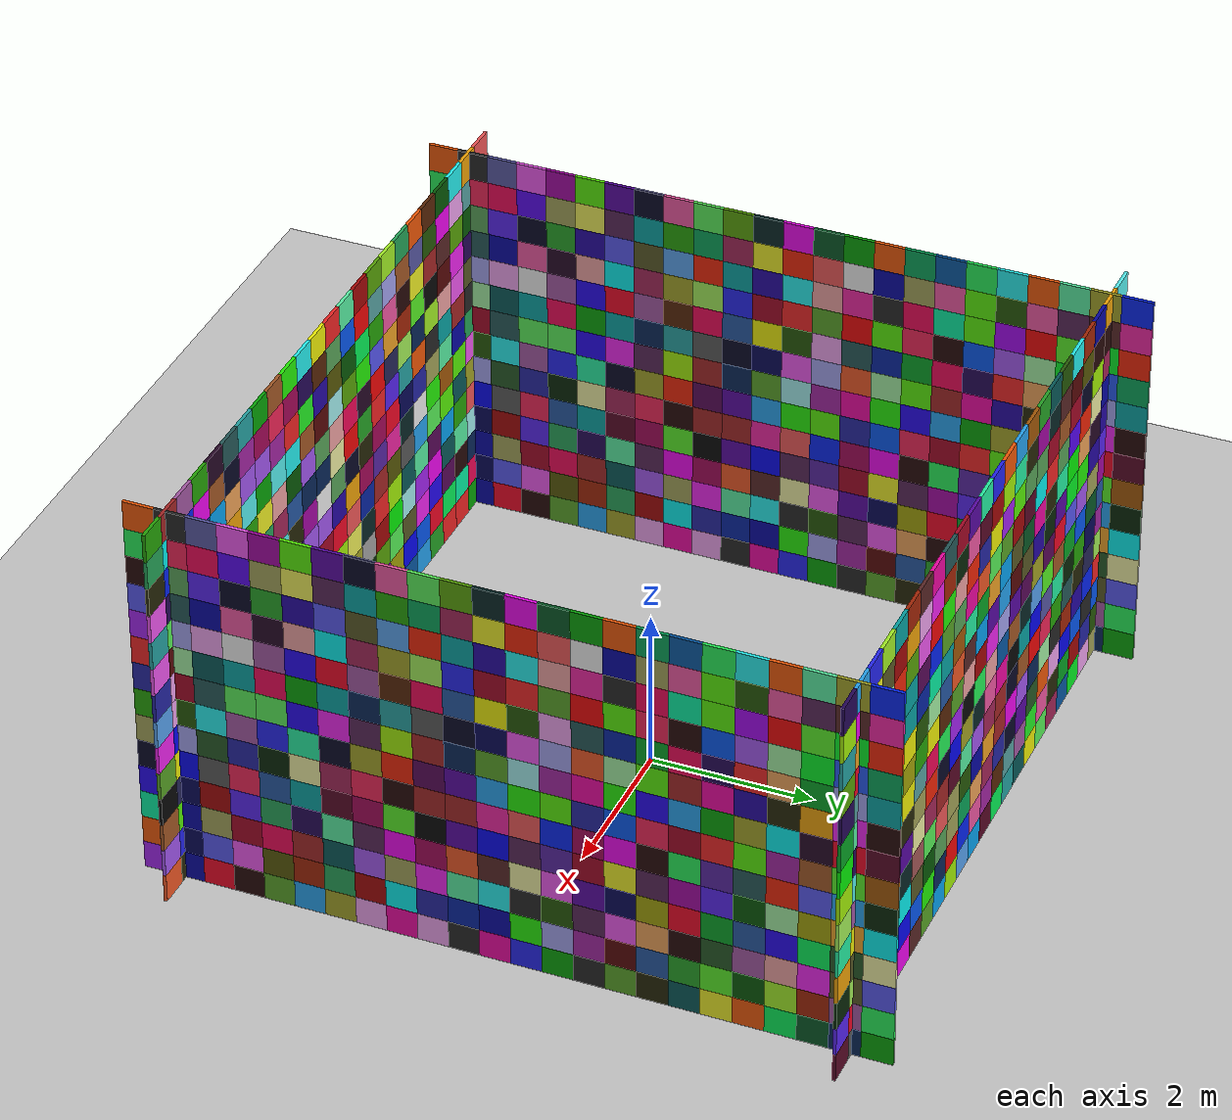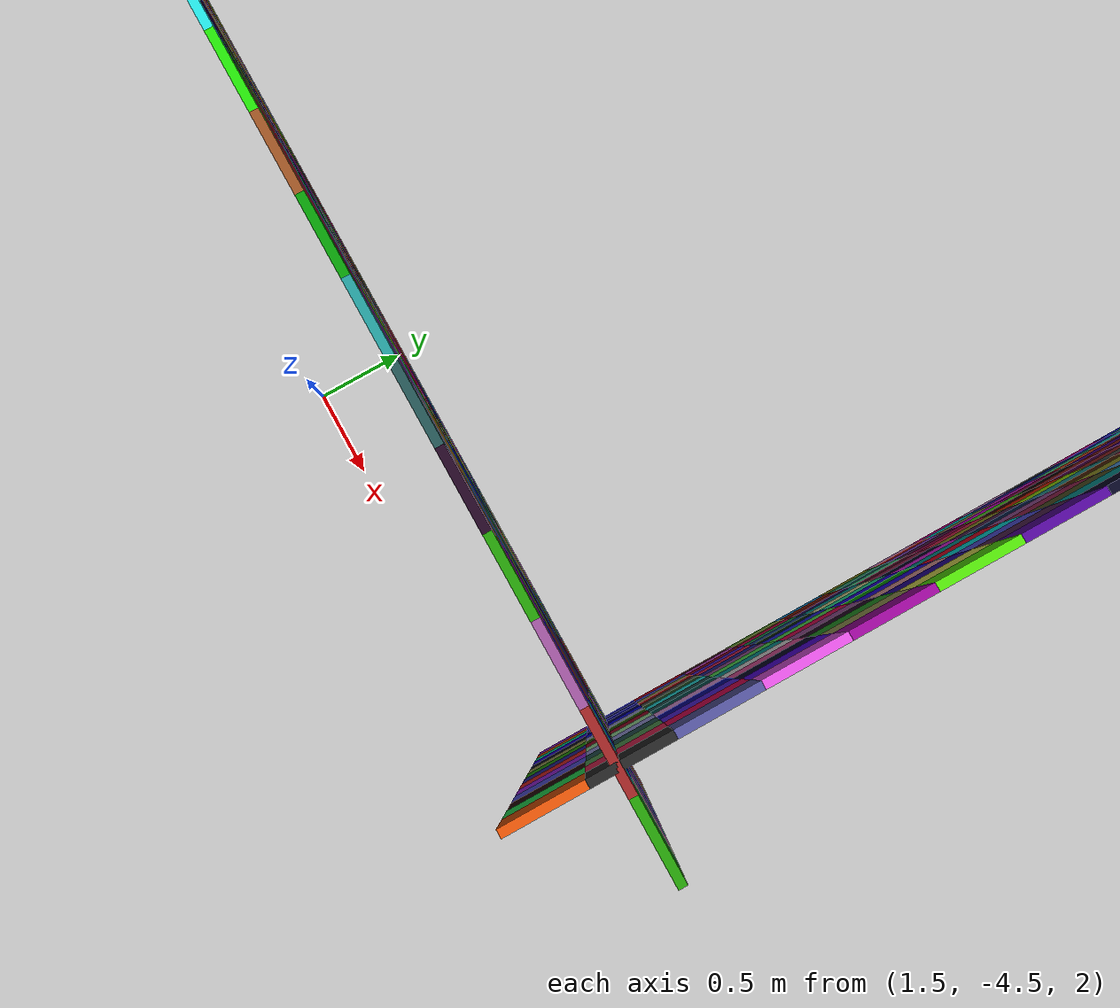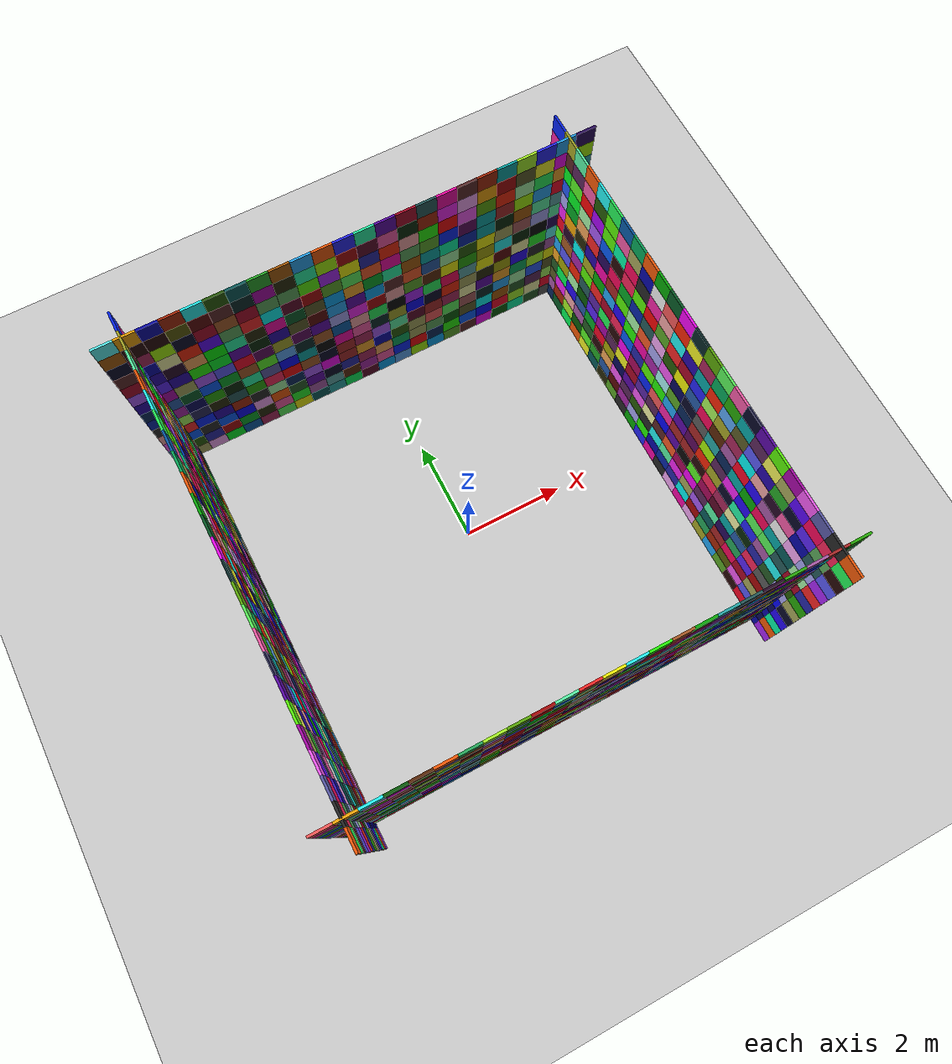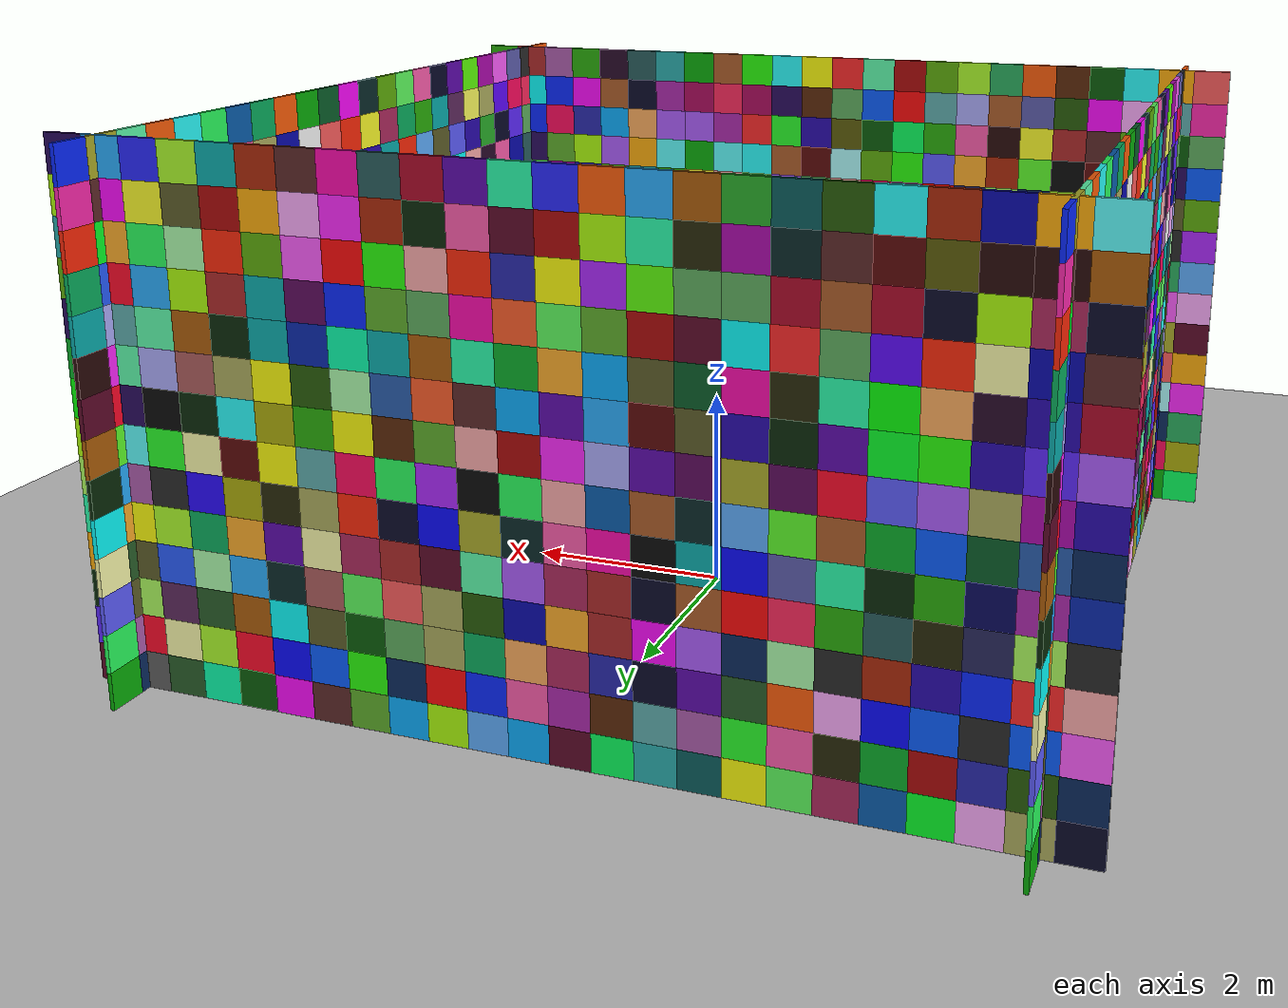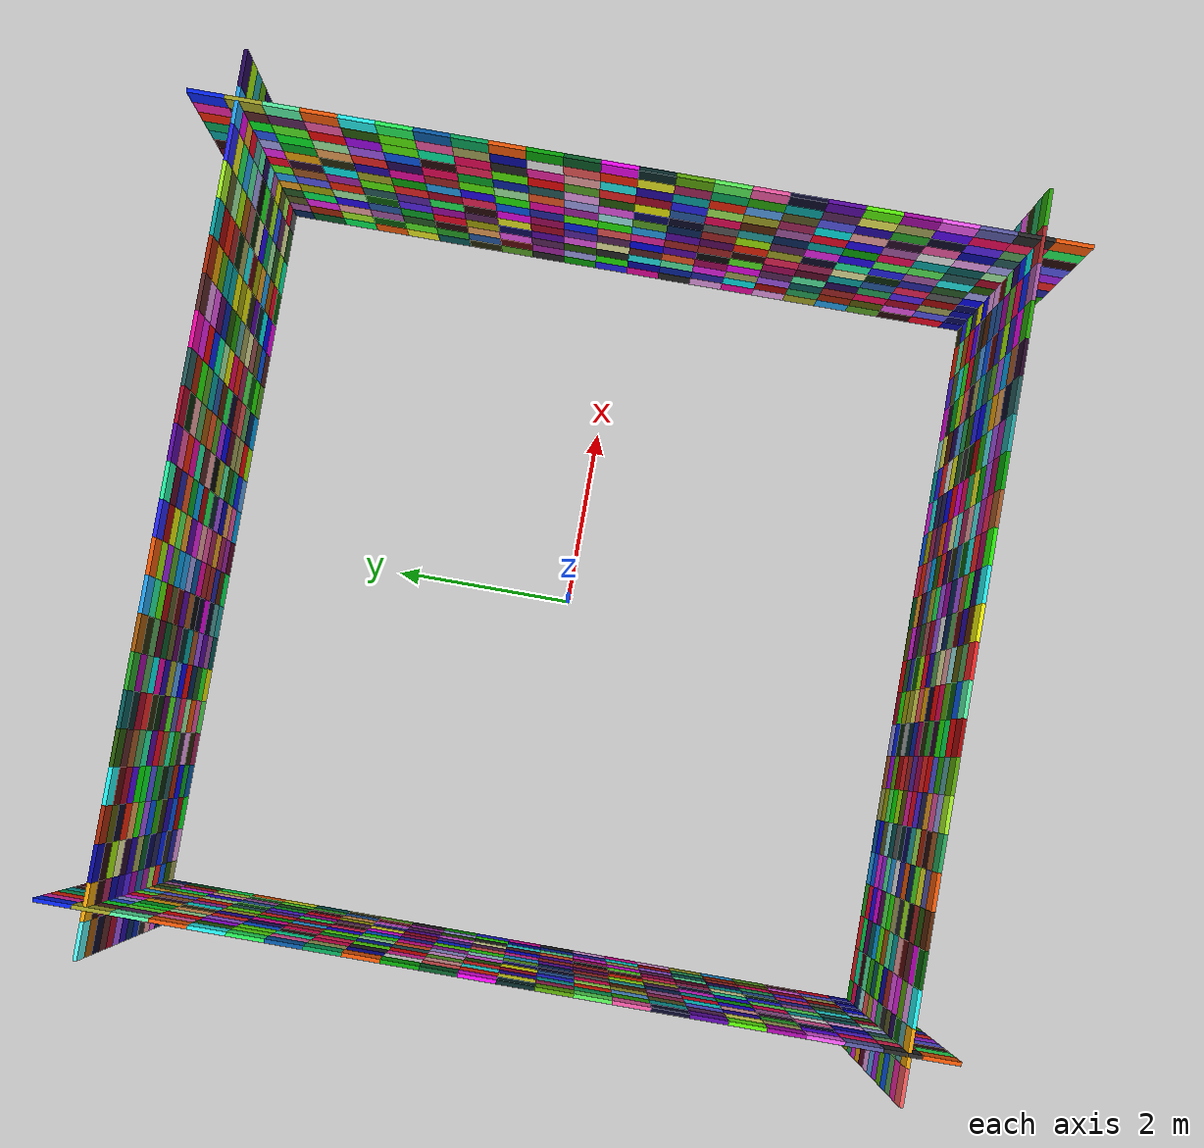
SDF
<?xml version='1.0' encoding='utf-8'?>
<sdf version="1.9">
  <world name="default">
    <physics type="ode">
      <max_step_size>0.004</max_step_size>
      <real_time_factor>1.0</real_time_factor>
      <real_time_update_rate>250</real_time_update_rate>
    </physics>
    <gravity>0 0 -9.8</gravity>
    <magnetic_field>6e-06 2.3e-05 -4.2e-05</magnetic_field>
    <atmosphere type="adiabatic" />
    <scene>
      <grid>false</grid>
      <ambient>0.4 0.4 0.4 1</ambient>
      <background>0.7 0.7 0.7 1</background>
      <shadows>true</shadows>
    </scene>
    <model name="ground_plane">
      <static>true</static>
      <link name="link">
        <collision name="collision">
          <geometry>
            <plane>
              <normal>0 0 1</normal>
              <size>1 1</size>
            </plane>
          </geometry>
          <surface>
            <friction>
              <ode />
            </friction>
            <bounce />
            <contact />
          </surface>
        </collision>
        <visual name="visual">
          <geometry>
            <plane>
              <normal>0 0 1</normal>
              <size>500 500</size>
            </plane>
          </geometry>
          <material>
            <ambient>0.8 0.8 0.8 1</ambient>
            <diffuse>0.8 0.8 0.8 1</diffuse>
            <specular>0.8 0.8 0.8 1</specular>
          </material>
        </visual>
        <pose>0 0 0 0 -0 0</pose>
        <inertial>
          <pose>0 0 0 0 -0 0</pose>
          <mass>1</mass>
          <inertia>
            <ixx>1</ixx>
            <ixy>0</ixy>
            <ixz>0</ixz>
            <iyy>1</iyy>
            <iyz>0</iyz>
            <izz>1</izz>
          </inertia>
        </inertial>
        <enable_wind>false</enable_wind>
      </link>
      <pose>0 0 0 0 -0 0</pose>
      <self_collide>false</self_collide>
    </model>
    <light name="sunUTC" type="directional">
      <pose>0 0 500 0 -0 0</pose>
      <cast_shadows>true</cast_shadows>
      <intensity>1</intensity>
      <direction>0.001 0.625 -0.78</direction>
      <diffuse>0.904 0.904 0.904 1</diffuse>
      <specular>0.271 0.271 0.271 1</specular>
      <attenuation>
        <range>2000</range>
        <linear>0</linear>
        <constant>1</constant>
        <quadratic>0</quadratic>
      </attenuation>
      <spot>
        <inner_angle>0</inner_angle>
        <outer_angle>0</outer_angle>
        <falloff>0</falloff>
      </spot>
    </light>
    <spherical_coordinates>
      <surface_model>EARTH_WGS84</surface_model>
      <world_frame_orientation>ENU</world_frame_orientation>
      <latitude_deg>47.397971057728974</latitude_deg>
      <longitude_deg> 8.546163739800146</longitude_deg>
      <elevation>0</elevation>
    </spherical_coordinates>
  <model name="vio_wall_0"><static>true</static><pose>4 0 2.5 0 0 0</pose><link name="wall"><collision name="surface"><geometry><box><size>0.04 9 5</size></box></geometry></collision><visual name="tile_0_0"><pose>0 -4.3125 -2.3205 0 0 0</pose><geometry><box><size>0.04 0.375 0.357</size></box></geometry><material><ambient>0.65 0.15 0.95 1</ambient><diffuse>0.65 0.15 0.95 1</diffuse></material></visual><visual name="tile_0_1"><pose>0 -3.9375 -2.3205 0 0 0</pose><geometry><box><size>0.04 0.375 0.357</size></box></geometry><material><ambient>0.03 0.03 0.65 1</ambient><diffuse>0.03 0.03 0.65 1</diffuse></material></visual><visual name="tile_0_2"><pose>0 -3.5625 -2.3205 0 0 0</pose><geometry><box><size>0.04 0.375 0.357</size></box></geometry><material><ambient>0.95 0.03 0.15 1</ambient><diffuse>0.95 0.03 0.15 1</diffuse></material></visual><visual name="tile_0_3"><pose>0 -3.1875 -2.3205 0 0 0</pose><geometry><box><size>0.04 0.375 0.357</size></box></geometry><material><ambient>0.15 0.03 0.03 1</ambient><diffuse>0.15 0.03 0.03 1</diffuse></material></visual><visual name="tile_0_4"><pose>0 -2.8125 -2.3205 0 0 0</pose><geometry><box><size>0.04 0.375 0.357</size></box></geometry><material><ambient>0.35 0.65 0.15 1</ambient><diffuse>0.35 0.65 0.15 1</diffuse></material></visual><visual name="tile_0_5"><pose>0 -2.4375 -2.3205 0 0 0</pose><geometry><box><size>0.04 0.375 0.357</size></box></geometry><material><ambient>0.15 0.65 0.95 1</ambient><diffuse>0.15 0.65 0.95 1</diffuse></material></visual><visual name="tile_0_6"><pose>0 -2.0625 -2.3205 0 0 0</pose><geometry><box><size>0.04 0.375 0.357</size></box></geometry><material><ambient>0.65 0.65 0.15 1</ambient><diffuse>0.65 0.65 0.15 1</diffuse></material></visual><visual name="tile_0_7"><pose>0 -1.6875 -2.3205 0 0 0</pose><geometry><box><size>0.04 0.375 0.357</size></box></geometry><material><ambient>0.95 0.65 0.95 1</ambient><diffuse>0.95 0.65 0.95 1</diffuse></material></visual><visual name="tile_0_8"><pose>0 -1.3125 -2.3205 0 0 0</pose><geometry><box><size>0.04 0.375 0.357</size></box></geometry><material><ambient>0.95 0.03 0.65 1</ambient><diffuse>0.95 0.03 0.65 1</diffuse></material></visual><visual name="tile_0_9"><pose>0 -0.9375 -2.3205 0 0 0</pose><geometry><box><size>0.04 0.375 0.357</size></box></geometry><material><ambient>0.95 0.65 0.95 1</ambient><diffuse>0.95 0.65 0.95 1</diffuse></material></visual><visual name="tile_0_10"><pose>0 -0.5625 -2.3205 0 0 0</pose><geometry><box><size>0.04 0.375 0.357</size></box></geometry><material><ambient>0.15 0.15 0.15 1</ambient><diffuse>0.15 0.15 0.15 1</diffuse></material></visual><visual name="tile_0_11"><pose>0 -0.1875 -2.3205 0 0 0</pose><geometry><box><size>0.04 0.375 0.357</size></box></geometry><material><ambient>0.95 0.03 0.65 1</ambient><diffuse>0.95 0.03 0.65 1</diffuse></material></visual><visual name="tile_0_12"><pose>0 0.1875 -2.3205 0 0 0</pose><geometry><box><size>0.04 0.375 0.357</size></box></geometry><material><ambient>0.15 0.15 0.95 1</ambient><diffuse>0.15 0.15 0.95 1</diffuse></material></visual><visual name="tile_0_13"><pose>0 0.5625 -2.3205 0 0 0</pose><geometry><box><size>0.04 0.375 0.357</size></box></geometry><material><ambient>0.03 0.65 0.03 1</ambient><diffuse>0.03 0.65 0.03 1</diffuse></material></visual><visual name="tile_0_14"><pose>0 0.9375 -2.3205 0 0 0</pose><geometry><box><size>0.04 0.375 0.357</size></box></geometry><material><ambient>0.15 0.15 0.15 1</ambient><diffuse>0.15 0.15 0.15 1</diffuse></material></visual><visual name="tile_0_15"><pose>0 1.3125 -2.3205 0 0 0</pose><geometry><box><size>0.04 0.375 0.357</size></box></geometry><material><ambient>0.35 0.65 0.15 1</ambient><diffuse>0.35 0.65 0.15 1</diffuse></material></visual><visual name="tile_0_16"><pose>0 1.6875 -2.3205 0 0 0</pose><geometry><box><size>0.04 0.375 0.357</size></box></geometry><material><ambient>0.15 0.15 0.03 1</ambient><diffuse>0.15 0.15 0.03 1</diffuse></material></visual><visual name="tile_0_17"><pose>0 2.0625 -2.3205 0 0 0</pose><geometry><box><size>0.04 0.375 0.357</size></box></geometry><material><ambient>0.03 0.35 0.35 1</ambient><diffuse>0.03 0.35 0.35 1</diffuse></material></visual><visual name="tile_0_18"><pose>0 2.4375 -2.3205 0 0 0</pose><geometry><box><size>0.04 0.375 0.357</size></box></geometry><material><ambient>0.95 0.95 0.15 1</ambient><diffuse>0.95 0.95 0.15 1</diffuse></material></visual><visual name="tile_0_19"><pose>0 2.8125 -2.3205 0 0 0</pose><geometry><box><size>0.04 0.375 0.357</size></box></geometry><material><ambient>0.95 0.35 0.03 1</ambient><diffuse>0.95 0.35 0.03 1</diffuse></material></visual><visual name="tile_0_20"><pose>0 3.1875 -2.3205 0 0 0</pose><geometry><box><size>0.04 0.375 0.357</size></box></geometry><material><ambient>0.03 0.95 0.35 1</ambient><diffuse>0.03 0.95 0.35 1</diffuse></material></visual><visual name="tile_0_21"><pose>0 3.5625 -2.3205 0 0 0</pose><geometry><box><size>0.04 0.375 0.357</size></box></geometry><material><ambient>0.03 0.35 0.15 1</ambient><diffuse>0.03 0.35 0.15 1</diffuse></material></visual><visual name="tile_0_22"><pose>0 3.9375 -2.3205 0 0 0</pose><geometry><box><size>0.04 0.375 0.357</size></box></geometry><material><ambient>0.03 0.15 0.35 1</ambient><diffuse>0.03 0.15 0.35 1</diffuse></material></visual><visual name="tile_0_23"><pose>0 4.3125 -2.3205 0 0 0</pose><geometry><box><size>0.04 0.375 0.357</size></box></geometry><material><ambient>0.03 0.65 0.03 1</ambient><diffuse>0.03 0.65 0.03 1</diffuse></material></visual><visual name="tile_1_0"><pose>0 -4.3125 -1.9634999999999998 0 0 0</pose><geometry><box><size>0.04 0.375 0.357</size></box></geometry><material><ambient>0.95 0.35 0.03 1</ambient><diffuse>0.95 0.35 0.03 1</diffuse></material></visual><visual name="tile_1_1"><pose>0 -3.9375 -1.9634999999999998 0 0 0</pose><geometry><box><size>0.04 0.375 0.357</size></box></geometry><material><ambient>0.03 0.03 0.35 1</ambient><diffuse>0.03 0.03 0.35 1</diffuse></material></visual><visual name="tile_1_2"><pose>0 -3.5625 -1.9634999999999998 0 0 0</pose><geometry><box><size>0.04 0.375 0.357</size></box></geometry><material><ambient>0.35 0.35 0.95 1</ambient><diffuse>0.35 0.35 0.95 1</diffuse></material></visual><visual name="tile_1_3"><pose>0 -3.1875 -1.9634999999999998 0 0 0</pose><geometry><box><size>0.04 0.375 0.357</size></box></geometry><material><ambient>0.95 0.35 0.95 1</ambient><diffuse>0.95 0.35 0.95 1</diffuse></material></visual><visual name="tile_1_4"><pose>0 -2.8125 -1.9634999999999998 0 0 0</pose><geometry><box><size>0.04 0.375 0.357</size></box></geometry><material><ambient>0.35 0.35 0.03 1</ambient><diffuse>0.35 0.35 0.03 1</diffuse></material></visual><visual name="tile_1_5"><pose>0 -2.4375 -1.9634999999999998 0 0 0</pose><geometry><box><size>0.04 0.375 0.357</size></box></geometry><material><ambient>0.65 0.15 0.03 1</ambient><diffuse>0.65 0.15 0.03 1</diffuse></material></visual><visual name="tile_1_6"><pose>0 -2.0625 -1.9634999999999998 0 0 0</pose><geometry><box><size>0.04 0.375 0.357</size></box></geometry><material><ambient>0.15 0.65 0.35 1</ambient><diffuse>0.15 0.65 0.35 1</diffuse></material></visual><visual name="tile_1_7"><pose>0 -1.6875 -1.9634999999999998 0 0 0</pose><geometry><box><size>0.04 0.375 0.357</size></box></geometry><material><ambient>0.65 0.03 0.03 1</ambient><diffuse>0.65 0.03 0.03 1</diffuse></material></visual><visual name="tile_1_8"><pose>0 -1.3125 -1.9634999999999998 0 0 0</pose><geometry><box><size>0.04 0.375 0.357</size></box></geometry><material><ambient>0.03 0.95 0.95 1</ambient><diffuse>0.03 0.95 0.95 1</diffuse></material></visual><visual name="tile_1_9"><pose>0 -0.9375 -1.9634999999999998 0 0 0</pose><geometry><box><size>0.04 0.375 0.357</size></box></geometry><material><ambient>0.15 0.15 0.65 1</ambient><diffuse>0.15 0.15 0.65 1</diffuse></material></visual><visual name="tile_1_10"><pose>0 -0.5625 -1.9634999999999998 0 0 0</pose><geometry><box><size>0.04 0.375 0.357</size></box></geometry><material><ambient>0.03 0.15 0.65 1</ambient><diffuse>0.03 0.15 0.65 1</diffuse></material></visual><visual name="tile_1_11"><pose>0 -0.1875 -1.9634999999999998 0 0 0</pose><geometry><box><size>0.04 0.375 0.357</size></box></geometry><material><ambient>0.03 0.03 0.65 1</ambient><diffuse>0.03 0.03 0.65 1</diffuse></material></visual><visual name="tile_1_12"><pose>0 0.1875 -1.9634999999999998 0 0 0</pose><geometry><box><size>0.04 0.375 0.357</size></box></geometry><material><ambient>0.15 0.95 0.03 1</ambient><diffuse>0.15 0.95 0.03 1</diffuse></material></visual><visual name="tile_1_13"><pose>0 0.5625 -1.9634999999999998 0 0 0</pose><geometry><box><size>0.04 0.375 0.357</size></box></geometry><material><ambient>0.65 0.65 0.95 1</ambient><diffuse>0.65 0.65 0.95 1</diffuse></material></visual><visual name="tile_1_14"><pose>0 0.9375 -1.9634999999999998 0 0 0</pose><geometry><box><size>0.04 0.375 0.357</size></box></geometry><material><ambient>0.65 0.15 0.65 1</ambient><diffuse>0.65 0.15 0.65 1</diffuse></material></visual><visual name="tile_1_15"><pose>0 1.3125 -1.9634999999999998 0 0 0</pose><geometry><box><size>0.04 0.375 0.357</size></box></geometry><material><ambient>0.35 0.03 0.03 1</ambient><diffuse>0.35 0.03 0.03 1</diffuse></material></visual><visual name="tile_1_16"><pose>0 1.6875 -1.9634999999999998 0 0 0</pose><geometry><box><size>0.04 0.375 0.357</size></box></geometry><material><ambient>0.15 0.35 0.65 1</ambient><diffuse>0.15 0.35 0.65 1</diffuse></material></visual><visual name="tile_1_17"><pose>0 2.0625 -1.9634999999999998 0 0 0</pose><geometry><box><size>0.04 0.375 0.357</size></box></geometry><material><ambient>0.15 0.65 0.15 1</ambient><diffuse>0.15 0.65 0.15 1</diffuse></material></visual><visual name="tile_1_18"><pose>0 2.4375 -1.9634999999999998 0 0 0</pose><geometry><box><size>0.04 0.375 0.357</size></box></geometry><material><ambient>0.35 0.95 0.15 1</ambient><diffuse>0.35 0.95 0.15 1</diffuse></material></visual><visual name="tile_1_19"><pose>0 2.8125 -1.9634999999999998 0 0 0</pose><geometry><box><size>0.04 0.375 0.357</size></box></geometry><material><ambient>0.03 0.35 0.03 1</ambient><diffuse>0.03 0.35 0.03 1</diffuse></material></visual><visual name="tile_1_20"><pose>0 3.1875 -1.9634999999999998 0 0 0</pose><geometry><box><size>0.04 0.375 0.357</size></box></geometry><material><ambient>0.65 0.95 0.15 1</ambient><diffuse>0.65 0.95 0.15 1</diffuse></material></visual><visual name="tile_1_21"><pose>0 3.5625 -1.9634999999999998 0 0 0</pose><geometry><box><size>0.04 0.375 0.357</size></box></geometry><material><ambient>0.65 0.15 0.03 1</ambient><diffuse>0.65 0.15 0.03 1</diffuse></material></visual><visual name="tile_1_22"><pose>0 3.9375 -1.9634999999999998 0 0 0</pose><geometry><box><size>0.04 0.375 0.357</size></box></geometry><material><ambient>0.65 0.35 0.65 1</ambient><diffuse>0.65 0.35 0.65 1</diffuse></material></visual><visual name="tile_1_23"><pose>0 4.3125 -1.9634999999999998 0 0 0</pose><geometry><box><size>0.04 0.375 0.357</size></box></geometry><material><ambient>0.15 0.95 0.35 1</ambient><diffuse>0.15 0.95 0.35 1</diffuse></material></visual><visual name="tile_2_0"><pose>0 -4.3125 -1.6065 0 0 0</pose><geometry><box><size>0.04 0.375 0.357</size></box></geometry><material><ambient>0.03 0.95 0.65 1</ambient><diffuse>0.03 0.95 0.65 1</diffuse></material></visual><visual name="tile_2_1"><pose>0 -3.9375 -1.6065 0 0 0</pose><geometry><box><size>0.04 0.375 0.357</size></box></geometry><material><ambient>0.03 0.03 0.65 1</ambient><diffuse>0.03 0.03 0.65 1</diffuse></material></visual><visual name="tile_2_2"><pose>0 -3.5625 -1.6065 0 0 0</pose><geometry><box><size>0.04 0.375 0.357</size></box></geometry><material><ambient>0.65 0.65 0.35 1</ambient><diffuse>0.65 0.65 0.35 1</diffuse></material></visual><visual name="tile_2_3"><pose>0 -3.1875 -1.6065 0 0 0</pose><geometry><box><size>0.04 0.375 0.357</size></box></geometry><material><ambient>0.65 0.03 0.15 1</ambient><diffuse>0.65 0.03 0.15 1</diffuse></material></visual><visual name="tile_2_4"><pose>0 -2.8125 -1.6065 0 0 0</pose><geometry><box><size>0.04 0.375 0.357</size></box></geometry><material><ambient>0.95 0.03 0.35 1</ambient><diffuse>0.95 0.03 0.35 1</diffuse></material></visual><visual name="tile_2_5"><pose>0 -2.4375 -1.6065 0 0 0</pose><geometry><box><size>0.04 0.375 0.357</size></box></geometry><material><ambient>0.65 0.15 0.15 1</ambient><diffuse>0.65 0.15 0.15 1</diffuse></material></visual><visual name="tile_2_6"><pose>0 -2.0625 -1.6065 0 0 0</pose><geometry><box><size>0.04 0.375 0.357</size></box></geometry><material><ambient>0.03 0.35 0.35 1</ambient><diffuse>0.03 0.35 0.35 1</diffuse></material></visual><visual name="tile_2_7"><pose>0 -1.6875 -1.6065 0 0 0</pose><geometry><box><size>0.04 0.375 0.357</size></box></geometry><material><ambient>0.65 0.35 0.95 1</ambient><diffuse>0.65 0.35 0.95 1</diffuse></material></visual><visual name="tile_2_8"><pose>0 -1.3125 -1.6065 0 0 0</pose><geometry><box><size>0.04 0.375 0.357</size></box></geometry><material><ambient>0.65 0.65 0.35 1</ambient><diffuse>0.65 0.65 0.35 1</diffuse></material></visual><visual name="tile_2_9"><pose>0 -0.9375 -1.6065 0 0 0</pose><geometry><box><size>0.04 0.375 0.357</size></box></geometry><material><ambient>0.95 0.15 0.95 1</ambient><diffuse>0.95 0.15 0.95 1</diffuse></material></visual><visual name="tile_2_10"><pose>0 -0.5625 -1.6065 0 0 0</pose><geometry><box><size>0.04 0.375 0.357</size></box></geometry><material><ambient>0.35 0.95 0.65 1</ambient><diffuse>0.35 0.95 0.65 1</diffuse></material></visual><visual name="tile_2_11"><pose>0 -0.1875 -1.6065 0 0 0</pose><geometry><box><size>0.04 0.375 0.357</size></box></geometry><material><ambient>0.15 0.95 0.95 1</ambient><diffuse>0.15 0.95 0.95 1</diffuse></material></visual><visual name="tile_2_12"><pose>0 0.1875 -1.6065 0 0 0</pose><geometry><box><size>0.04 0.375 0.357</size></box></geometry><material><ambient>0.15 0.15 0.15 1</ambient><diffuse>0.15 0.15 0.15 1</diffuse></material></visual><visual name="tile_2_13"><pose>0 0.5625 -1.6065 0 0 0</pose><geometry><box><size>0.04 0.375 0.357</size></box></geometry><material><ambient>0.15 0.35 0.03 1</ambient><diffuse>0.15 0.35 0.03 1</diffuse></material></visual><visual name="tile_2_14"><pose>0 0.9375 -1.6065 0 0 0</pose><geometry><box><size>0.04 0.375 0.357</size></box></geometry><material><ambient>0.35 0.15 0.35 1</ambient><diffuse>0.35 0.15 0.35 1</diffuse></material></visual><visual name="tile_2_15"><pose>0 1.3125 -1.6065 0 0 0</pose><geometry><box><size>0.04 0.375 0.357</size></box></geometry><material><ambient>0.95 0.35 0.95 1</ambient><diffuse>0.95 0.35 0.95 1</diffuse></material></visual><visual name="tile_2_16"><pose>0 1.6875 -1.6065 0 0 0</pose><geometry><box><size>0.04 0.375 0.357</size></box></geometry><material><ambient>0.95 0.65 0.35 1</ambient><diffuse>0.95 0.65 0.35 1</diffuse></material></visual><visual name="tile_2_17"><pose>0 2.0625 -1.6065 0 0 0</pose><geometry><box><size>0.04 0.375 0.357</size></box></geometry><material><ambient>0.15 0.03 0.03 1</ambient><diffuse>0.15 0.03 0.03 1</diffuse></material></visual><visual name="tile_2_18"><pose>0 2.4375 -1.6065 0 0 0</pose><geometry><box><size>0.04 0.375 0.357</size></box></geometry><material><ambient>0.15 0.35 0.15 1</ambient><diffuse>0.15 0.35 0.15 1</diffuse></material></visual><visual name="tile_2_19"><pose>0 2.8125 -1.6065 0 0 0</pose><geometry><box><size>0.04 0.375 0.357</size></box></geometry><material><ambient>0.65 0.35 0.65 1</ambient><diffuse>0.65 0.35 0.65 1</diffuse></material></visual><visual name="tile_2_20"><pose>0 3.1875 -1.6065 0 0 0</pose><geometry><box><size>0.04 0.375 0.357</size></box></geometry><material><ambient>0.95 0.65 0.65 1</ambient><diffuse>0.95 0.65 0.65 1</diffuse></material></visual><visual name="tile_2_21"><pose>0 3.5625 -1.6065 0 0 0</pose><geometry><box><size>0.04 0.375 0.357</size></box></geometry><material><ambient>0.95 0.15 0.95 1</ambient><diffuse>0.95 0.15 0.95 1</diffuse></material></visual><visual name="tile_2_22"><pose>0 3.9375 -1.6065 0 0 0</pose><geometry><box><size>0.04 0.375 0.357</size></box></geometry><material><ambient>0.35 0.35 0.15 1</ambient><diffuse>0.35 0.35 0.15 1</diffuse></material></visual><visual name="tile_2_23"><pose>0 4.3125 -1.6065 0 0 0</pose><geometry><box><size>0.04 0.375 0.357</size></box></geometry><material><ambient>0.35 0.35 0.95 1</ambient><diffuse>0.35 0.35 0.95 1</diffuse></material></visual><visual name="tile_3_0"><pose>0 -4.3125 -1.2494999999999998 0 0 0</pose><geometry><box><size>0.04 0.375 0.357</size></box></geometry><material><ambient>0.15 0.03 0.95 1</ambient><diffuse>0.15 0.03 0.95 1</diffuse></material></visual><visual name="tile_3_1"><pose>0 -3.9375 -1.2494999999999998 0 0 0</pose><geometry><box><size>0.04 0.375 0.357</size></box></geometry><material><ambient>0.03 0.03 0.35 1</ambient><diffuse>0.03 0.03 0.35 1</diffuse></material></visual><visual name="tile_3_2"><pose>0 -3.5625 -1.2494999999999998 0 0 0</pose><geometry><box><size>0.04 0.375 0.357</size></box></geometry><material><ambient>0.65 0.03 0.03 1</ambient><diffuse>0.65 0.03 0.03 1</diffuse></material></visual><visual name="tile_3_3"><pose>0 -3.1875 -1.2494999999999998 0 0 0</pose><geometry><box><size>0.04 0.375 0.357</size></box></geometry><material><ambient>0.35 0.15 0.95 1</ambient><diffuse>0.35 0.15 0.95 1</diffuse></material></visual><visual name="tile_3_4"><pose>0 -2.8125 -1.2494999999999998 0 0 0</pose><geometry><box><size>0.04 0.375 0.357</size></box></geometry><material><ambient>0.15 0.65 0.35 1</ambient><diffuse>0.15 0.65 0.35 1</diffuse></material></visual><visual name="tile_3_5"><pose>0 -2.4375 -1.2494999999999998 0 0 0</pose><geometry><box><size>0.04 0.375 0.357</size></box></geometry><material><ambient>0.15 0.03 0.35 1</ambient><diffuse>0.15 0.03 0.35 1</diffuse></material></visual><visual name="tile_3_6"><pose>0 -2.0625 -1.2494999999999998 0 0 0</pose><geometry><box><size>0.04 0.375 0.357</size></box></geometry><material><ambient>0.35 0.95 0.65 1</ambient><diffuse>0.35 0.95 0.65 1</diffuse></material></visual><visual name="tile_3_7"><pose>0 -1.6875 -1.2494999999999998 0 0 0</pose><geometry><box><size>0.04 0.375 0.357</size></box></geometry><material><ambient>0.35 0.15 0.35 1</ambient><diffuse>0.35 0.15 0.35 1</diffuse></material></visual><visual name="tile_3_8"><pose>0 -1.3125 -1.2494999999999998 0 0 0</pose><geometry><box><size>0.04 0.375 0.357</size></box></geometry><material><ambient>0.95 0.03 0.95 1</ambient><diffuse>0.95 0.03 0.95 1</diffuse></material></visual><visual name="tile_3_9"><pose>0 -0.9375 -1.2494999999999998 0 0 0</pose><geometry><box><size>0.04 0.375 0.357</size></box></geometry><material><ambient>0.65 0.03 0.35 1</ambient><diffuse>0.65 0.03 0.35 1</diffuse></material></visual><visual name="tile_3_10"><pose>0 -0.5625 -1.2494999999999998 0 0 0</pose><geometry><box><size>0.04 0.375 0.357</size></box></geometry><material><ambient>0.95 0.35 0.15 1</ambient><diffuse>0.95 0.35 0.15 1</diffuse></material></visual><visual name="tile_3_11"><pose>0 -0.1875 -1.2494999999999998 0 0 0</pose><geometry><box><size>0.04 0.375 0.357</size></box></geometry><material><ambient>0.35 0.15 0.15 1</ambient><diffuse>0.35 0.15 0.15 1</diffuse></material></visual><visual name="tile_3_12"><pose>0 0.1875 -1.2494999999999998 0 0 0</pose><geometry><box><size>0.04 0.375 0.357</size></box></geometry><material><ambient>0.95 0.95 0.65 1</ambient><diffuse>0.95 0.95 0.65 1</diffuse></material></visual><visual name="tile_3_13"><pose>0 0.5625 -1.2494999999999998 0 0 0</pose><geometry><box><size>0.04 0.375 0.357</size></box></geometry><material><ambient>0.95 0.35 0.95 1</ambient><diffuse>0.95 0.35 0.95 1</diffuse></material></visual><visual name="tile_3_14"><pose>0 0.9375 -1.2494999999999998 0 0 0</pose><geometry><box><size>0.04 0.375 0.357</size></box></geometry><material><ambient>0.35 0.03 0.65 1</ambient><diffuse>0.35 0.03 0.65 1</diffuse></material></visual><visual name="tile_3_15"><pose>0 1.3125 -1.2494999999999998 0 0 0</pose><geometry><box><size>0.04 0.375 0.357</size></box></geometry><material><ambient>0.03 0.03 0.35 1</ambient><diffuse>0.03 0.03 0.35 1</diffuse></material></visual><visual name="tile_3_16"><pose>0 1.6875 -1.2494999999999998 0 0 0</pose><geometry><box><size>0.04 0.375 0.357</size></box></geometry><material><ambient>0.65 0.65 0.03 1</ambient><diffuse>0.65 0.65 0.03 1</diffuse></material></visual><visual name="tile_3_17"><pose>0 2.0625 -1.2494999999999998 0 0 0</pose><geometry><box><size>0.04 0.375 0.357</size></box></geometry><material><ambient>0.95 0.03 0.15 1</ambient><diffuse>0.95 0.03 0.15 1</diffuse></material></visual><visual name="tile_3_18"><pose>0 2.4375 -1.2494999999999998 0 0 0</pose><geometry><box><size>0.04 0.375 0.357</size></box></geometry><material><ambient>0.03 0.65 0.15 1</ambient><diffuse>0.03 0.65 0.15 1</diffuse></material></visual><visual name="tile_3_19"><pose>0 2.8125 -1.2494999999999998 0 0 0</pose><geometry><box><size>0.04 0.375 0.357</size></box></geometry><material><ambient>0.15 0.35 0.65 1</ambient><diffuse>0.15 0.35 0.65 1</diffuse></material></visual><visual name="tile_3_20"><pose>0 3.1875 -1.2494999999999998 0 0 0</pose><geometry><box><size>0.04 0.375 0.357</size></box></geometry><material><ambient>0.15 0.03 0.95 1</ambient><diffuse>0.15 0.03 0.95 1</diffuse></material></visual><visual name="tile_3_21"><pose>0 3.5625 -1.2494999999999998 0 0 0</pose><geometry><box><size>0.04 0.375 0.357</size></box></geometry><material><ambient>0.03 0.95 0.35 1</ambient><diffuse>0.03 0.95 0.35 1</diffuse></material></visual><visual name="tile_3_22"><pose>0 3.9375 -1.2494999999999998 0 0 0</pose><geometry><box><size>0.04 0.375 0.357</size></box></geometry><material><ambient>0.15 0.35 0.15 1</ambient><diffuse>0.15 0.35 0.15 1</diffuse></material></visual><visual name="tile_3_23"><pose>0 4.3125 -1.2494999999999998 0 0 0</pose><geometry><box><size>0.04 0.375 0.357</size></box></geometry><material><ambient>0.95 0.95 0.65 1</ambient><diffuse>0.95 0.95 0.65 1</diffuse></material></visual><visual name="tile_4_0"><pose>0 -4.3125 -0.8925 0 0 0</pose><geometry><box><size>0.04 0.375 0.357</size></box></geometry><material><ambient>0.03 0.03 0.15 1</ambient><diffuse>0.03 0.03 0.15 1</diffuse></material></visual><visual name="tile_4_1"><pose>0 -3.9375 -0.8925 0 0 0</pose><geometry><box><size>0.04 0.375 0.357</size></box></geometry><material><ambient>0.03 0.03 0.95 1</ambient><diffuse>0.03 0.03 0.95 1</diffuse></material></visual><visual name="tile_4_2"><pose>0 -3.5625 -0.8925 0 0 0</pose><geometry><box><size>0.04 0.375 0.357</size></box></geometry><material><ambient>0.35 0.35 0.35 1</ambient><diffuse>0.35 0.35 0.35 1</diffuse></material></visual><visual name="tile_4_3"><pose>0 -3.1875 -0.8925 0 0 0</pose><geometry><box><size>0.04 0.375 0.357</size></box></geometry><material><ambient>0.95 0.15 0.35 1</ambient><diffuse>0.95 0.15 0.35 1</diffuse></material></visual><visual name="tile_4_4"><pose>0 -2.8125 -0.8925 0 0 0</pose><geometry><box><size>0.04 0.375 0.357</size></box></geometry><material><ambient>0.15 0.35 0.65 1</ambient><diffuse>0.15 0.35 0.65 1</diffuse></material></visual><visual name="tile_4_5"><pose>0 -2.4375 -0.8925 0 0 0</pose><geometry><box><size>0.04 0.375 0.357</size></box></geometry><material><ambient>0.03 0.65 0.65 1</ambient><diffuse>0.03 0.65 0.65 1</diffuse></material></visual><visual name="tile_4_6"><pose>0 -2.0625 -0.8925 0 0 0</pose><geometry><box><size>0.04 0.375 0.357</size></box></geometry><material><ambient>0.35 0.03 0.15 1</ambient><diffuse>0.35 0.03 0.15 1</diffuse></material></visual><visual name="tile_4_7"><pose>0 -1.6875 -0.8925 0 0 0</pose><geometry><box><size>0.04 0.375 0.357</size></box></geometry><material><ambient>0.65 0.03 0.35 1</ambient><diffuse>0.65 0.03 0.35 1</diffuse></material></visual><visual name="tile_4_8"><pose>0 -1.3125 -0.8925 0 0 0</pose><geometry><box><size>0.04 0.375 0.357</size></box></geometry><material><ambient>0.35 0.95 0.15 1</ambient><diffuse>0.35 0.95 0.15 1</diffuse></material></visual><visual name="tile_4_9"><pose>0 -0.9375 -0.8925 0 0 0</pose><geometry><box><size>0.04 0.375 0.357</size></box></geometry><material><ambient>0.03 0.03 0.03 1</ambient><diffuse>0.03 0.03 0.03 1</diffuse></material></visual><visual name="tile_4_10"><pose>0 -0.5625 -0.8925 0 0 0</pose><geometry><box><size>0.04 0.375 0.357</size></box></geometry><material><ambient>0.35 0.03 0.65 1</ambient><diffuse>0.35 0.03 0.65 1</diffuse></material></visual><visual name="tile_4_11"><pose>0 -0.1875 -0.8925 0 0 0</pose><geometry><box><size>0.04 0.375 0.357</size></box></geometry><material><ambient>0.03 0.03 0.95 1</ambient><diffuse>0.03 0.03 0.95 1</diffuse></material></visual><visual name="tile_4_12"><pose>0 0.1875 -0.8925 0 0 0</pose><geometry><box><size>0.04 0.375 0.357</size></box></geometry><material><ambient>0.35 0.15 0.35 1</ambient><diffuse>0.35 0.15 0.35 1</diffuse></material></visual><visual name="tile_4_13"><pose>0 0.5625 -0.8925 0 0 0</pose><geometry><box><size>0.04 0.375 0.357</size></box></geometry><material><ambient>0.35 0.15 0.65 1</ambient><diffuse>0.35 0.15 0.65 1</diffuse></material></visual><visual name="tile_4_14"><pose>0 0.9375 -0.8925 0 0 0</pose><geometry><box><size>0.04 0.375 0.357</size></box></geometry><material><ambient>0.65 0.03 0.15 1</ambient><diffuse>0.65 0.03 0.15 1</diffuse></material></visual><visual name="tile_4_15"><pose>0 1.3125 -0.8925 0 0 0</pose><geometry><box><size>0.04 0.375 0.357</size></box></geometry><material><ambient>0.95 0.95 0.15 1</ambient><diffuse>0.95 0.95 0.15 1</diffuse></material></visual><visual name="tile_4_16"><pose>0 1.6875 -0.8925 0 0 0</pose><geometry><box><size>0.04 0.375 0.357</size></box></geometry><material><ambient>0.35 0.15 0.35 1</ambient><diffuse>0.35 0.15 0.35 1</diffuse></material></visual><visual name="tile_4_17"><pose>0 2.0625 -0.8925 0 0 0</pose><geometry><box><size>0.04 0.375 0.357</size></box></geometry><material><ambient>0.65 0.03 0.65 1</ambient><diffuse>0.65 0.03 0.65 1</diffuse></material></visual><visual name="tile_4_18"><pose>0 2.4375 -0.8925 0 0 0</pose><geometry><box><size>0.04 0.375 0.357</size></box></geometry><material><ambient>0.35 0.15 0.95 1</ambient><diffuse>0.35 0.15 0.95 1</diffuse></material></visual><visual name="tile_4_19"><pose>0 2.8125 -0.8925 0 0 0</pose><geometry><box><size>0.04 0.375 0.357</size></box></geometry><material><ambient>0.03 0.35 0.03 1</ambient><diffuse>0.03 0.35 0.03 1</diffuse></material></visual><visual name="tile_4_20"><pose>0 3.1875 -0.8925 0 0 0</pose><geometry><box><size>0.04 0.375 0.357</size></box></geometry><material><ambient>0.65 0.95 0.65 1</ambient><diffuse>0.65 0.95 0.65 1</diffuse></material></visual><visual name="tile_4_21"><pose>0 3.5625 -0.8925 0 0 0</pose><geometry><box><size>0.04 0.375 0.357</size></box></geometry><material><ambient>0.65 0.65 0.03 1</ambient><diffuse>0.65 0.65 0.03 1</diffuse></material></visual><visual name="tile_4_22"><pose>0 3.9375 -0.8925 0 0 0</pose><geometry><box><size>0.04 0.375 0.357</size></box></geometry><material><ambient>0.95 0.65 0.15 1</ambient><diffuse>0.95 0.65 0.15 1</diffuse></material></visual><visual name="tile_4_23"><pose>0 4.3125 -0.8925 0 0 0</pose><geometry><box><size>0.04 0.375 0.357</size></box></geometry><material><ambient>0.03 0.95 0.95 1</ambient><diffuse>0.03 0.95 0.95 1</diffuse></material></visual><visual name="tile_5_0"><pose>0 -4.3125 -0.5355 0 0 0</pose><geometry><box><size>0.04 0.375 0.357</size></box></geometry><material><ambient>0.65 0.65 0.35 1</ambient><diffuse>0.65 0.65 0.35 1</diffuse></material></visual><visual name="tile_5_1"><pose>0 -3.9375 -0.5355 0 0 0</pose><geometry><box><size>0.04 0.375 0.357</size></box></geometry><material><ambient>0.65 0.65 0.95 1</ambient><diffuse>0.65 0.65 0.95 1</diffuse></material></visual><visual name="tile_5_2"><pose>0 -3.5625 -0.5355 0 0 0</pose><geometry><box><size>0.04 0.375 0.357</size></box></geometry><material><ambient>0.15 0.35 0.15 1</ambient><diffuse>0.15 0.35 0.15 1</diffuse></material></visual><visual name="tile_5_3"><pose>0 -3.1875 -0.5355 0 0 0</pose><geometry><box><size>0.04 0.375 0.357</size></box></geometry><material><ambient>0.15 0.15 0.65 1</ambient><diffuse>0.15 0.15 0.65 1</diffuse></material></visual><visual name="tile_5_4"><pose>0 -2.8125 -0.5355 0 0 0</pose><geometry><box><size>0.04 0.375 0.357</size></box></geometry><material><ambient>0.03 0.15 0.03 1</ambient><diffuse>0.03 0.15 0.03 1</diffuse></material></visual><visual name="tile_5_5"><pose>0 -2.4375 -0.5355 0 0 0</pose><geometry><box><size>0.04 0.375 0.357</size></box></geometry><material><ambient>0.95 0.95 0.65 1</ambient><diffuse>0.95 0.95 0.65 1</diffuse></material></visual><visual name="tile_5_6"><pose>0 -2.0625 -0.5355 0 0 0</pose><geometry><box><size>0.04 0.375 0.357</size></box></geometry><material><ambient>0.65 0.15 0.35 1</ambient><diffuse>0.65 0.15 0.35 1</diffuse></material></visual><visual name="tile_5_7"><pose>0 -1.6875 -0.5355 0 0 0</pose><geometry><box><size>0.04 0.375 0.357</size></box></geometry><material><ambient>0.95 0.15 0.35 1</ambient><diffuse>0.95 0.15 0.35 1</diffuse></material></visual><visual name="tile_5_8"><pose>0 -1.3125 -0.5355 0 0 0</pose><geometry><box><size>0.04 0.375 0.357</size></box></geometry><material><ambient>0.15 0.03 0.03 1</ambient><diffuse>0.15 0.03 0.03 1</diffuse></material></visual><visual name="tile_5_9"><pose>0 -0.9375 -0.5355 0 0 0</pose><geometry><box><size>0.04 0.375 0.357</size></box></geometry><material><ambient>0.65 0.15 0.15 1</ambient><diffuse>0.65 0.15 0.15 1</diffuse></material></visual><visual name="tile_5_10"><pose>0 -0.5625 -0.5355 0 0 0</pose><geometry><box><size>0.04 0.375 0.357</size></box></geometry><material><ambient>0.65 0.15 0.15 1</ambient><diffuse>0.65 0.15 0.15 1</diffuse></material></visual><visual name="tile_5_11"><pose>0 -0.1875 -0.5355 0 0 0</pose><geometry><box><size>0.04 0.375 0.357</size></box></geometry><material><ambient>0.95 0.15 0.65 1</ambient><diffuse>0.95 0.15 0.65 1</diffuse></material></visual><visual name="tile_5_12"><pose>0 0.1875 -0.5355 0 0 0</pose><geometry><box><size>0.04 0.375 0.357</size></box></geometry><material><ambient>0.95 0.35 0.35 1</ambient><diffuse>0.95 0.35 0.35 1</diffuse></material></visual><visual name="tile_5_13"><pose>0 0.5625 -0.5355 0 0 0</pose><geometry><box><size>0.04 0.375 0.357</size></box></geometry><material><ambient>0.03 0.15 0.95 1</ambient><diffuse>0.03 0.15 0.95 1</diffuse></material></visual><visual name="tile_5_14"><pose>0 0.9375 -0.5355 0 0 0</pose><geometry><box><size>0.04 0.375 0.357</size></box></geometry><material><ambient>0.65 0.03 0.35 1</ambient><diffuse>0.65 0.03 0.35 1</diffuse></material></visual><visual name="tile_5_15"><pose>0 1.3125 -0.5355 0 0 0</pose><geometry><box><size>0.04 0.375 0.357</size></box></geometry><material><ambient>0.95 0.03 0.95 1</ambient><diffuse>0.95 0.03 0.95 1</diffuse></material></visual><visual name="tile_5_16"><pose>0 1.6875 -0.5355 0 0 0</pose><geometry><box><size>0.04 0.375 0.357</size></box></geometry><material><ambient>0.15 0.03 0.03 1</ambient><diffuse>0.15 0.03 0.03 1</diffuse></material></visual><visual name="tile_5_17"><pose>0 2.0625 -0.5355 0 0 0</pose><geometry><box><size>0.04 0.375 0.357</size></box></geometry><material><ambient>0.15 0.95 0.35 1</ambient><diffuse>0.15 0.95 0.35 1</diffuse></material></visual><visual name="tile_5_18"><pose>0 2.4375 -0.5355 0 0 0</pose><geometry><box><size>0.04 0.375 0.357</size></box></geometry><material><ambient>0.35 0.15 0.65 1</ambient><diffuse>0.35 0.15 0.65 1</diffuse></material></visual><visual name="tile_5_19"><pose>0 2.8125 -0.5355 0 0 0</pose><geometry><box><size>0.04 0.375 0.357</size></box></geometry><material><ambient>0.15 0.35 0.35 1</ambient><diffuse>0.15 0.35 0.35 1</diffuse></material></visual><visual name="tile_5_20"><pose>0 3.1875 -0.5355 0 0 0</pose><geometry><box><size>0.04 0.375 0.357</size></box></geometry><material><ambient>0.95 0.15 0.03 1</ambient><diffuse>0.95 0.15 0.03 1</diffuse></material></visual><visual name="tile_5_21"><pose>0 3.5625 -0.5355 0 0 0</pose><geometry><box><size>0.04 0.375 0.357</size></box></geometry><material><ambient>0.35 0.35 0.95 1</ambient><diffuse>0.35 0.35 0.95 1</diffuse></material></visual><visual name="tile_5_22"><pose>0 3.9375 -0.5355 0 0 0</pose><geometry><box><size>0.04 0.375 0.357</size></box></geometry><material><ambient>0.15 0.65 0.95 1</ambient><diffuse>0.15 0.65 0.95 1</diffuse></material></visual><visual name="tile_5_23"><pose>0 4.3125 -0.5355 0 0 0</pose><geometry><box><size>0.04 0.375 0.357</size></box></geometry><material><ambient>0.03 0.15 0.03 1</ambient><diffuse>0.03 0.15 0.03 1</diffuse></material></visual><visual name="tile_6_0"><pose>0 -4.3125 -0.1785 0 0 0</pose><geometry><box><size>0.04 0.375 0.357</size></box></geometry><material><ambient>0.15 0.65 0.03 1</ambient><diffuse>0.15 0.65 0.03 1</diffuse></material></visual><visual name="tile_6_1"><pose>0 -3.9375 -0.1785 0 0 0</pose><geometry><box><size>0.04 0.375 0.357</size></box></geometry><material><ambient>0.15 0.35 0.03 1</ambient><diffuse>0.15 0.35 0.03 1</diffuse></material></visual><visual name="tile_6_2"><pose>0 -3.5625 -0.1785 0 0 0</pose><geometry><box><size>0.04 0.375 0.357</size></box></geometry><material><ambient>0.15 0.95 0.95 1</ambient><diffuse>0.15 0.95 0.95 1</diffuse></material></visual><visual name="tile_6_3"><pose>0 -3.1875 -0.1785 0 0 0</pose><geometry><box><size>0.04 0.375 0.357</size></box></geometry><material><ambient>0.65 0.35 0.65 1</ambient><diffuse>0.65 0.35 0.65 1</diffuse></material></visual><visual name="tile_6_4"><pose>0 -2.8125 -0.1785 0 0 0</pose><geometry><box><size>0.04 0.375 0.357</size></box></geometry><material><ambient>0.15 0.15 0.95 1</ambient><diffuse>0.15 0.15 0.95 1</diffuse></material></visual><visual name="tile_6_5"><pose>0 -2.4375 -0.1785 0 0 0</pose><geometry><box><size>0.04 0.375 0.357</size></box></geometry><material><ambient>0.15 0.95 0.65 1</ambient><diffuse>0.15 0.95 0.65 1</diffuse></material></visual><visual name="tile_6_6"><pose>0 -2.0625 -0.1785 0 0 0</pose><geometry><box><size>0.04 0.375 0.357</size></box></geometry><material><ambient>0.03 0.03 0.15 1</ambient><diffuse>0.03 0.03 0.15 1</diffuse></material></visual><visual name="tile_6_7"><pose>0 -1.6875 -0.1785 0 0 0</pose><geometry><box><size>0.04 0.375 0.357</size></box></geometry><material><ambient>0.65 0.65 0.15 1</ambient><diffuse>0.65 0.65 0.15 1</diffuse></material></visual><visual name="tile_6_8"><pose>0 -1.3125 -0.1785 0 0 0</pose><geometry><box><size>0.04 0.375 0.357</size></box></geometry><material><ambient>0.95 0.15 0.03 1</ambient><diffuse>0.95 0.15 0.03 1</diffuse></material></visual><visual name="tile_6_9"><pose>0 -0.9375 -0.1785 0 0 0</pose><geometry><box><size>0.04 0.375 0.357</size></box></geometry><material><ambient>0.35 0.03 0.35 1</ambient><diffuse>0.35 0.03 0.35 1</diffuse></material></visual><visual name="tile_6_10"><pose>0 -0.5625 -0.1785 0 0 0</pose><geometry><box><size>0.04 0.375 0.357</size></box></geometry><material><ambient>0.35 0.03 0.65 1</ambient><diffuse>0.35 0.03 0.65 1</diffuse></material></visual><visual name="tile_6_11"><pose>0 -0.1875 -0.1785 0 0 0</pose><geometry><box><size>0.04 0.375 0.357</size></box></geometry><material><ambient>0.15 0.65 0.95 1</ambient><diffuse>0.15 0.65 0.95 1</diffuse></material></visual><visual name="tile_6_12"><pose>0 0.1875 -0.1785 0 0 0</pose><geometry><box><size>0.04 0.375 0.357</size></box></geometry><material><ambient>0.15 0.95 0.03 1</ambient><diffuse>0.15 0.95 0.03 1</diffuse></material></visual><visual name="tile_6_13"><pose>0 0.5625 -0.1785 0 0 0</pose><geometry><box><size>0.04 0.375 0.357</size></box></geometry><material><ambient>0.35 0.95 0.03 1</ambient><diffuse>0.35 0.95 0.03 1</diffuse></material></visual><visual name="tile_6_14"><pose>0 0.9375 -0.1785 0 0 0</pose><geometry><box><size>0.04 0.375 0.357</size></box></geometry><material><ambient>0.15 0.15 0.65 1</ambient><diffuse>0.15 0.15 0.65 1</diffuse></material></visual><visual name="tile_6_15"><pose>0 1.3125 -0.1785 0 0 0</pose><geometry><box><size>0.04 0.375 0.357</size></box></geometry><material><ambient>0.03 0.35 0.95 1</ambient><diffuse>0.03 0.35 0.95 1</diffuse></material></visual><visual name="tile_6_16"><pose>0 1.6875 -0.1785 0 0 0</pose><geometry><box><size>0.04 0.375 0.357</size></box></geometry><material><ambient>0.95 0.15 0.35 1</ambient><diffuse>0.95 0.15 0.35 1</diffuse></material></visual><visual name="tile_6_17"><pose>0 2.0625 -0.1785 0 0 0</pose><geometry><box><size>0.04 0.375 0.357</size></box></geometry><material><ambient>0.65 0.03 0.15 1</ambient><diffuse>0.65 0.03 0.15 1</diffuse></material></visual><visual name="tile_6_18"><pose>0 2.4375 -0.1785 0 0 0</pose><geometry><box><size>0.04 0.375 0.357</size></box></geometry><material><ambient>0.95 0.15 0.15 1</ambient><diffuse>0.95 0.15 0.15 1</diffuse></material></visual><visual name="tile_6_19"><pose>0 2.8125 -0.1785 0 0 0</pose><geometry><box><size>0.04 0.375 0.357</size></box></geometry><material><ambient>0.35 0.95 0.03 1</ambient><diffuse>0.35 0.95 0.03 1</diffuse></material></visual><visual name="tile_6_20"><pose>0 3.1875 -0.1785 0 0 0</pose><geometry><box><size>0.04 0.375 0.357</size></box></geometry><material><ambient>0.65 0.15 0.65 1</ambient><diffuse>0.65 0.15 0.65 1</diffuse></material></visual><visual name="tile_6_21"><pose>0 3.5625 -0.1785 0 0 0</pose><geometry><box><size>0.04 0.375 0.357</size></box></geometry><material><ambient>0.65 0.35 0.15 1</ambient><diffuse>0.65 0.35 0.15 1</diffuse></material></visual><visual name="tile_6_22"><pose>0 3.9375 -0.1785 0 0 0</pose><geometry><box><size>0.04 0.375 0.357</size></box></geometry><material><ambient>0.35 0.95 0.15 1</ambient><diffuse>0.35 0.95 0.15 1</diffuse></material></visual><visual name="tile_6_23"><pose>0 4.3125 -0.1785 0 0 0</pose><geometry><box><size>0.04 0.375 0.357</size></box></geometry><material><ambient>0.65 0.35 0.03 1</ambient><diffuse>0.65 0.35 0.03 1</diffuse></material></visual><visual name="tile_7_0"><pose>0 -4.3125 0.1785 0 0 0</pose><geometry><box><size>0.04 0.375 0.357</size></box></geometry><material><ambient>0.15 0.15 0.65 1</ambient><diffuse>0.15 0.15 0.65 1</diffuse></material></visual><visual name="tile_7_1"><pose>0 -3.9375 0.1785 0 0 0</pose><geometry><box><size>0.04 0.375 0.357</size></box></geometry><material><ambient>0.65 0.03 0.15 1</ambient><diffuse>0.65 0.03 0.15 1</diffuse></material></visual><visual name="tile_7_2"><pose>0 -3.5625 0.1785 0 0 0</pose><geometry><box><size>0.04 0.375 0.357</size></box></geometry><material><ambient>0.15 0.35 0.35 1</ambient><diffuse>0.15 0.35 0.35 1</diffuse></material></visual><visual name="tile_7_3"><pose>0 -3.1875 0.1785 0 0 0</pose><geometry><box><size>0.04 0.375 0.357</size></box></geometry><material><ambient>0.35 0.95 0.35 1</ambient><diffuse>0.35 0.95 0.35 1</diffuse></material></visual><visual name="tile_7_4"><pose>0 -2.8125 0.1785 0 0 0</pose><geometry><box><size>0.04 0.375 0.357</size></box></geometry><material><ambient>0.35 0.95 0.35 1</ambient><diffuse>0.35 0.95 0.35 1</diffuse></material></visual><visual name="tile_7_5"><pose>0 -2.4375 0.1785 0 0 0</pose><geometry><box><size>0.04 0.375 0.357</size></box></geometry><material><ambient>0.15 0.03 0.95 1</ambient><diffuse>0.15 0.03 0.95 1</diffuse></material></visual><visual name="tile_7_6"><pose>0 -2.0625 0.1785 0 0 0</pose><geometry><box><size>0.04 0.375 0.357</size></box></geometry><material><ambient>0.95 0.15 0.95 1</ambient><diffuse>0.95 0.15 0.95 1</diffuse></material></visual><visual name="tile_7_7"><pose>0 -1.6875 0.1785 0 0 0</pose><geometry><box><size>0.04 0.375 0.357</size></box></geometry><material><ambient>0.35 0.15 0.35 1</ambient><diffuse>0.35 0.15 0.35 1</diffuse></material></visual><visual name="tile_7_8"><pose>0 -1.3125 0.1785 0 0 0</pose><geometry><box><size>0.04 0.375 0.357</size></box></geometry><material><ambient>0.65 0.95 0.03 1</ambient><diffuse>0.65 0.95 0.03 1</diffuse></material></visual><visual name="tile_7_9"><pose>0 -0.9375 0.1785 0 0 0</pose><geometry><box><size>0.04 0.375 0.357</size></box></geometry><material><ambient>0.65 0.15 0.15 1</ambient><diffuse>0.65 0.15 0.15 1</diffuse></material></visual><visual name="tile_7_10"><pose>0 -0.5625 0.1785 0 0 0</pose><geometry><box><size>0.04 0.375 0.357</size></box></geometry><material><ambient>0.03 0.15 0.35 1</ambient><diffuse>0.03 0.15 0.35 1</diffuse></material></visual><visual name="tile_7_11"><pose>0 -0.1875 0.1785 0 0 0</pose><geometry><box><size>0.04 0.375 0.357</size></box></geometry><material><ambient>0.35 0.65 0.15 1</ambient><diffuse>0.35 0.65 0.15 1</diffuse></material></visual><visual name="tile_7_12"><pose>0 0.1875 0.1785 0 0 0</pose><geometry><box><size>0.04 0.375 0.357</size></box></geometry><material><ambient>0.65 0.95 0.95 1</ambient><diffuse>0.65 0.95 0.95 1</diffuse></material></visual><visual name="tile_7_13"><pose>0 0.5625 0.1785 0 0 0</pose><geometry><box><size>0.04 0.375 0.357</size></box></geometry><material><ambient>0.65 0.15 0.65 1</ambient><diffuse>0.65 0.15 0.65 1</diffuse></material></visual><visual name="tile_7_14"><pose>0 0.9375 0.1785 0 0 0</pose><geometry><box><size>0.04 0.375 0.357</size></box></geometry><material><ambient>0.95 0.03 0.65 1</ambient><diffuse>0.95 0.03 0.65 1</diffuse></material></visual><visual name="tile_7_15"><pose>0 1.3125 0.1785 0 0 0</pose><geometry><box><size>0.04 0.375 0.357</size></box></geometry><material><ambient>0.15 0.95 0.03 1</ambient><diffuse>0.15 0.95 0.03 1</diffuse></material></visual><visual name="tile_7_16"><pose>0 1.6875 0.1785 0 0 0</pose><geometry><box><size>0.04 0.375 0.357</size></box></geometry><material><ambient>0.15 0.03 0.95 1</ambient><diffuse>0.15 0.03 0.95 1</diffuse></material></visual><visual name="tile_7_17"><pose>0 2.0625 0.1785 0 0 0</pose><geometry><box><size>0.04 0.375 0.357</size></box></geometry><material><ambient>0.15 0.65 0.95 1</ambient><diffuse>0.15 0.65 0.95 1</diffuse></material></visual><visual name="tile_7_18"><pose>0 2.4375 0.1785 0 0 0</pose><geometry><box><size>0.04 0.375 0.357</size></box></geometry><material><ambient>0.03 0.65 0.03 1</ambient><diffuse>0.03 0.65 0.03 1</diffuse></material></visual><visual name="tile_7_19"><pose>0 2.8125 0.1785 0 0 0</pose><geometry><box><size>0.04 0.375 0.357</size></box></geometry><material><ambient>0.65 0.65 0.15 1</ambient><diffuse>0.65 0.65 0.15 1</diffuse></material></visual><visual name="tile_7_20"><pose>0 3.1875 0.1785 0 0 0</pose><geometry><box><size>0.04 0.375 0.357</size></box></geometry><material><ambient>0.03 0.95 0.95 1</ambient><diffuse>0.03 0.95 0.95 1</diffuse></material></visual><visual name="tile_7_21"><pose>0 3.5625 0.1785 0 0 0</pose><geometry><box><size>0.04 0.375 0.357</size></box></geometry><material><ambient>0.15 0.03 0.15 1</ambient><diffuse>0.15 0.03 0.15 1</diffuse></material></visual><visual name="tile_7_22"><pose>0 3.9375 0.1785 0 0 0</pose><geometry><box><size>0.04 0.375 0.357</size></box></geometry><material><ambient>0.95 0.03 0.15 1</ambient><diffuse>0.95 0.03 0.15 1</diffuse></material></visual><visual name="tile_7_23"><pose>0 4.3125 0.1785 0 0 0</pose><geometry><box><size>0.04 0.375 0.357</size></box></geometry><material><ambient>0.35 0.03 0.15 1</ambient><diffuse>0.35 0.03 0.15 1</diffuse></material></visual><visual name="tile_8_0"><pose>0 -4.3125 0.5355 0 0 0</pose><geometry><box><size>0.04 0.375 0.357</size></box></geometry><material><ambient>0.95 0.15 0.15 1</ambient><diffuse>0.95 0.15 0.15 1</diffuse></material></visual><visual name="tile_8_1"><pose>0 -3.9375 0.5355 0 0 0</pose><geometry><box><size>0.04 0.375 0.357</size></box></geometry><material><ambient>0.65 0.95 0.65 1</ambient><diffuse>0.65 0.95 0.65 1</diffuse></material></visual><visual name="tile_8_2"><pose>0 -3.5625 0.5355 0 0 0</pose><geometry><box><size>0.04 0.375 0.357</size></box></geometry><material><ambient>0.03 0.35 0.35 1</ambient><diffuse>0.03 0.35 0.35 1</diffuse></material></visual><visual name="tile_8_3"><pose>0 -3.1875 0.5355 0 0 0</pose><geometry><box><size>0.04 0.375 0.357</size></box></geometry><material><ambient>0.03 0.65 0.65 1</ambient><diffuse>0.03 0.65 0.65 1</diffuse></material></visual><visual name="tile_8_4"><pose>0 -2.8125 0.5355 0 0 0</pose><geometry><box><size>0.04 0.375 0.357</size></box></geometry><material><ambient>0.95 0.03 0.35 1</ambient><diffuse>0.95 0.03 0.35 1</diffuse></material></visual><visual name="tile_8_5"><pose>0 -2.4375 0.5355 0 0 0</pose><geometry><box><size>0.04 0.375 0.357</size></box></geometry><material><ambient>0.03 0.65 0.03 1</ambient><diffuse>0.03 0.65 0.03 1</diffuse></material></visual><visual name="tile_8_6"><pose>0 -2.0625 0.5355 0 0 0</pose><geometry><box><size>0.04 0.375 0.357</size></box></geometry><material><ambient>0.03 0.65 0.65 1</ambient><diffuse>0.03 0.65 0.65 1</diffuse></material></visual><visual name="tile_8_7"><pose>0 -1.6875 0.5355 0 0 0</pose><geometry><box><size>0.04 0.375 0.357</size></box></geometry><material><ambient>0.03 0.15 0.35 1</ambient><diffuse>0.03 0.15 0.35 1</diffuse></material></visual><visual name="tile_8_8"><pose>0 -1.3125 0.5355 0 0 0</pose><geometry><box><size>0.04 0.375 0.357</size></box></geometry><material><ambient>0.15 0.65 0.65 1</ambient><diffuse>0.15 0.65 0.65 1</diffuse></material></visual><visual name="tile_8_9"><pose>0 -0.9375 0.5355 0 0 0</pose><geometry><box><size>0.04 0.375 0.357</size></box></geometry><material><ambient>0.35 0.35 0.35 1</ambient><diffuse>0.35 0.35 0.35 1</diffuse></material></visual><visual name="tile_8_10"><pose>0 -0.5625 0.5355 0 0 0</pose><geometry><box><size>0.04 0.375 0.357</size></box></geometry><material><ambient>0.03 0.03 0.15 1</ambient><diffuse>0.03 0.03 0.15 1</diffuse></material></visual><visual name="tile_8_11"><pose>0 -0.1875 0.5355 0 0 0</pose><geometry><box><size>0.04 0.375 0.357</size></box></geometry><material><ambient>0.03 0.03 0.35 1</ambient><diffuse>0.03 0.03 0.35 1</diffuse></material></visual><visual name="tile_8_12"><pose>0 0.1875 0.5355 0 0 0</pose><geometry><box><size>0.04 0.375 0.357</size></box></geometry><material><ambient>0.95 0.35 0.95 1</ambient><diffuse>0.95 0.35 0.95 1</diffuse></material></visual><visual name="tile_8_13"><pose>0 0.5625 0.5355 0 0 0</pose><geometry><box><size>0.04 0.375 0.357</size></box></geometry><material><ambient>0.65 0.65 0.95 1</ambient><diffuse>0.65 0.65 0.95 1</diffuse></material></visual><visual name="tile_8_14"><pose>0 0.9375 0.5355 0 0 0</pose><geometry><box><size>0.04 0.375 0.357</size></box></geometry><material><ambient>0.95 0.35 0.15 1</ambient><diffuse>0.95 0.35 0.15 1</diffuse></material></visual><visual name="tile_8_15"><pose>0 1.3125 0.5355 0 0 0</pose><geometry><box><size>0.04 0.375 0.357</size></box></geometry><material><ambient>0.65 0.95 0.65 1</ambient><diffuse>0.65 0.95 0.65 1</diffuse></material></visual><visual name="tile_8_16"><pose>0 1.6875 0.5355 0 0 0</pose><geometry><box><size>0.04 0.375 0.357</size></box></geometry><material><ambient>0.35 0.95 0.03 1</ambient><diffuse>0.35 0.95 0.03 1</diffuse></material></visual><visual name="tile_8_17"><pose>0 2.0625 0.5355 0 0 0</pose><geometry><box><size>0.04 0.375 0.357</size></box></geometry><material><ambient>0.65 0.15 0.15 1</ambient><diffuse>0.65 0.15 0.15 1</diffuse></material></visual><visual name="tile_8_18"><pose>0 2.4375 0.5355 0 0 0</pose><geometry><box><size>0.04 0.375 0.357</size></box></geometry><material><ambient>0.95 0.03 0.65 1</ambient><diffuse>0.95 0.03 0.65 1</diffuse></material></visual><visual name="tile_8_19"><pose>0 2.8125 0.5355 0 0 0</pose><geometry><box><size>0.04 0.375 0.357</size></box></geometry><material><ambient>0.15 0.03 0.65 1</ambient><diffuse>0.15 0.03 0.65 1</diffuse></material></visual><visual name="tile_8_20"><pose>0 3.1875 0.5355 0 0 0</pose><geometry><box><size>0.04 0.375 0.357</size></box></geometry><material><ambient>0.15 0.15 0.03 1</ambient><diffuse>0.15 0.15 0.03 1</diffuse></material></visual><visual name="tile_8_21"><pose>0 3.5625 0.5355 0 0 0</pose><geometry><box><size>0.04 0.375 0.357</size></box></geometry><material><ambient>0.95 0.65 0.03 1</ambient><diffuse>0.95 0.65 0.03 1</diffuse></material></visual><visual name="tile_8_22"><pose>0 3.9375 0.5355 0 0 0</pose><geometry><box><size>0.04 0.375 0.357</size></box></geometry><material><ambient>0.95 0.15 0.95 1</ambient><diffuse>0.95 0.15 0.95 1</diffuse></material></visual><visual name="tile_8_23"><pose>0 4.3125 0.5355 0 0 0</pose><geometry><box><size>0.04 0.375 0.357</size></box></geometry><material><ambient>0.15 0.03 0.03 1</ambient><diffuse>0.15 0.03 0.03 1</diffuse></material></visual><visual name="tile_9_0"><pose>0 -4.3125 0.8925 0 0 0</pose><geometry><box><size>0.04 0.375 0.357</size></box></geometry><material><ambient>0.65 0.15 0.95 1</ambient><diffuse>0.65 0.15 0.95 1</diffuse></material></visual><visual name="tile_9_1"><pose>0 -3.9375 0.8925 0 0 0</pose><geometry><box><size>0.04 0.375 0.357</size></box></geometry><material><ambient>0.65 0.65 0.95 1</ambient><diffuse>0.65 0.65 0.95 1</diffuse></material></visual><visual name="tile_9_2"><pose>0 -3.5625 0.8925 0 0 0</pose><geometry><box><size>0.04 0.375 0.357</size></box></geometry><material><ambient>0.95 0.65 0.95 1</ambient><diffuse>0.95 0.65 0.95 1</diffuse></material></visual><visual name="tile_9_3"><pose>0 -3.1875 0.8925 0 0 0</pose><geometry><box><size>0.04 0.375 0.357</size></box></geometry><material><ambient>0.95 0.95 0.95 1</ambient><diffuse>0.95 0.95 0.95 1</diffuse></material></visual><visual name="tile_9_4"><pose>0 -2.8125 0.8925 0 0 0</pose><geometry><box><size>0.04 0.375 0.357</size></box></geometry><material><ambient>0.65 0.35 0.65 1</ambient><diffuse>0.65 0.35 0.65 1</diffuse></material></visual><visual name="tile_9_5"><pose>0 -2.4375 0.8925 0 0 0</pose><geometry><box><size>0.04 0.375 0.357</size></box></geometry><material><ambient>0.15 0.03 0.95 1</ambient><diffuse>0.15 0.03 0.95 1</diffuse></material></visual><visual name="tile_9_6"><pose>0 -2.0625 0.8925 0 0 0</pose><geometry><box><size>0.04 0.375 0.357</size></box></geometry><material><ambient>0.95 0.03 0.15 1</ambient><diffuse>0.95 0.03 0.15 1</diffuse></material></visual><visual name="tile_9_7"><pose>0 -1.6875 0.8925 0 0 0</pose><geometry><box><size>0.04 0.375 0.357</size></box></geometry><material><ambient>0.65 0.35 0.65 1</ambient><diffuse>0.65 0.35 0.65 1</diffuse></material></visual><visual name="tile_9_8"><pose>0 -1.3125 0.8925 0 0 0</pose><geometry><box><size>0.04 0.375 0.357</size></box></geometry><material><ambient>0.35 0.15 0.03 1</ambient><diffuse>0.35 0.15 0.03 1</diffuse></material></visual><visual name="tile_9_9"><pose>0 -0.9375 0.8925 0 0 0</pose><geometry><box><size>0.04 0.375 0.357</size></box></geometry><material><ambient>0.95 0.03 0.35 1</ambient><diffuse>0.95 0.03 0.35 1</diffuse></material></visual><visual name="tile_9_10"><pose>0 -0.5625 0.8925 0 0 0</pose><geometry><box><size>0.04 0.375 0.357</size></box></geometry><material><ambient>0.15 0.35 0.65 1</ambient><diffuse>0.15 0.35 0.65 1</diffuse></material></visual><visual name="tile_9_11"><pose>0 -0.1875 0.8925 0 0 0</pose><geometry><box><size>0.04 0.375 0.357</size></box></geometry><material><ambient>0.95 0.95 0.03 1</ambient><diffuse>0.95 0.95 0.03 1</diffuse></material></visual><visual name="tile_9_12"><pose>0 0.1875 0.8925 0 0 0</pose><geometry><box><size>0.04 0.375 0.357</size></box></geometry><material><ambient>0.15 0.35 0.03 1</ambient><diffuse>0.15 0.35 0.03 1</diffuse></material></visual><visual name="tile_9_13"><pose>0 0.5625 0.8925 0 0 0</pose><geometry><box><size>0.04 0.375 0.357</size></box></geometry><material><ambient>0.95 0.65 0.95 1</ambient><diffuse>0.95 0.65 0.95 1</diffuse></material></visual><visual name="tile_9_14"><pose>0 0.9375 0.8925 0 0 0</pose><geometry><box><size>0.04 0.375 0.357</size></box></geometry><material><ambient>0.15 0.35 0.35 1</ambient><diffuse>0.15 0.35 0.35 1</diffuse></material></visual><visual name="tile_9_15"><pose>0 1.3125 0.8925 0 0 0</pose><geometry><box><size>0.04 0.375 0.357</size></box></geometry><material><ambient>0.03 0.15 0.65 1</ambient><diffuse>0.03 0.15 0.65 1</diffuse></material></visual><visual name="tile_9_16"><pose>0 1.6875 0.8925 0 0 0</pose><geometry><box><size>0.04 0.375 0.357</size></box></geometry><material><ambient>0.03 0.65 0.15 1</ambient><diffuse>0.03 0.65 0.15 1</diffuse></material></visual><visual name="tile_9_17"><pose>0 2.0625 0.8925 0 0 0</pose><geometry><box><size>0.04 0.375 0.357</size></box></geometry><material><ambient>0.95 0.03 0.35 1</ambient><diffuse>0.95 0.03 0.35 1</diffuse></material></visual><visual name="tile_9_18"><pose>0 2.4375 0.8925 0 0 0</pose><geometry><box><size>0.04 0.375 0.357</size></box></geometry><material><ambient>0.15 0.03 0.35 1</ambient><diffuse>0.15 0.03 0.35 1</diffuse></material></visual><visual name="tile_9_19"><pose>0 2.8125 0.8925 0 0 0</pose><geometry><box><size>0.04 0.375 0.357</size></box></geometry><material><ambient>0.95 0.15 0.15 1</ambient><diffuse>0.95 0.15 0.15 1</diffuse></material></visual><visual name="tile_9_20"><pose>0 3.1875 0.8925 0 0 0</pose><geometry><box><size>0.04 0.375 0.357</size></box></geometry><material><ambient>0.95 0.65 0.35 1</ambient><diffuse>0.95 0.65 0.35 1</diffuse></material></visual><visual name="tile_9_21"><pose>0 3.5625 0.8925 0 0 0</pose><geometry><box><size>0.04 0.375 0.357</size></box></geometry><material><ambient>0.03 0.65 0.15 1</ambient><diffuse>0.03 0.65 0.15 1</diffuse></material></visual><visual name="tile_9_22"><pose>0 3.9375 0.8925 0 0 0</pose><geometry><box><size>0.04 0.375 0.357</size></box></geometry><material><ambient>0.65 0.65 0.95 1</ambient><diffuse>0.65 0.65 0.95 1</diffuse></material></visual><visual name="tile_9_23"><pose>0 4.3125 0.8925 0 0 0</pose><geometry><box><size>0.04 0.375 0.357</size></box></geometry><material><ambient>0.03 0.65 0.65 1</ambient><diffuse>0.03 0.65 0.65 1</diffuse></material></visual><visual name="tile_10_0"><pose>0 -4.3125 1.2494999999999998 0 0 0</pose><geometry><box><size>0.04 0.375 0.357</size></box></geometry><material><ambient>0.35 0.35 0.95 1</ambient><diffuse>0.35 0.35 0.95 1</diffuse></material></visual><visual name="tile_10_1"><pose>0 -3.9375 1.2494999999999998 0 0 0</pose><geometry><box><size>0.04 0.375 0.357</size></box></geometry><material><ambient>0.15 0.35 0.35 1</ambient><diffuse>0.15 0.35 0.35 1</diffuse></material></visual><visual name="tile_10_2"><pose>0 -3.5625 1.2494999999999998 0 0 0</pose><geometry><box><size>0.04 0.375 0.357</size></box></geometry><material><ambient>0.03 0.03 0.65 1</ambient><diffuse>0.03 0.03 0.65 1</diffuse></material></visual><visual name="tile_10_3"><pose>0 -3.1875 1.2494999999999998 0 0 0</pose><geometry><box><size>0.04 0.375 0.357</size></box></geometry><material><ambient>0.95 0.35 0.65 1</ambient><diffuse>0.95 0.35 0.65 1</diffuse></material></visual><visual name="tile_10_4"><pose>0 -2.8125 1.2494999999999998 0 0 0</pose><geometry><box><size>0.04 0.375 0.357</size></box></geometry><material><ambient>0.15 0.03 0.15 1</ambient><diffuse>0.15 0.03 0.15 1</diffuse></material></visual><visual name="tile_10_5"><pose>0 -2.4375 1.2494999999999998 0 0 0</pose><geometry><box><size>0.04 0.375 0.357</size></box></geometry><material><ambient>0.95 0.65 0.65 1</ambient><diffuse>0.95 0.65 0.65 1</diffuse></material></visual><visual name="tile_10_6"><pose>0 -2.0625 1.2494999999999998 0 0 0</pose><geometry><box><size>0.04 0.375 0.357</size></box></geometry><material><ambient>0.03 0.95 0.95 1</ambient><diffuse>0.03 0.95 0.95 1</diffuse></material></visual><visual name="tile_10_7"><pose>0 -1.6875 1.2494999999999998 0 0 0</pose><geometry><box><size>0.04 0.375 0.357</size></box></geometry><material><ambient>0.65 0.15 0.35 1</ambient><diffuse>0.65 0.15 0.35 1</diffuse></material></visual><visual name="tile_10_8"><pose>0 -1.3125 1.2494999999999998 0 0 0</pose><geometry><box><size>0.04 0.375 0.357</size></box></geometry><material><ambient>0.65 0.65 0.15 1</ambient><diffuse>0.65 0.65 0.15 1</diffuse></material></visual><visual name="tile_10_9"><pose>0 -0.9375 1.2494999999999998 0 0 0</pose><geometry><box><size>0.04 0.375 0.357</size></box></geometry><material><ambient>0.65 0.95 0.35 1</ambient><diffuse>0.65 0.95 0.35 1</diffuse></material></visual><visual name="tile_10_10"><pose>0 -0.5625 1.2494999999999998 0 0 0</pose><geometry><box><size>0.04 0.375 0.357</size></box></geometry><material><ambient>0.15 0.15 0.95 1</ambient><diffuse>0.15 0.15 0.95 1</diffuse></material></visual><visual name="tile_10_11"><pose>0 -0.1875 1.2494999999999998 0 0 0</pose><geometry><box><size>0.04 0.375 0.357</size></box></geometry><material><ambient>0.65 0.03 0.15 1</ambient><diffuse>0.65 0.03 0.15 1</diffuse></material></visual><visual name="tile_10_12"><pose>0 0.1875 1.2494999999999998 0 0 0</pose><geometry><box><size>0.04 0.375 0.357</size></box></geometry><material><ambient>0.95 0.15 0.15 1</ambient><diffuse>0.95 0.15 0.15 1</diffuse></material></visual><visual name="tile_10_13"><pose>0 0.5625 1.2494999999999998 0 0 0</pose><geometry><box><size>0.04 0.375 0.357</size></box></geometry><material><ambient>0.35 0.65 0.15 1</ambient><diffuse>0.35 0.65 0.15 1</diffuse></material></visual><visual name="tile_10_14"><pose>0 0.9375 1.2494999999999998 0 0 0</pose><geometry><box><size>0.04 0.375 0.357</size></box></geometry><material><ambient>0.95 0.03 0.03 1</ambient><diffuse>0.95 0.03 0.03 1</diffuse></material></visual><visual name="tile_10_15"><pose>0 1.3125 1.2494999999999998 0 0 0</pose><geometry><box><size>0.04 0.375 0.357</size></box></geometry><material><ambient>0.35 0.95 0.03 1</ambient><diffuse>0.35 0.95 0.03 1</diffuse></material></visual><visual name="tile_10_16"><pose>0 1.6875 1.2494999999999998 0 0 0</pose><geometry><box><size>0.04 0.375 0.357</size></box></geometry><material><ambient>0.95 0.15 0.35 1</ambient><diffuse>0.95 0.15 0.35 1</diffuse></material></visual><visual name="tile_10_17"><pose>0 2.0625 1.2494999999999998 0 0 0</pose><geometry><box><size>0.04 0.375 0.357</size></box></geometry><material><ambient>0.15 0.03 0.03 1</ambient><diffuse>0.15 0.03 0.03 1</diffuse></material></visual><visual name="tile_10_18"><pose>0 2.4375 1.2494999999999998 0 0 0</pose><geometry><box><size>0.04 0.375 0.357</size></box></geometry><material><ambient>0.03 0.35 0.95 1</ambient><diffuse>0.03 0.35 0.95 1</diffuse></material></visual><visual name="tile_10_19"><pose>0 2.8125 1.2494999999999998 0 0 0</pose><geometry><box><size>0.04 0.375 0.357</size></box></geometry><material><ambient>0.65 0.35 0.95 1</ambient><diffuse>0.65 0.35 0.95 1</diffuse></material></visual><visual name="tile_10_20"><pose>0 3.1875 1.2494999999999998 0 0 0</pose><geometry><box><size>0.04 0.375 0.357</size></box></geometry><material><ambient>0.65 0.95 0.65 1</ambient><diffuse>0.65 0.95 0.65 1</diffuse></material></visual><visual name="tile_10_21"><pose>0 3.5625 1.2494999999999998 0 0 0</pose><geometry><box><size>0.04 0.375 0.357</size></box></geometry><material><ambient>0.03 0.95 0.15 1</ambient><diffuse>0.03 0.95 0.15 1</diffuse></material></visual><visual name="tile_10_22"><pose>0 3.9375 1.2494999999999998 0 0 0</pose><geometry><box><size>0.04 0.375 0.357</size></box></geometry><material><ambient>0.15 0.35 0.95 1</ambient><diffuse>0.15 0.35 0.95 1</diffuse></material></visual><visual name="tile_10_23"><pose>0 4.3125 1.2494999999999998 0 0 0</pose><geometry><box><size>0.04 0.375 0.357</size></box></geometry><material><ambient>0.03 0.65 0.35 1</ambient><diffuse>0.03 0.65 0.35 1</diffuse></material></visual><visual name="tile_11_0"><pose>0 -4.3125 1.6065 0 0 0</pose><geometry><box><size>0.04 0.375 0.357</size></box></geometry><material><ambient>0.15 0.03 0.03 1</ambient><diffuse>0.15 0.03 0.03 1</diffuse></material></visual><visual name="tile_11_1"><pose>0 -3.9375 1.6065 0 0 0</pose><geometry><box><size>0.04 0.375 0.357</size></box></geometry><material><ambient>0.35 0.65 0.35 1</ambient><diffuse>0.35 0.65 0.35 1</diffuse></material></visual><visual name="tile_11_2"><pose>0 -3.5625 1.6065 0 0 0</pose><geometry><box><size>0.04 0.375 0.357</size></box></geometry><material><ambient>0.35 0.15 0.95 1</ambient><diffuse>0.35 0.15 0.95 1</diffuse></material></visual><visual name="tile_11_3"><pose>0 -3.1875 1.6065 0 0 0</pose><geometry><box><size>0.04 0.375 0.357</size></box></geometry><material><ambient>0.03 0.03 0.15 1</ambient><diffuse>0.03 0.03 0.15 1</diffuse></material></visual><visual name="tile_11_4"><pose>0 -2.8125 1.6065 0 0 0</pose><geometry><box><size>0.04 0.375 0.357</size></box></geometry><material><ambient>0.15 0.65 0.15 1</ambient><diffuse>0.15 0.65 0.15 1</diffuse></material></visual><visual name="tile_11_5"><pose>0 -2.4375 1.6065 0 0 0</pose><geometry><box><size>0.04 0.375 0.357</size></box></geometry><material><ambient>0.15 0.03 0.65 1</ambient><diffuse>0.15 0.03 0.65 1</diffuse></material></visual><visual name="tile_11_6"><pose>0 -2.0625 1.6065 0 0 0</pose><geometry><box><size>0.04 0.375 0.357</size></box></geometry><material><ambient>0.35 0.35 0.95 1</ambient><diffuse>0.35 0.35 0.95 1</diffuse></material></visual><visual name="tile_11_7"><pose>0 -1.6875 1.6065 0 0 0</pose><geometry><box><size>0.04 0.375 0.357</size></box></geometry><material><ambient>0.35 0.35 0.15 1</ambient><diffuse>0.35 0.35 0.15 1</diffuse></material></visual><visual name="tile_11_8"><pose>0 -1.3125 1.6065 0 0 0</pose><geometry><box><size>0.04 0.375 0.357</size></box></geometry><material><ambient>0.35 0.65 0.95 1</ambient><diffuse>0.35 0.65 0.95 1</diffuse></material></visual><visual name="tile_11_9"><pose>0 -0.9375 1.6065 0 0 0</pose><geometry><box><size>0.04 0.375 0.357</size></box></geometry><material><ambient>0.95 0.15 0.03 1</ambient><diffuse>0.95 0.15 0.03 1</diffuse></material></visual><visual name="tile_11_10"><pose>0 -0.5625 1.6065 0 0 0</pose><geometry><box><size>0.04 0.375 0.357</size></box></geometry><material><ambient>0.03 0.65 0.65 1</ambient><diffuse>0.03 0.65 0.65 1</diffuse></material></visual><visual name="tile_11_11"><pose>0 -0.1875 1.6065 0 0 0</pose><geometry><box><size>0.04 0.375 0.357</size></box></geometry><material><ambient>0.15 0.03 0.65 1</ambient><diffuse>0.15 0.03 0.65 1</diffuse></material></visual><visual name="tile_11_12"><pose>0 0.1875 1.6065 0 0 0</pose><geometry><box><size>0.04 0.375 0.357</size></box></geometry><material><ambient>0.15 0.95 0.95 1</ambient><diffuse>0.15 0.95 0.95 1</diffuse></material></visual><visual name="tile_11_13"><pose>0 0.5625 1.6065 0 0 0</pose><geometry><box><size>0.04 0.375 0.357</size></box></geometry><material><ambient>0.95 0.65 0.65 1</ambient><diffuse>0.95 0.65 0.65 1</diffuse></material></visual><visual name="tile_11_14"><pose>0 0.9375 1.6065 0 0 0</pose><geometry><box><size>0.04 0.375 0.357</size></box></geometry><material><ambient>0.95 0.15 0.65 1</ambient><diffuse>0.95 0.15 0.65 1</diffuse></material></visual><visual name="tile_11_15"><pose>0 1.3125 1.6065 0 0 0</pose><geometry><box><size>0.04 0.375 0.357</size></box></geometry><material><ambient>0.15 0.15 0.15 1</ambient><diffuse>0.15 0.15 0.15 1</diffuse></material></visual><visual name="tile_11_16"><pose>0 1.6875 1.6065 0 0 0</pose><geometry><box><size>0.04 0.375 0.357</size></box></geometry><material><ambient>0.95 0.03 0.35 1</ambient><diffuse>0.95 0.03 0.35 1</diffuse></material></visual><visual name="tile_11_17"><pose>0 2.0625 1.6065 0 0 0</pose><geometry><box><size>0.04 0.375 0.357</size></box></geometry><material><ambient>0.03 0.95 0.65 1</ambient><diffuse>0.03 0.95 0.65 1</diffuse></material></visual><visual name="tile_11_18"><pose>0 2.4375 1.6065 0 0 0</pose><geometry><box><size>0.04 0.375 0.357</size></box></geometry><material><ambient>0.35 0.95 0.03 1</ambient><diffuse>0.35 0.95 0.03 1</diffuse></material></visual><visual name="tile_11_19"><pose>0 2.8125 1.6065 0 0 0</pose><geometry><box><size>0.04 0.375 0.357</size></box></geometry><material><ambient>0.65 0.03 0.95 1</ambient><diffuse>0.65 0.03 0.95 1</diffuse></material></visual><visual name="tile_11_20"><pose>0 3.1875 1.6065 0 0 0</pose><geometry><box><size>0.04 0.375 0.357</size></box></geometry><material><ambient>0.95 0.03 0.03 1</ambient><diffuse>0.95 0.03 0.03 1</diffuse></material></visual><visual name="tile_11_21"><pose>0 3.5625 1.6065 0 0 0</pose><geometry><box><size>0.04 0.375 0.357</size></box></geometry><material><ambient>0.35 0.95 0.15 1</ambient><diffuse>0.35 0.95 0.15 1</diffuse></material></visual><visual name="tile_11_22"><pose>0 3.9375 1.6065 0 0 0</pose><geometry><box><size>0.04 0.375 0.357</size></box></geometry><material><ambient>0.03 0.95 0.15 1</ambient><diffuse>0.03 0.95 0.15 1</diffuse></material></visual><visual name="tile_11_23"><pose>0 4.3125 1.6065 0 0 0</pose><geometry><box><size>0.04 0.375 0.357</size></box></geometry><material><ambient>0.95 0.15 0.03 1</ambient><diffuse>0.95 0.15 0.03 1</diffuse></material></visual><visual name="tile_12_0"><pose>0 -4.3125 1.9634999999999998 0 0 0</pose><geometry><box><size>0.04 0.375 0.357</size></box></geometry><material><ambient>0.15 0.95 0.35 1</ambient><diffuse>0.15 0.95 0.35 1</diffuse></material></visual><visual name="tile_12_1"><pose>0 -3.9375 1.9634999999999998 0 0 0</pose><geometry><box><size>0.04 0.375 0.357</size></box></geometry><material><ambient>0.95 0.15 0.35 1</ambient><diffuse>0.95 0.15 0.35 1</diffuse></material></visual><visual name="tile_12_2"><pose>0 -3.5625 1.9634999999999998 0 0 0</pose><geometry><box><size>0.04 0.375 0.357</size></box></geometry><material><ambient>0.95 0.03 0.35 1</ambient><diffuse>0.95 0.03 0.35 1</diffuse></material></visual><visual name="tile_12_3"><pose>0 -3.1875 1.9634999999999998 0 0 0</pose><geometry><box><size>0.04 0.375 0.357</size></box></geometry><material><ambient>0.35 0.03 0.95 1</ambient><diffuse>0.35 0.03 0.95 1</diffuse></material></visual><visual name="tile_12_4"><pose>0 -2.8125 1.9634999999999998 0 0 0</pose><geometry><box><size>0.04 0.375 0.357</size></box></geometry><material><ambient>0.65 0.65 0.35 1</ambient><diffuse>0.65 0.65 0.35 1</diffuse></material></visual><visual name="tile_12_5"><pose>0 -2.4375 1.9634999999999998 0 0 0</pose><geometry><box><size>0.04 0.375 0.357</size></box></geometry><material><ambient>0.95 0.95 0.35 1</ambient><diffuse>0.95 0.95 0.35 1</diffuse></material></visual><visual name="tile_12_6"><pose>0 -2.0625 1.9634999999999998 0 0 0</pose><geometry><box><size>0.04 0.375 0.357</size></box></geometry><material><ambient>0.35 0.15 0.35 1</ambient><diffuse>0.35 0.15 0.35 1</diffuse></material></visual><visual name="tile_12_7"><pose>0 -1.6875 1.9634999999999998 0 0 0</pose><geometry><box><size>0.04 0.375 0.357</size></box></geometry><material><ambient>0.03 0.65 0.65 1</ambient><diffuse>0.03 0.65 0.65 1</diffuse></material></visual><visual name="tile_12_8"><pose>0 -1.3125 1.9634999999999998 0 0 0</pose><geometry><box><size>0.04 0.375 0.357</size></box></geometry><material><ambient>0.15 0.65 0.03 1</ambient><diffuse>0.15 0.65 0.03 1</diffuse></material></visual><visual name="tile_12_9"><pose>0 -0.9375 1.9634999999999998 0 0 0</pose><geometry><box><size>0.04 0.375 0.357</size></box></geometry><material><ambient>0.03 0.65 0.35 1</ambient><diffuse>0.03 0.65 0.35 1</diffuse></material></visual><visual name="tile_12_10"><pose>0 -0.5625 1.9634999999999998 0 0 0</pose><geometry><box><size>0.04 0.375 0.357</size></box></geometry><material><ambient>0.65 0.15 0.35 1</ambient><diffuse>0.65 0.15 0.35 1</diffuse></material></visual><visual name="tile_12_11"><pose>0 -0.1875 1.9634999999999998 0 0 0</pose><geometry><box><size>0.04 0.375 0.357</size></box></geometry><material><ambient>0.95 0.95 0.15 1</ambient><diffuse>0.95 0.95 0.15 1</diffuse></material></visual><visual name="tile_12_12"><pose>0 0.1875 1.9634999999999998 0 0 0</pose><geometry><box><size>0.04 0.375 0.357</size></box></geometry><material><ambient>0.95 0.15 0.03 1</ambient><diffuse>0.95 0.15 0.03 1</diffuse></material></visual><visual name="tile_12_13"><pose>0 0.5625 1.9634999999999998 0 0 0</pose><geometry><box><size>0.04 0.375 0.357</size></box></geometry><material><ambient>0.95 0.35 0.35 1</ambient><diffuse>0.95 0.35 0.35 1</diffuse></material></visual><visual name="tile_12_14"><pose>0 0.9375 1.9634999999999998 0 0 0</pose><geometry><box><size>0.04 0.375 0.357</size></box></geometry><material><ambient>0.95 0.95 0.95 1</ambient><diffuse>0.95 0.95 0.95 1</diffuse></material></visual><visual name="tile_12_15"><pose>0 1.3125 1.9634999999999998 0 0 0</pose><geometry><box><size>0.04 0.375 0.357</size></box></geometry><material><ambient>0.03 0.03 0.65 1</ambient><diffuse>0.03 0.03 0.65 1</diffuse></material></visual><visual name="tile_12_16"><pose>0 1.6875 1.9634999999999998 0 0 0</pose><geometry><box><size>0.04 0.375 0.357</size></box></geometry><material><ambient>0.65 0.65 0.35 1</ambient><diffuse>0.65 0.65 0.35 1</diffuse></material></visual><visual name="tile_12_17"><pose>0 2.0625 1.9634999999999998 0 0 0</pose><geometry><box><size>0.04 0.375 0.357</size></box></geometry><material><ambient>0.95 0.35 0.65 1</ambient><diffuse>0.95 0.35 0.65 1</diffuse></material></visual><visual name="tile_12_18"><pose>0 2.4375 1.9634999999999998 0 0 0</pose><geometry><box><size>0.04 0.375 0.357</size></box></geometry><material><ambient>0.35 0.95 0.03 1</ambient><diffuse>0.35 0.95 0.03 1</diffuse></material></visual><visual name="tile_12_19"><pose>0 2.8125 1.9634999999999998 0 0 0</pose><geometry><box><size>0.04 0.375 0.357</size></box></geometry><material><ambient>0.15 0.35 0.03 1</ambient><diffuse>0.15 0.35 0.03 1</diffuse></material></visual><visual name="tile_12_20"><pose>0 3.1875 1.9634999999999998 0 0 0</pose><geometry><box><size>0.04 0.375 0.357</size></box></geometry><material><ambient>0.95 0.35 0.65 1</ambient><diffuse>0.95 0.35 0.65 1</diffuse></material></visual><visual name="tile_12_21"><pose>0 3.5625 1.9634999999999998 0 0 0</pose><geometry><box><size>0.04 0.375 0.357</size></box></geometry><material><ambient>0.35 0.15 0.35 1</ambient><diffuse>0.35 0.15 0.35 1</diffuse></material></visual><visual name="tile_12_22"><pose>0 3.9375 1.9634999999999998 0 0 0</pose><geometry><box><size>0.04 0.375 0.357</size></box></geometry><material><ambient>0.35 0.15 0.15 1</ambient><diffuse>0.35 0.15 0.15 1</diffuse></material></visual><visual name="tile_12_23"><pose>0 4.3125 1.9634999999999998 0 0 0</pose><geometry><box><size>0.04 0.375 0.357</size></box></geometry><material><ambient>0.95 0.15 0.65 1</ambient><diffuse>0.95 0.15 0.65 1</diffuse></material></visual><visual name="tile_13_0"><pose>0 -4.3125 2.3205 0 0 0</pose><geometry><box><size>0.04 0.375 0.357</size></box></geometry><material><ambient>0.95 0.35 0.03 1</ambient><diffuse>0.95 0.35 0.03 1</diffuse></material></visual><visual name="tile_13_1"><pose>0 -3.9375 2.3205 0 0 0</pose><geometry><box><size>0.04 0.375 0.357</size></box></geometry><material><ambient>0.15 0.15 0.15 1</ambient><diffuse>0.15 0.15 0.15 1</diffuse></material></visual><visual name="tile_13_2"><pose>0 -3.5625 2.3205 0 0 0</pose><geometry><box><size>0.04 0.375 0.357</size></box></geometry><material><ambient>0.35 0.35 0.65 1</ambient><diffuse>0.35 0.35 0.65 1</diffuse></material></visual><visual name="tile_13_3"><pose>0 -3.1875 2.3205 0 0 0</pose><geometry><box><size>0.04 0.375 0.357</size></box></geometry><material><ambient>0.95 0.35 0.95 1</ambient><diffuse>0.95 0.35 0.95 1</diffuse></material></visual><visual name="tile_13_4"><pose>0 -2.8125 2.3205 0 0 0</pose><geometry><box><size>0.04 0.375 0.357</size></box></geometry><material><ambient>0.65 0.03 0.65 1</ambient><diffuse>0.65 0.03 0.65 1</diffuse></material></visual><visual name="tile_13_5"><pose>0 -2.4375 2.3205 0 0 0</pose><geometry><box><size>0.04 0.375 0.357</size></box></geometry><material><ambient>0.35 0.95 0.03 1</ambient><diffuse>0.35 0.95 0.03 1</diffuse></material></visual><visual name="tile_13_6"><pose>0 -2.0625 2.3205 0 0 0</pose><geometry><box><size>0.04 0.375 0.357</size></box></geometry><material><ambient>0.35 0.03 0.65 1</ambient><diffuse>0.35 0.03 0.65 1</diffuse></material></visual><visual name="tile_13_7"><pose>0 -1.6875 2.3205 0 0 0</pose><geometry><box><size>0.04 0.375 0.357</size></box></geometry><material><ambient>0.03 0.03 0.15 1</ambient><diffuse>0.03 0.03 0.15 1</diffuse></material></visual><visual name="tile_13_8"><pose>0 -1.3125 2.3205 0 0 0</pose><geometry><box><size>0.04 0.375 0.357</size></box></geometry><material><ambient>0.95 0.35 0.65 1</ambient><diffuse>0.95 0.35 0.65 1</diffuse></material></visual><visual name="tile_13_9"><pose>0 -0.9375 2.3205 0 0 0</pose><geometry><box><size>0.04 0.375 0.357</size></box></geometry><material><ambient>0.35 0.95 0.35 1</ambient><diffuse>0.35 0.95 0.35 1</diffuse></material></visual><visual name="tile_13_10"><pose>0 -0.5625 2.3205 0 0 0</pose><geometry><box><size>0.04 0.375 0.357</size></box></geometry><material><ambient>0.35 0.65 0.03 1</ambient><diffuse>0.35 0.65 0.03 1</diffuse></material></visual><visual name="tile_13_11"><pose>0 -0.1875 2.3205 0 0 0</pose><geometry><box><size>0.04 0.375 0.357</size></box></geometry><material><ambient>0.03 0.15 0.15 1</ambient><diffuse>0.03 0.15 0.15 1</diffuse></material></visual><visual name="tile_13_12"><pose>0 0.1875 2.3205 0 0 0</pose><geometry><box><size>0.04 0.375 0.357</size></box></geometry><material><ambient>0.95 0.03 0.95 1</ambient><diffuse>0.95 0.03 0.95 1</diffuse></material></visual><visual name="tile_13_13"><pose>0 0.5625 2.3205 0 0 0</pose><geometry><box><size>0.04 0.375 0.357</size></box></geometry><material><ambient>0.03 0.35 0.15 1</ambient><diffuse>0.03 0.35 0.15 1</diffuse></material></visual><visual name="tile_13_14"><pose>0 0.9375 2.3205 0 0 0</pose><geometry><box><size>0.04 0.375 0.357</size></box></geometry><material><ambient>0.03 0.65 0.03 1</ambient><diffuse>0.03 0.65 0.03 1</diffuse></material></visual><visual name="tile_13_15"><pose>0 1.3125 2.3205 0 0 0</pose><geometry><box><size>0.04 0.375 0.357</size></box></geometry><material><ambient>0.95 0.35 0.03 1</ambient><diffuse>0.95 0.35 0.03 1</diffuse></material></visual><visual name="tile_13_16"><pose>0 1.6875 2.3205 0 0 0</pose><geometry><box><size>0.04 0.375 0.357</size></box></geometry><material><ambient>0.03 0.65 0.35 1</ambient><diffuse>0.03 0.65 0.35 1</diffuse></material></visual><visual name="tile_13_17"><pose>0 2.0625 2.3205 0 0 0</pose><geometry><box><size>0.04 0.375 0.357</size></box></geometry><material><ambient>0.03 0.35 0.65 1</ambient><diffuse>0.03 0.35 0.65 1</diffuse></material></visual><visual name="tile_13_18"><pose>0 2.4375 2.3205 0 0 0</pose><geometry><box><size>0.04 0.375 0.357</size></box></geometry><material><ambient>0.15 0.95 0.35 1</ambient><diffuse>0.15 0.95 0.35 1</diffuse></material></visual><visual name="tile_13_19"><pose>0 2.8125 2.3205 0 0 0</pose><geometry><box><size>0.04 0.375 0.357</size></box></geometry><material><ambient>0.15 0.95 0.95 1</ambient><diffuse>0.15 0.95 0.95 1</diffuse></material></visual><visual name="tile_13_20"><pose>0 3.1875 2.3205 0 0 0</pose><geometry><box><size>0.04 0.375 0.357</size></box></geometry><material><ambient>0.95 0.35 0.03 1</ambient><diffuse>0.95 0.35 0.03 1</diffuse></material></visual><visual name="tile_13_21"><pose>0 3.5625 2.3205 0 0 0</pose><geometry><box><size>0.04 0.375 0.357</size></box></geometry><material><ambient>0.35 0.95 0.65 1</ambient><diffuse>0.35 0.95 0.65 1</diffuse></material></visual><visual name="tile_13_22"><pose>0 3.9375 2.3205 0 0 0</pose><geometry><box><size>0.04 0.375 0.357</size></box></geometry><material><ambient>0.65 0.65 0.15 1</ambient><diffuse>0.65 0.65 0.15 1</diffuse></material></visual><visual name="tile_13_23"><pose>0 4.3125 2.3205 0 0 0</pose><geometry><box><size>0.04 0.375 0.357</size></box></geometry><material><ambient>0.03 0.15 0.95 1</ambient><diffuse>0.03 0.15 0.95 1</diffuse></material></visual></link></model><model name="vio_wall_1"><static>true</static><pose>0 4 2.5 0 0 1.57079632679</pose><link name="wall"><collision name="surface"><geometry><box><size>0.04 9 5</size></box></geometry></collision><visual name="tile_0_0"><pose>0 -4.3125 -2.3205 0 0 0</pose><geometry><box><size>0.04 0.375 0.357</size></box></geometry><material><ambient>0.35 0.03 0.15 1</ambient><diffuse>0.35 0.03 0.15 1</diffuse></material></visual><visual name="tile_0_1"><pose>0 -3.9375 -2.3205 0 0 0</pose><geometry><box><size>0.04 0.375 0.357</size></box></geometry><material><ambient>0.35 0.35 0.35 1</ambient><diffuse>0.35 0.35 0.35 1</diffuse></material></visual><visual name="tile_0_2"><pose>0 -3.5625 -2.3205 0 0 0</pose><geometry><box><size>0.04 0.375 0.357</size></box></geometry><material><ambient>0.15 0.35 0.15 1</ambient><diffuse>0.15 0.35 0.15 1</diffuse></material></visual><visual name="tile_0_3"><pose>0 -3.1875 -2.3205 0 0 0</pose><geometry><box><size>0.04 0.375 0.357</size></box></geometry><material><ambient>0.03 0.95 0.65 1</ambient><diffuse>0.03 0.95 0.65 1</diffuse></material></visual><visual name="tile_0_4"><pose>0 -2.8125 -2.3205 0 0 0</pose><geometry><box><size>0.04 0.375 0.357</size></box></geometry><material><ambient>0.03 0.35 0.03 1</ambient><diffuse>0.03 0.35 0.03 1</diffuse></material></visual><visual name="tile_0_5"><pose>0 -2.4375 -2.3205 0 0 0</pose><geometry><box><size>0.04 0.375 0.357</size></box></geometry><material><ambient>0.95 0.03 0.95 1</ambient><diffuse>0.95 0.03 0.95 1</diffuse></material></visual><visual name="tile_0_6"><pose>0 -2.0625 -2.3205 0 0 0</pose><geometry><box><size>0.04 0.375 0.357</size></box></geometry><material><ambient>0.35 0.15 0.15 1</ambient><diffuse>0.35 0.15 0.15 1</diffuse></material></visual><visual name="tile_0_7"><pose>0 -1.6875 -2.3205 0 0 0</pose><geometry><box><size>0.04 0.375 0.357</size></box></geometry><material><ambient>0.35 0.65 0.15 1</ambient><diffuse>0.35 0.65 0.15 1</diffuse></material></visual><visual name="tile_0_8"><pose>0 -1.3125 -2.3205 0 0 0</pose><geometry><box><size>0.04 0.375 0.357</size></box></geometry><material><ambient>0.03 0.65 0.95 1</ambient><diffuse>0.03 0.65 0.95 1</diffuse></material></visual><visual name="tile_0_9"><pose>0 -0.9375 -2.3205 0 0 0</pose><geometry><box><size>0.04 0.375 0.357</size></box></geometry><material><ambient>0.65 0.95 0.03 1</ambient><diffuse>0.65 0.95 0.03 1</diffuse></material></visual><visual name="tile_0_10"><pose>0 -0.5625 -2.3205 0 0 0</pose><geometry><box><size>0.04 0.375 0.357</size></box></geometry><material><ambient>0.35 0.65 0.95 1</ambient><diffuse>0.35 0.65 0.95 1</diffuse></material></visual><visual name="tile_0_11"><pose>0 -0.1875 -2.3205 0 0 0</pose><geometry><box><size>0.04 0.375 0.357</size></box></geometry><material><ambient>0.03 0.65 0.95 1</ambient><diffuse>0.03 0.65 0.95 1</diffuse></material></visual><visual name="tile_0_12"><pose>0 0.1875 -2.3205 0 0 0</pose><geometry><box><size>0.04 0.375 0.357</size></box></geometry><material><ambient>0.35 0.03 0.15 1</ambient><diffuse>0.35 0.03 0.15 1</diffuse></material></visual><visual name="tile_0_13"><pose>0 0.5625 -2.3205 0 0 0</pose><geometry><box><size>0.04 0.375 0.357</size></box></geometry><material><ambient>0.03 0.95 0.35 1</ambient><diffuse>0.03 0.95 0.35 1</diffuse></material></visual><visual name="tile_0_14"><pose>0 0.9375 -2.3205 0 0 0</pose><geometry><box><size>0.04 0.375 0.357</size></box></geometry><material><ambient>0.15 0.65 0.65 1</ambient><diffuse>0.15 0.65 0.65 1</diffuse></material></visual><visual name="tile_0_15"><pose>0 1.3125 -2.3205 0 0 0</pose><geometry><box><size>0.04 0.375 0.357</size></box></geometry><material><ambient>0.03 0.35 0.35 1</ambient><diffuse>0.03 0.35 0.35 1</diffuse></material></visual><visual name="tile_0_16"><pose>0 1.6875 -2.3205 0 0 0</pose><geometry><box><size>0.04 0.375 0.357</size></box></geometry><material><ambient>0.95 0.95 0.03 1</ambient><diffuse>0.95 0.95 0.03 1</diffuse></material></visual><visual name="tile_0_17"><pose>0 2.0625 -2.3205 0 0 0</pose><geometry><box><size>0.04 0.375 0.357</size></box></geometry><material><ambient>0.35 0.95 0.35 1</ambient><diffuse>0.35 0.95 0.35 1</diffuse></material></visual><visual name="tile_0_18"><pose>0 2.4375 -2.3205 0 0 0</pose><geometry><box><size>0.04 0.375 0.357</size></box></geometry><material><ambient>0.65 0.15 0.35 1</ambient><diffuse>0.65 0.15 0.35 1</diffuse></material></visual><visual name="tile_0_19"><pose>0 2.8125 -2.3205 0 0 0</pose><geometry><box><size>0.04 0.375 0.357</size></box></geometry><material><ambient>0.03 0.35 0.65 1</ambient><diffuse>0.03 0.35 0.65 1</diffuse></material></visual><visual name="tile_0_20"><pose>0 3.1875 -2.3205 0 0 0</pose><geometry><box><size>0.04 0.375 0.357</size></box></geometry><material><ambient>0.03 0.95 0.15 1</ambient><diffuse>0.03 0.95 0.15 1</diffuse></material></visual><visual name="tile_0_21"><pose>0 3.5625 -2.3205 0 0 0</pose><geometry><box><size>0.04 0.375 0.357</size></box></geometry><material><ambient>0.95 0.65 0.95 1</ambient><diffuse>0.95 0.65 0.95 1</diffuse></material></visual><visual name="tile_0_22"><pose>0 3.9375 -2.3205 0 0 0</pose><geometry><box><size>0.04 0.375 0.357</size></box></geometry><material><ambient>0.65 0.65 0.35 1</ambient><diffuse>0.65 0.65 0.35 1</diffuse></material></visual><visual name="tile_0_23"><pose>0 4.3125 -2.3205 0 0 0</pose><geometry><box><size>0.04 0.375 0.357</size></box></geometry><material><ambient>0.03 0.03 0.15 1</ambient><diffuse>0.03 0.03 0.15 1</diffuse></material></visual><visual name="tile_1_0"><pose>0 -4.3125 -1.9634999999999998 0 0 0</pose><geometry><box><size>0.04 0.375 0.357</size></box></geometry><material><ambient>0.35 0.15 0.95 1</ambient><diffuse>0.35 0.15 0.95 1</diffuse></material></visual><visual name="tile_1_1"><pose>0 -3.9375 -1.9634999999999998 0 0 0</pose><geometry><box><size>0.04 0.375 0.357</size></box></geometry><material><ambient>0.95 0.03 0.15 1</ambient><diffuse>0.95 0.03 0.15 1</diffuse></material></visual><visual name="tile_1_2"><pose>0 -3.5625 -1.9634999999999998 0 0 0</pose><geometry><box><size>0.04 0.375 0.357</size></box></geometry><material><ambient>0.95 0.95 0.65 1</ambient><diffuse>0.95 0.95 0.65 1</diffuse></material></visual><visual name="tile_1_3"><pose>0 -3.1875 -1.9634999999999998 0 0 0</pose><geometry><box><size>0.04 0.375 0.357</size></box></geometry><material><ambient>0.65 0.95 0.15 1</ambient><diffuse>0.65 0.95 0.15 1</diffuse></material></visual><visual name="tile_1_4"><pose>0 -2.8125 -1.9634999999999998 0 0 0</pose><geometry><box><size>0.04 0.375 0.357</size></box></geometry><material><ambient>0.95 0.03 0.15 1</ambient><diffuse>0.95 0.03 0.15 1</diffuse></material></visual><visual name="tile_1_5"><pose>0 -2.4375 -1.9634999999999998 0 0 0</pose><geometry><box><size>0.04 0.375 0.357</size></box></geometry><material><ambient>0.03 0.03 0.95 1</ambient><diffuse>0.03 0.03 0.95 1</diffuse></material></visual><visual name="tile_1_6"><pose>0 -2.0625 -1.9634999999999998 0 0 0</pose><geometry><box><size>0.04 0.375 0.357</size></box></geometry><material><ambient>0.03 0.35 0.95 1</ambient><diffuse>0.03 0.35 0.95 1</diffuse></material></visual><visual name="tile_1_7"><pose>0 -1.6875 -1.9634999999999998 0 0 0</pose><geometry><box><size>0.04 0.375 0.357</size></box></geometry><material><ambient>0.15 0.95 0.03 1</ambient><diffuse>0.15 0.95 0.03 1</diffuse></material></visual><visual name="tile_1_8"><pose>0 -1.3125 -1.9634999999999998 0 0 0</pose><geometry><box><size>0.04 0.375 0.357</size></box></geometry><material><ambient>0.03 0.15 0.35 1</ambient><diffuse>0.03 0.15 0.35 1</diffuse></material></visual><visual name="tile_1_9"><pose>0 -0.9375 -1.9634999999999998 0 0 0</pose><geometry><box><size>0.04 0.375 0.357</size></box></geometry><material><ambient>0.95 0.03 0.03 1</ambient><diffuse>0.95 0.03 0.03 1</diffuse></material></visual><visual name="tile_1_10"><pose>0 -0.5625 -1.9634999999999998 0 0 0</pose><geometry><box><size>0.04 0.375 0.357</size></box></geometry><material><ambient>0.03 0.15 0.95 1</ambient><diffuse>0.03 0.15 0.95 1</diffuse></material></visual><visual name="tile_1_11"><pose>0 -0.1875 -1.9634999999999998 0 0 0</pose><geometry><box><size>0.04 0.375 0.357</size></box></geometry><material><ambient>0.95 0.35 0.65 1</ambient><diffuse>0.95 0.35 0.65 1</diffuse></material></visual><visual name="tile_1_12"><pose>0 0.1875 -1.9634999999999998 0 0 0</pose><geometry><box><size>0.04 0.375 0.357</size></box></geometry><material><ambient>0.65 0.15 0.65 1</ambient><diffuse>0.65 0.15 0.65 1</diffuse></material></visual><visual name="tile_1_13"><pose>0 0.5625 -1.9634999999999998 0 0 0</pose><geometry><box><size>0.04 0.375 0.357</size></box></geometry><material><ambient>0.35 0.15 0.03 1</ambient><diffuse>0.35 0.15 0.03 1</diffuse></material></visual><visual name="tile_1_14"><pose>0 0.9375 -1.9634999999999998 0 0 0</pose><geometry><box><size>0.04 0.375 0.357</size></box></geometry><material><ambient>0.35 0.65 0.65 1</ambient><diffuse>0.35 0.65 0.65 1</diffuse></material></visual><visual name="tile_1_15"><pose>0 1.3125 -1.9634999999999998 0 0 0</pose><geometry><box><size>0.04 0.375 0.357</size></box></geometry><material><ambient>0.65 0.35 0.65 1</ambient><diffuse>0.65 0.35 0.65 1</diffuse></material></visual><visual name="tile_1_16"><pose>0 1.6875 -1.9634999999999998 0 0 0</pose><geometry><box><size>0.04 0.375 0.357</size></box></geometry><material><ambient>0.15 0.95 0.15 1</ambient><diffuse>0.15 0.95 0.15 1</diffuse></material></visual><visual name="tile_1_17"><pose>0 2.0625 -1.9634999999999998 0 0 0</pose><geometry><box><size>0.04 0.375 0.357</size></box></geometry><material><ambient>0.95 0.35 0.65 1</ambient><diffuse>0.95 0.35 0.65 1</diffuse></material></visual><visual name="tile_1_18"><pose>0 2.4375 -1.9634999999999998 0 0 0</pose><geometry><box><size>0.04 0.375 0.357</size></box></geometry><material><ambient>0.15 0.15 0.03 1</ambient><diffuse>0.15 0.15 0.03 1</diffuse></material></visual><visual name="tile_1_19"><pose>0 2.8125 -1.9634999999999998 0 0 0</pose><geometry><box><size>0.04 0.375 0.357</size></box></geometry><material><ambient>0.03 0.65 0.15 1</ambient><diffuse>0.03 0.65 0.15 1</diffuse></material></visual><visual name="tile_1_20"><pose>0 3.1875 -1.9634999999999998 0 0 0</pose><geometry><box><size>0.04 0.375 0.357</size></box></geometry><material><ambient>0.65 0.03 0.03 1</ambient><diffuse>0.65 0.03 0.03 1</diffuse></material></visual><visual name="tile_1_21"><pose>0 3.5625 -1.9634999999999998 0 0 0</pose><geometry><box><size>0.04 0.375 0.357</size></box></geometry><material><ambient>0.15 0.15 0.65 1</ambient><diffuse>0.15 0.15 0.65 1</diffuse></material></visual><visual name="tile_1_22"><pose>0 3.9375 -1.9634999999999998 0 0 0</pose><geometry><box><size>0.04 0.375 0.357</size></box></geometry><material><ambient>0.15 0.35 0.03 1</ambient><diffuse>0.15 0.35 0.03 1</diffuse></material></visual><visual name="tile_1_23"><pose>0 4.3125 -1.9634999999999998 0 0 0</pose><geometry><box><size>0.04 0.375 0.357</size></box></geometry><material><ambient>0.03 0.15 0.35 1</ambient><diffuse>0.03 0.15 0.35 1</diffuse></material></visual><visual name="tile_2_0"><pose>0 -4.3125 -1.6065 0 0 0</pose><geometry><box><size>0.04 0.375 0.357</size></box></geometry><material><ambient>0.03 0.15 0.03 1</ambient><diffuse>0.03 0.15 0.03 1</diffuse></material></visual><visual name="tile_2_1"><pose>0 -3.9375 -1.6065 0 0 0</pose><geometry><box><size>0.04 0.375 0.357</size></box></geometry><material><ambient>0.65 0.95 0.35 1</ambient><diffuse>0.65 0.95 0.35 1</diffuse></material></visual><visual name="tile_2_2"><pose>0 -3.5625 -1.6065 0 0 0</pose><geometry><box><size>0.04 0.375 0.357</size></box></geometry><material><ambient>0.35 0.15 0.35 1</ambient><diffuse>0.35 0.15 0.35 1</diffuse></material></visual><visual name="tile_2_3"><pose>0 -3.1875 -1.6065 0 0 0</pose><geometry><box><size>0.04 0.375 0.357</size></box></geometry><material><ambient>0.15 0.35 0.15 1</ambient><diffuse>0.15 0.35 0.15 1</diffuse></material></visual><visual name="tile_2_4"><pose>0 -2.8125 -1.6065 0 0 0</pose><geometry><box><size>0.04 0.375 0.357</size></box></geometry><material><ambient>0.65 0.35 0.03 1</ambient><diffuse>0.65 0.35 0.03 1</diffuse></material></visual><visual name="tile_2_5"><pose>0 -2.4375 -1.6065 0 0 0</pose><geometry><box><size>0.04 0.375 0.357</size></box></geometry><material><ambient>0.03 0.95 0.95 1</ambient><diffuse>0.03 0.95 0.95 1</diffuse></material></visual><visual name="tile_2_6"><pose>0 -2.0625 -1.6065 0 0 0</pose><geometry><box><size>0.04 0.375 0.357</size></box></geometry><material><ambient>0.35 0.35 0.15 1</ambient><diffuse>0.35 0.35 0.15 1</diffuse></material></visual><visual name="tile_2_7"><pose>0 -1.6875 -1.6065 0 0 0</pose><geometry><box><size>0.04 0.375 0.357</size></box></geometry><material><ambient>0.03 0.35 0.03 1</ambient><diffuse>0.03 0.35 0.03 1</diffuse></material></visual><visual name="tile_2_8"><pose>0 -1.3125 -1.6065 0 0 0</pose><geometry><box><size>0.04 0.375 0.357</size></box></geometry><material><ambient>0.35 0.65 0.35 1</ambient><diffuse>0.35 0.65 0.35 1</diffuse></material></visual><visual name="tile_2_9"><pose>0 -0.9375 -1.6065 0 0 0</pose><geometry><box><size>0.04 0.375 0.357</size></box></geometry><material><ambient>0.65 0.65 0.35 1</ambient><diffuse>0.65 0.65 0.35 1</diffuse></material></visual><visual name="tile_2_10"><pose>0 -0.5625 -1.6065 0 0 0</pose><geometry><box><size>0.04 0.375 0.357</size></box></geometry><material><ambient>0.03 0.65 0.35 1</ambient><diffuse>0.03 0.65 0.35 1</diffuse></material></visual><visual name="tile_2_11"><pose>0 -0.1875 -1.6065 0 0 0</pose><geometry><box><size>0.04 0.375 0.357</size></box></geometry><material><ambient>0.95 0.65 0.35 1</ambient><diffuse>0.95 0.65 0.35 1</diffuse></material></visual><visual name="tile_2_12"><pose>0 0.1875 -1.6065 0 0 0</pose><geometry><box><size>0.04 0.375 0.357</size></box></geometry><material><ambient>0.65 0.15 0.35 1</ambient><diffuse>0.65 0.15 0.35 1</diffuse></material></visual><visual name="tile_2_13"><pose>0 0.5625 -1.6065 0 0 0</pose><geometry><box><size>0.04 0.375 0.357</size></box></geometry><material><ambient>0.15 0.15 0.65 1</ambient><diffuse>0.15 0.15 0.65 1</diffuse></material></visual><visual name="tile_2_14"><pose>0 0.9375 -1.6065 0 0 0</pose><geometry><box><size>0.04 0.375 0.357</size></box></geometry><material><ambient>0.03 0.03 0.15 1</ambient><diffuse>0.03 0.03 0.15 1</diffuse></material></visual><visual name="tile_2_15"><pose>0 1.3125 -1.6065 0 0 0</pose><geometry><box><size>0.04 0.375 0.357</size></box></geometry><material><ambient>0.35 0.03 0.65 1</ambient><diffuse>0.35 0.03 0.65 1</diffuse></material></visual><visual name="tile_2_16"><pose>0 1.6875 -1.6065 0 0 0</pose><geometry><box><size>0.04 0.375 0.357</size></box></geometry><material><ambient>0.15 0.35 0.15 1</ambient><diffuse>0.15 0.35 0.15 1</diffuse></material></visual><visual name="tile_2_17"><pose>0 2.0625 -1.6065 0 0 0</pose><geometry><box><size>0.04 0.375 0.357</size></box></geometry><material><ambient>0.95 0.35 0.03 1</ambient><diffuse>0.95 0.35 0.03 1</diffuse></material></visual><visual name="tile_2_18"><pose>0 2.4375 -1.6065 0 0 0</pose><geometry><box><size>0.04 0.375 0.357</size></box></geometry><material><ambient>0.95 0.65 0.95 1</ambient><diffuse>0.95 0.65 0.95 1</diffuse></material></visual><visual name="tile_2_19"><pose>0 2.8125 -1.6065 0 0 0</pose><geometry><box><size>0.04 0.375 0.357</size></box></geometry><material><ambient>0.03 0.03 0.95 1</ambient><diffuse>0.03 0.03 0.95 1</diffuse></material></visual><visual name="tile_2_20"><pose>0 3.1875 -1.6065 0 0 0</pose><geometry><box><size>0.04 0.375 0.357</size></box></geometry><material><ambient>0.03 0.35 0.95 1</ambient><diffuse>0.03 0.35 0.95 1</diffuse></material></visual><visual name="tile_2_21"><pose>0 3.5625 -1.6065 0 0 0</pose><geometry><box><size>0.04 0.375 0.357</size></box></geometry><material><ambient>0.15 0.15 0.15 1</ambient><diffuse>0.15 0.15 0.15 1</diffuse></material></visual><visual name="tile_2_22"><pose>0 3.9375 -1.6065 0 0 0</pose><geometry><box><size>0.04 0.375 0.357</size></box></geometry><material><ambient>0.03 0.35 0.95 1</ambient><diffuse>0.03 0.35 0.95 1</diffuse></material></visual><visual name="tile_2_23"><pose>0 4.3125 -1.6065 0 0 0</pose><geometry><box><size>0.04 0.375 0.357</size></box></geometry><material><ambient>0.95 0.35 0.95 1</ambient><diffuse>0.95 0.35 0.95 1</diffuse></material></visual><visual name="tile_3_0"><pose>0 -4.3125 -1.2494999999999998 0 0 0</pose><geometry><box><size>0.04 0.375 0.357</size></box></geometry><material><ambient>0.95 0.65 0.03 1</ambient><diffuse>0.95 0.65 0.03 1</diffuse></material></visual><visual name="tile_3_1"><pose>0 -3.9375 -1.2494999999999998 0 0 0</pose><geometry><box><size>0.04 0.375 0.357</size></box></geometry><material><ambient>0.35 0.35 0.15 1</ambient><diffuse>0.35 0.35 0.15 1</diffuse></material></visual><visual name="tile_3_2"><pose>0 -3.5625 -1.2494999999999998 0 0 0</pose><geometry><box><size>0.04 0.375 0.357</size></box></geometry><material><ambient>0.15 0.35 0.95 1</ambient><diffuse>0.15 0.35 0.95 1</diffuse></material></visual><visual name="tile_3_3"><pose>0 -3.1875 -1.2494999999999998 0 0 0</pose><geometry><box><size>0.04 0.375 0.357</size></box></geometry><material><ambient>0.65 0.95 0.65 1</ambient><diffuse>0.65 0.95 0.65 1</diffuse></material></visual><visual name="tile_3_4"><pose>0 -2.8125 -1.2494999999999998 0 0 0</pose><geometry><box><size>0.04 0.375 0.357</size></box></geometry><material><ambient>0.15 0.65 0.95 1</ambient><diffuse>0.15 0.65 0.95 1</diffuse></material></visual><visual name="tile_3_5"><pose>0 -2.4375 -1.2494999999999998 0 0 0</pose><geometry><box><size>0.04 0.375 0.357</size></box></geometry><material><ambient>0.03 0.15 0.15 1</ambient><diffuse>0.03 0.15 0.15 1</diffuse></material></visual><visual name="tile_3_6"><pose>0 -2.0625 -1.2494999999999998 0 0 0</pose><geometry><box><size>0.04 0.375 0.357</size></box></geometry><material><ambient>0.65 0.35 0.35 1</ambient><diffuse>0.65 0.35 0.35 1</diffuse></material></visual><visual name="tile_3_7"><pose>0 -1.6875 -1.2494999999999998 0 0 0</pose><geometry><box><size>0.04 0.375 0.357</size></box></geometry><material><ambient>0.35 0.95 0.35 1</ambient><diffuse>0.35 0.95 0.35 1</diffuse></material></visual><visual name="tile_3_8"><pose>0 -1.3125 -1.2494999999999998 0 0 0</pose><geometry><box><size>0.04 0.375 0.357</size></box></geometry><material><ambient>0.95 0.35 0.35 1</ambient><diffuse>0.95 0.35 0.35 1</diffuse></material></visual><visual name="tile_3_9"><pose>0 -0.9375 -1.2494999999999998 0 0 0</pose><geometry><box><size>0.04 0.375 0.357</size></box></geometry><material><ambient>0.65 0.65 0.35 1</ambient><diffuse>0.65 0.65 0.35 1</diffuse></material></visual><visual name="tile_3_10"><pose>0 -0.5625 -1.2494999999999998 0 0 0</pose><geometry><box><size>0.04 0.375 0.357</size></box></geometry><material><ambient>0.15 0.35 0.03 1</ambient><diffuse>0.15 0.35 0.03 1</diffuse></material></visual><visual name="tile_3_11"><pose>0 -0.1875 -1.2494999999999998 0 0 0</pose><geometry><box><size>0.04 0.375 0.357</size></box></geometry><material><ambient>0.03 0.03 0.65 1</ambient><diffuse>0.03 0.03 0.65 1</diffuse></material></visual><visual name="tile_3_12"><pose>0 0.1875 -1.2494999999999998 0 0 0</pose><geometry><box><size>0.04 0.375 0.357</size></box></geometry><material><ambient>0.95 0.65 0.15 1</ambient><diffuse>0.95 0.65 0.15 1</diffuse></material></visual><visual name="tile_3_13"><pose>0 0.5625 -1.2494999999999998 0 0 0</pose><geometry><box><size>0.04 0.375 0.357</size></box></geometry><material><ambient>0.65 0.15 0.15 1</ambient><diffuse>0.65 0.15 0.15 1</diffuse></material></visual><visual name="tile_3_14"><pose>0 0.9375 -1.2494999999999998 0 0 0</pose><geometry><box><size>0.04 0.375 0.357</size></box></geometry><material><ambient>0.95 0.03 0.95 1</ambient><diffuse>0.95 0.03 0.95 1</diffuse></material></visual><visual name="tile_3_15"><pose>0 1.3125 -1.2494999999999998 0 0 0</pose><geometry><box><size>0.04 0.375 0.357</size></box></geometry><material><ambient>0.65 0.35 0.95 1</ambient><diffuse>0.65 0.35 0.95 1</diffuse></material></visual><visual name="tile_3_16"><pose>0 1.6875 -1.2494999999999998 0 0 0</pose><geometry><box><size>0.04 0.375 0.357</size></box></geometry><material><ambient>0.03 0.15 0.35 1</ambient><diffuse>0.03 0.15 0.35 1</diffuse></material></visual><visual name="tile_3_17"><pose>0 2.0625 -1.2494999999999998 0 0 0</pose><geometry><box><size>0.04 0.375 0.357</size></box></geometry><material><ambient>0.65 0.95 0.65 1</ambient><diffuse>0.65 0.95 0.65 1</diffuse></material></visual><visual name="tile_3_18"><pose>0 2.4375 -1.2494999999999998 0 0 0</pose><geometry><box><size>0.04 0.375 0.357</size></box></geometry><material><ambient>0.15 0.15 0.15 1</ambient><diffuse>0.15 0.15 0.15 1</diffuse></material></visual><visual name="tile_3_19"><pose>0 2.8125 -1.2494999999999998 0 0 0</pose><geometry><box><size>0.04 0.375 0.357</size></box></geometry><material><ambient>0.65 0.15 0.03 1</ambient><diffuse>0.65 0.15 0.03 1</diffuse></material></visual><visual name="tile_3_20"><pose>0 3.1875 -1.2494999999999998 0 0 0</pose><geometry><box><size>0.04 0.375 0.357</size></box></geometry><material><ambient>0.15 0.03 0.65 1</ambient><diffuse>0.15 0.03 0.65 1</diffuse></material></visual><visual name="tile_3_21"><pose>0 3.5625 -1.2494999999999998 0 0 0</pose><geometry><box><size>0.04 0.375 0.357</size></box></geometry><material><ambient>0.03 0.15 0.95 1</ambient><diffuse>0.03 0.15 0.95 1</diffuse></material></visual><visual name="tile_3_22"><pose>0 3.9375 -1.2494999999999998 0 0 0</pose><geometry><box><size>0.04 0.375 0.357</size></box></geometry><material><ambient>0.95 0.15 0.15 1</ambient><diffuse>0.95 0.15 0.15 1</diffuse></material></visual><visual name="tile_3_23"><pose>0 4.3125 -1.2494999999999998 0 0 0</pose><geometry><box><size>0.04 0.375 0.357</size></box></geometry><material><ambient>0.95 0.65 0.65 1</ambient><diffuse>0.95 0.65 0.65 1</diffuse></material></visual><visual name="tile_4_0"><pose>0 -4.3125 -0.8925 0 0 0</pose><geometry><box><size>0.04 0.375 0.357</size></box></geometry><material><ambient>0.15 0.95 0.65 1</ambient><diffuse>0.15 0.95 0.65 1</diffuse></material></visual><visual name="tile_4_1"><pose>0 -3.9375 -0.8925 0 0 0</pose><geometry><box><size>0.04 0.375 0.357</size></box></geometry><material><ambient>0.95 0.95 0.03 1</ambient><diffuse>0.95 0.95 0.03 1</diffuse></material></visual><visual name="tile_4_2"><pose>0 -3.5625 -0.8925 0 0 0</pose><geometry><box><size>0.04 0.375 0.357</size></box></geometry><material><ambient>0.65 0.95 0.15 1</ambient><diffuse>0.65 0.95 0.15 1</diffuse></material></visual><visual name="tile_4_3"><pose>0 -3.1875 -0.8925 0 0 0</pose><geometry><box><size>0.04 0.375 0.357</size></box></geometry><material><ambient>0.03 0.65 0.35 1</ambient><diffuse>0.03 0.65 0.35 1</diffuse></material></visual><visual name="tile_4_4"><pose>0 -2.8125 -0.8925 0 0 0</pose><geometry><box><size>0.04 0.375 0.357</size></box></geometry><material><ambient>0.95 0.65 0.15 1</ambient><diffuse>0.95 0.65 0.15 1</diffuse></material></visual><visual name="tile_4_5"><pose>0 -2.4375 -0.8925 0 0 0</pose><geometry><box><size>0.04 0.375 0.357</size></box></geometry><material><ambient>0.35 0.03 0.65 1</ambient><diffuse>0.35 0.03 0.65 1</diffuse></material></visual><visual name="tile_4_6"><pose>0 -2.0625 -0.8925 0 0 0</pose><geometry><box><size>0.04 0.375 0.357</size></box></geometry><material><ambient>0.95 0.95 0.65 1</ambient><diffuse>0.95 0.95 0.65 1</diffuse></material></visual><visual name="tile_4_7"><pose>0 -1.6875 -0.8925 0 0 0</pose><geometry><box><size>0.04 0.375 0.357</size></box></geometry><material><ambient>0.65 0.15 0.35 1</ambient><diffuse>0.65 0.15 0.35 1</diffuse></material></visual><visual name="tile_4_8"><pose>0 -1.3125 -0.8925 0 0 0</pose><geometry><box><size>0.04 0.375 0.357</size></box></geometry><material><ambient>0.65 0.15 0.15 1</ambient><diffuse>0.65 0.15 0.15 1</diffuse></material></visual><visual name="tile_4_9"><pose>0 -0.9375 -0.8925 0 0 0</pose><geometry><box><size>0.04 0.375 0.357</size></box></geometry><material><ambient>0.35 0.03 0.15 1</ambient><diffuse>0.35 0.03 0.15 1</diffuse></material></visual><visual name="tile_4_10"><pose>0 -0.5625 -0.8925 0 0 0</pose><geometry><box><size>0.04 0.375 0.357</size></box></geometry><material><ambient>0.35 0.95 0.65 1</ambient><diffuse>0.35 0.95 0.65 1</diffuse></material></visual><visual name="tile_4_11"><pose>0 -0.1875 -0.8925 0 0 0</pose><geometry><box><size>0.04 0.375 0.357</size></box></geometry><material><ambient>0.65 0.35 0.95 1</ambient><diffuse>0.65 0.35 0.95 1</diffuse></material></visual><visual name="tile_4_12"><pose>0 0.1875 -0.8925 0 0 0</pose><geometry><box><size>0.04 0.375 0.357</size></box></geometry><material><ambient>0.65 0.15 0.35 1</ambient><diffuse>0.65 0.15 0.35 1</diffuse></material></visual><visual name="tile_4_13"><pose>0 0.5625 -0.8925 0 0 0</pose><geometry><box><size>0.04 0.375 0.357</size></box></geometry><material><ambient>0.65 0.15 0.15 1</ambient><diffuse>0.65 0.15 0.15 1</diffuse></material></visual><visual name="tile_4_14"><pose>0 0.9375 -0.8925 0 0 0</pose><geometry><box><size>0.04 0.375 0.357</size></box></geometry><material><ambient>0.03 0.03 0.15 1</ambient><diffuse>0.03 0.03 0.15 1</diffuse></material></visual><visual name="tile_4_15"><pose>0 1.3125 -0.8925 0 0 0</pose><geometry><box><size>0.04 0.375 0.357</size></box></geometry><material><ambient>0.65 0.35 0.15 1</ambient><diffuse>0.65 0.35 0.15 1</diffuse></material></visual><visual name="tile_4_16"><pose>0 1.6875 -0.8925 0 0 0</pose><geometry><box><size>0.04 0.375 0.357</size></box></geometry><material><ambient>0.95 0.03 0.03 1</ambient><diffuse>0.95 0.03 0.03 1</diffuse></material></visual><visual name="tile_4_17"><pose>0 2.0625 -0.8925 0 0 0</pose><geometry><box><size>0.04 0.375 0.357</size></box></geometry><material><ambient>0.95 0.15 0.35 1</ambient><diffuse>0.95 0.15 0.35 1</diffuse></material></visual><visual name="tile_4_18"><pose>0 2.4375 -0.8925 0 0 0</pose><geometry><box><size>0.04 0.375 0.357</size></box></geometry><material><ambient>0.15 0.65 0.03 1</ambient><diffuse>0.15 0.65 0.03 1</diffuse></material></visual><visual name="tile_4_19"><pose>0 2.8125 -0.8925 0 0 0</pose><geometry><box><size>0.04 0.375 0.357</size></box></geometry><material><ambient>0.15 0.35 0.35 1</ambient><diffuse>0.15 0.35 0.35 1</diffuse></material></visual><visual name="tile_4_20"><pose>0 3.1875 -0.8925 0 0 0</pose><geometry><box><size>0.04 0.375 0.357</size></box></geometry><material><ambient>0.15 0.15 0.03 1</ambient><diffuse>0.15 0.15 0.03 1</diffuse></material></visual><visual name="tile_4_21"><pose>0 3.5625 -0.8925 0 0 0</pose><geometry><box><size>0.04 0.375 0.357</size></box></geometry><material><ambient>0.15 0.15 0.35 1</ambient><diffuse>0.15 0.15 0.35 1</diffuse></material></visual><visual name="tile_4_22"><pose>0 3.9375 -0.8925 0 0 0</pose><geometry><box><size>0.04 0.375 0.357</size></box></geometry><material><ambient>0.65 0.95 0.35 1</ambient><diffuse>0.65 0.95 0.35 1</diffuse></material></visual><visual name="tile_4_23"><pose>0 4.3125 -0.8925 0 0 0</pose><geometry><box><size>0.04 0.375 0.357</size></box></geometry><material><ambient>0.15 0.15 0.15 1</ambient><diffuse>0.15 0.15 0.15 1</diffuse></material></visual><visual name="tile_5_0"><pose>0 -4.3125 -0.5355 0 0 0</pose><geometry><box><size>0.04 0.375 0.357</size></box></geometry><material><ambient>0.65 0.95 0.35 1</ambient><diffuse>0.65 0.95 0.35 1</diffuse></material></visual><visual name="tile_5_1"><pose>0 -3.9375 -0.5355 0 0 0</pose><geometry><box><size>0.04 0.375 0.357</size></box></geometry><material><ambient>0.65 0.35 0.65 1</ambient><diffuse>0.65 0.35 0.65 1</diffuse></material></visual><visual name="tile_5_2"><pose>0 -3.5625 -0.5355 0 0 0</pose><geometry><box><size>0.04 0.375 0.357</size></box></geometry><material><ambient>0.15 0.15 0.15 1</ambient><diffuse>0.15 0.15 0.15 1</diffuse></material></visual><visual name="tile_5_3"><pose>0 -3.1875 -0.5355 0 0 0</pose><geometry><box><size>0.04 0.375 0.357</size></box></geometry><material><ambient>0.15 0.03 0.95 1</ambient><diffuse>0.15 0.03 0.95 1</diffuse></material></visual><visual name="tile_5_4"><pose>0 -2.8125 -0.5355 0 0 0</pose><geometry><box><size>0.04 0.375 0.357</size></box></geometry><material><ambient>0.65 0.65 0.03 1</ambient><diffuse>0.65 0.65 0.03 1</diffuse></material></visual><visual name="tile_5_5"><pose>0 -2.4375 -0.5355 0 0 0</pose><geometry><box><size>0.04 0.375 0.357</size></box></geometry><material><ambient>0.15 0.15 0.03 1</ambient><diffuse>0.15 0.15 0.03 1</diffuse></material></visual><visual name="tile_5_6"><pose>0 -2.0625 -0.5355 0 0 0</pose><geometry><box><size>0.04 0.375 0.357</size></box></geometry><material><ambient>0.65 0.65 0.35 1</ambient><diffuse>0.65 0.65 0.35 1</diffuse></material></visual><visual name="tile_5_7"><pose>0 -1.6875 -0.5355 0 0 0</pose><geometry><box><size>0.04 0.375 0.357</size></box></geometry><material><ambient>0.95 0.15 0.03 1</ambient><diffuse>0.95 0.15 0.03 1</diffuse></material></visual><visual name="tile_5_8"><pose>0 -1.3125 -0.5355 0 0 0</pose><geometry><box><size>0.04 0.375 0.357</size></box></geometry><material><ambient>0.03 0.03 0.15 1</ambient><diffuse>0.03 0.03 0.15 1</diffuse></material></visual><visual name="tile_5_9"><pose>0 -0.9375 -0.5355 0 0 0</pose><geometry><box><size>0.04 0.375 0.357</size></box></geometry><material><ambient>0.03 0.03 0.95 1</ambient><diffuse>0.03 0.03 0.95 1</diffuse></material></visual><visual name="tile_5_10"><pose>0 -0.5625 -0.5355 0 0 0</pose><geometry><box><size>0.04 0.375 0.357</size></box></geometry><material><ambient>0.65 0.65 0.15 1</ambient><diffuse>0.65 0.65 0.15 1</diffuse></material></visual><visual name="tile_5_11"><pose>0 -0.1875 -0.5355 0 0 0</pose><geometry><box><size>0.04 0.375 0.357</size></box></geometry><material><ambient>0.03 0.15 0.15 1</ambient><diffuse>0.03 0.15 0.15 1</diffuse></material></visual><visual name="tile_5_12"><pose>0 0.1875 -0.5355 0 0 0</pose><geometry><box><size>0.04 0.375 0.357</size></box></geometry><material><ambient>0.95 0.35 0.65 1</ambient><diffuse>0.95 0.35 0.65 1</diffuse></material></visual><visual name="tile_5_13"><pose>0 0.5625 -0.5355 0 0 0</pose><geometry><box><size>0.04 0.375 0.357</size></box></geometry><material><ambient>0.95 0.03 0.65 1</ambient><diffuse>0.95 0.03 0.65 1</diffuse></material></visual><visual name="tile_5_14"><pose>0 0.9375 -0.5355 0 0 0</pose><geometry><box><size>0.04 0.375 0.357</size></box></geometry><material><ambient>0.03 0.03 0.03 1</ambient><diffuse>0.03 0.03 0.03 1</diffuse></material></visual><visual name="tile_5_15"><pose>0 1.3125 -0.5355 0 0 0</pose><geometry><box><size>0.04 0.375 0.357</size></box></geometry><material><ambient>0.03 0.65 0.65 1</ambient><diffuse>0.03 0.65 0.65 1</diffuse></material></visual><visual name="tile_5_16"><pose>0 1.6875 -0.5355 0 0 0</pose><geometry><box><size>0.04 0.375 0.357</size></box></geometry><material><ambient>0.03 0.03 0.95 1</ambient><diffuse>0.03 0.03 0.95 1</diffuse></material></visual><visual name="tile_5_17"><pose>0 2.0625 -0.5355 0 0 0</pose><geometry><box><size>0.04 0.375 0.357</size></box></geometry><material><ambient>0.35 0.35 0.65 1</ambient><diffuse>0.35 0.35 0.65 1</diffuse></material></visual><visual name="tile_5_18"><pose>0 2.4375 -0.5355 0 0 0</pose><geometry><box><size>0.04 0.375 0.357</size></box></geometry><material><ambient>0.15 0.95 0.65 1</ambient><diffuse>0.15 0.95 0.65 1</diffuse></material></visual><visual name="tile_5_19"><pose>0 2.8125 -0.5355 0 0 0</pose><geometry><box><size>0.04 0.375 0.357</size></box></geometry><material><ambient>0.03 0.15 0.03 1</ambient><diffuse>0.03 0.15 0.03 1</diffuse></material></visual><visual name="tile_5_20"><pose>0 3.1875 -0.5355 0 0 0</pose><geometry><box><size>0.04 0.375 0.357</size></box></geometry><material><ambient>0.15 0.65 0.03 1</ambient><diffuse>0.15 0.65 0.03 1</diffuse></material></visual><visual name="tile_5_21"><pose>0 3.5625 -0.5355 0 0 0</pose><geometry><box><size>0.04 0.375 0.357</size></box></geometry><material><ambient>0.03 0.03 0.35 1</ambient><diffuse>0.03 0.03 0.35 1</diffuse></material></visual><visual name="tile_5_22"><pose>0 3.9375 -0.5355 0 0 0</pose><geometry><box><size>0.04 0.375 0.357</size></box></geometry><material><ambient>0.65 0.15 0.65 1</ambient><diffuse>0.65 0.15 0.65 1</diffuse></material></visual><visual name="tile_5_23"><pose>0 4.3125 -0.5355 0 0 0</pose><geometry><box><size>0.04 0.375 0.357</size></box></geometry><material><ambient>0.03 0.15 0.65 1</ambient><diffuse>0.03 0.15 0.65 1</diffuse></material></visual><visual name="tile_6_0"><pose>0 -4.3125 -0.1785 0 0 0</pose><geometry><box><size>0.04 0.375 0.357</size></box></geometry><material><ambient>0.65 0.95 0.03 1</ambient><diffuse>0.65 0.95 0.03 1</diffuse></material></visual><visual name="tile_6_1"><pose>0 -3.9375 -0.1785 0 0 0</pose><geometry><box><size>0.04 0.375 0.357</size></box></geometry><material><ambient>0.35 0.95 0.95 1</ambient><diffuse>0.35 0.95 0.95 1</diffuse></material></visual><visual name="tile_6_2"><pose>0 -3.5625 -0.1785 0 0 0</pose><geometry><box><size>0.04 0.375 0.357</size></box></geometry><material><ambient>0.15 0.95 0.15 1</ambient><diffuse>0.15 0.95 0.15 1</diffuse></material></visual><visual name="tile_6_3"><pose>0 -3.1875 -0.1785 0 0 0</pose><geometry><box><size>0.04 0.375 0.357</size></box></geometry><material><ambient>0.95 0.95 0.65 1</ambient><diffuse>0.95 0.95 0.65 1</diffuse></material></visual><visual name="tile_6_4"><pose>0 -2.8125 -0.1785 0 0 0</pose><geometry><box><size>0.04 0.375 0.357</size></box></geometry><material><ambient>0.35 0.03 0.03 1</ambient><diffuse>0.35 0.03 0.03 1</diffuse></material></visual><visual name="tile_6_5"><pose>0 -2.4375 -0.1785 0 0 0</pose><geometry><box><size>0.04 0.375 0.357</size></box></geometry><material><ambient>0.95 0.95 0.03 1</ambient><diffuse>0.95 0.95 0.03 1</diffuse></material></visual><visual name="tile_6_6"><pose>0 -2.0625 -0.1785 0 0 0</pose><geometry><box><size>0.04 0.375 0.357</size></box></geometry><material><ambient>0.35 0.65 0.65 1</ambient><diffuse>0.35 0.65 0.65 1</diffuse></material></visual><visual name="tile_6_7"><pose>0 -1.6875 -0.1785 0 0 0</pose><geometry><box><size>0.04 0.375 0.357</size></box></geometry><material><ambient>0.95 0.03 0.35 1</ambient><diffuse>0.95 0.03 0.35 1</diffuse></material></visual><visual name="tile_6_8"><pose>0 -1.3125 -0.1785 0 0 0</pose><geometry><box><size>0.04 0.375 0.357</size></box></geometry><material><ambient>0.15 0.95 0.35 1</ambient><diffuse>0.15 0.95 0.35 1</diffuse></material></visual><visual name="tile_6_9"><pose>0 -0.9375 -0.1785 0 0 0</pose><geometry><box><size>0.04 0.375 0.357</size></box></geometry><material><ambient>0.65 0.15 0.95 1</ambient><diffuse>0.65 0.15 0.95 1</diffuse></material></visual><visual name="tile_6_10"><pose>0 -0.5625 -0.1785 0 0 0</pose><geometry><box><size>0.04 0.375 0.357</size></box></geometry><material><ambient>0.03 0.03 0.03 1</ambient><diffuse>0.03 0.03 0.03 1</diffuse></material></visual><visual name="tile_6_11"><pose>0 -0.1875 -0.1785 0 0 0</pose><geometry><box><size>0.04 0.375 0.357</size></box></geometry><material><ambient>0.15 0.95 0.35 1</ambient><diffuse>0.15 0.95 0.35 1</diffuse></material></visual><visual name="tile_6_12"><pose>0 0.1875 -0.1785 0 0 0</pose><geometry><box><size>0.04 0.375 0.357</size></box></geometry><material><ambient>0.95 0.65 0.65 1</ambient><diffuse>0.95 0.65 0.65 1</diffuse></material></visual><visual name="tile_6_13"><pose>0 0.5625 -0.1785 0 0 0</pose><geometry><box><size>0.04 0.375 0.357</size></box></geometry><material><ambient>0.03 0.35 0.65 1</ambient><diffuse>0.03 0.35 0.65 1</diffuse></material></visual><visual name="tile_6_14"><pose>0 0.9375 -0.1785 0 0 0</pose><geometry><box><size>0.04 0.375 0.357</size></box></geometry><material><ambient>0.65 0.35 0.15 1</ambient><diffuse>0.65 0.35 0.15 1</diffuse></material></visual><visual name="tile_6_15"><pose>0 1.3125 -0.1785 0 0 0</pose><geometry><box><size>0.04 0.375 0.357</size></box></geometry><material><ambient>0.03 0.15 0.15 1</ambient><diffuse>0.03 0.15 0.15 1</diffuse></material></visual><visual name="tile_6_16"><pose>0 1.6875 -0.1785 0 0 0</pose><geometry><box><size>0.04 0.375 0.357</size></box></geometry><material><ambient>0.35 0.65 0.95 1</ambient><diffuse>0.35 0.65 0.95 1</diffuse></material></visual><visual name="tile_6_17"><pose>0 2.0625 -0.1785 0 0 0</pose><geometry><box><size>0.04 0.375 0.357</size></box></geometry><material><ambient>0.35 0.95 0.15 1</ambient><diffuse>0.35 0.95 0.15 1</diffuse></material></visual><visual name="tile_6_18"><pose>0 2.4375 -0.1785 0 0 0</pose><geometry><box><size>0.04 0.375 0.357</size></box></geometry><material><ambient>0.65 0.35 0.15 1</ambient><diffuse>0.65 0.35 0.15 1</diffuse></material></visual><visual name="tile_6_19"><pose>0 2.8125 -0.1785 0 0 0</pose><geometry><box><size>0.04 0.375 0.357</size></box></geometry><material><ambient>0.03 0.65 0.15 1</ambient><diffuse>0.03 0.65 0.15 1</diffuse></material></visual><visual name="tile_6_20"><pose>0 3.1875 -0.1785 0 0 0</pose><geometry><box><size>0.04 0.375 0.357</size></box></geometry><material><ambient>0.03 0.35 0.95 1</ambient><diffuse>0.03 0.35 0.95 1</diffuse></material></visual><visual name="tile_6_21"><pose>0 3.5625 -0.1785 0 0 0</pose><geometry><box><size>0.04 0.375 0.357</size></box></geometry><material><ambient>0.03 0.35 0.15 1</ambient><diffuse>0.03 0.35 0.15 1</diffuse></material></visual><visual name="tile_6_22"><pose>0 3.9375 -0.1785 0 0 0</pose><geometry><box><size>0.04 0.375 0.357</size></box></geometry><material><ambient>0.15 0.35 0.65 1</ambient><diffuse>0.15 0.35 0.65 1</diffuse></material></visual><visual name="tile_6_23"><pose>0 4.3125 -0.1785 0 0 0</pose><geometry><box><size>0.04 0.375 0.357</size></box></geometry><material><ambient>0.03 0.15 0.35 1</ambient><diffuse>0.03 0.15 0.35 1</diffuse></material></visual><visual name="tile_7_0"><pose>0 -4.3125 0.1785 0 0 0</pose><geometry><box><size>0.04 0.375 0.357</size></box></geometry><material><ambient>0.03 0.95 0.03 1</ambient><diffuse>0.03 0.95 0.03 1</diffuse></material></visual><visual name="tile_7_1"><pose>0 -3.9375 0.1785 0 0 0</pose><geometry><box><size>0.04 0.375 0.357</size></box></geometry><material><ambient>0.15 0.03 0.35 1</ambient><diffuse>0.15 0.03 0.35 1</diffuse></material></visual><visual name="tile_7_2"><pose>0 -3.5625 0.1785 0 0 0</pose><geometry><box><size>0.04 0.375 0.357</size></box></geometry><material><ambient>0.03 0.03 0.03 1</ambient><diffuse>0.03 0.03 0.03 1</diffuse></material></visual><visual name="tile_7_3"><pose>0 -3.1875 0.1785 0 0 0</pose><geometry><box><size>0.04 0.375 0.357</size></box></geometry><material><ambient>0.03 0.15 0.03 1</ambient><diffuse>0.03 0.15 0.03 1</diffuse></material></visual><visual name="tile_7_4"><pose>0 -2.8125 0.1785 0 0 0</pose><geometry><box><size>0.04 0.375 0.357</size></box></geometry><material><ambient>0.15 0.95 0.95 1</ambient><diffuse>0.15 0.95 0.95 1</diffuse></material></visual><visual name="tile_7_5"><pose>0 -2.4375 0.1785 0 0 0</pose><geometry><box><size>0.04 0.375 0.357</size></box></geometry><material><ambient>0.65 0.65 0.03 1</ambient><diffuse>0.65 0.65 0.03 1</diffuse></material></visual><visual name="tile_7_6"><pose>0 -2.0625 0.1785 0 0 0</pose><geometry><box><size>0.04 0.375 0.357</size></box></geometry><material><ambient>0.15 0.65 0.03 1</ambient><diffuse>0.15 0.65 0.03 1</diffuse></material></visual><visual name="tile_7_7"><pose>0 -1.6875 0.1785 0 0 0</pose><geometry><box><size>0.04 0.375 0.357</size></box></geometry><material><ambient>0.95 0.95 0.03 1</ambient><diffuse>0.95 0.95 0.03 1</diffuse></material></visual><visual name="tile_7_8"><pose>0 -1.3125 0.1785 0 0 0</pose><geometry><box><size>0.04 0.375 0.357</size></box></geometry><material><ambient>0.35 0.15 0.03 1</ambient><diffuse>0.35 0.15 0.03 1</diffuse></material></visual><visual name="tile_7_9"><pose>0 -0.9375 0.1785 0 0 0</pose><geometry><box><size>0.04 0.375 0.357</size></box></geometry><material><ambient>0.35 0.65 0.15 1</ambient><diffuse>0.35 0.65 0.15 1</diffuse></material></visual><visual name="tile_7_10"><pose>0 -0.5625 0.1785 0 0 0</pose><geometry><box><size>0.04 0.375 0.357</size></box></geometry><material><ambient>0.95 0.65 0.65 1</ambient><diffuse>0.95 0.65 0.65 1</diffuse></material></visual><visual name="tile_7_11"><pose>0 -0.1875 0.1785 0 0 0</pose><geometry><box><size>0.04 0.375 0.357</size></box></geometry><material><ambient>0.65 0.03 0.03 1</ambient><diffuse>0.65 0.03 0.03 1</diffuse></material></visual><visual name="tile_7_12"><pose>0 0.1875 0.1785 0 0 0</pose><geometry><box><size>0.04 0.375 0.357</size></box></geometry><material><ambient>0.95 0.15 0.95 1</ambient><diffuse>0.95 0.15 0.95 1</diffuse></material></visual><visual name="tile_7_13"><pose>0 0.5625 0.1785 0 0 0</pose><geometry><box><size>0.04 0.375 0.357</size></box></geometry><material><ambient>0.65 0.65 0.95 1</ambient><diffuse>0.65 0.65 0.95 1</diffuse></material></visual><visual name="tile_7_14"><pose>0 0.9375 0.1785 0 0 0</pose><geometry><box><size>0.04 0.375 0.357</size></box></geometry><material><ambient>0.35 0.03 0.65 1</ambient><diffuse>0.35 0.03 0.65 1</diffuse></material></visual><visual name="tile_7_15"><pose>0 1.3125 0.1785 0 0 0</pose><geometry><box><size>0.04 0.375 0.357</size></box></geometry><material><ambient>0.35 0.03 0.35 1</ambient><diffuse>0.35 0.03 0.35 1</diffuse></material></visual><visual name="tile_7_16"><pose>0 1.6875 0.1785 0 0 0</pose><geometry><box><size>0.04 0.375 0.357</size></box></geometry><material><ambient>0.65 0.65 0.15 1</ambient><diffuse>0.65 0.65 0.15 1</diffuse></material></visual><visual name="tile_7_17"><pose>0 2.0625 0.1785 0 0 0</pose><geometry><box><size>0.04 0.375 0.357</size></box></geometry><material><ambient>0.35 0.03 0.35 1</ambient><diffuse>0.35 0.03 0.35 1</diffuse></material></visual><visual name="tile_7_18"><pose>0 2.4375 0.1785 0 0 0</pose><geometry><box><size>0.04 0.375 0.357</size></box></geometry><material><ambient>0.95 0.03 0.15 1</ambient><diffuse>0.95 0.03 0.15 1</diffuse></material></visual><visual name="tile_7_19"><pose>0 2.8125 0.1785 0 0 0</pose><geometry><box><size>0.04 0.375 0.357</size></box></geometry><material><ambient>0.35 0.35 0.95 1</ambient><diffuse>0.35 0.35 0.95 1</diffuse></material></visual><visual name="tile_7_20"><pose>0 3.1875 0.1785 0 0 0</pose><geometry><box><size>0.04 0.375 0.357</size></box></geometry><material><ambient>0.65 0.35 0.95 1</ambient><diffuse>0.65 0.35 0.95 1</diffuse></material></visual><visual name="tile_7_21"><pose>0 3.5625 0.1785 0 0 0</pose><geometry><box><size>0.04 0.375 0.357</size></box></geometry><material><ambient>0.65 0.65 0.35 1</ambient><diffuse>0.65 0.65 0.35 1</diffuse></material></visual><visual name="tile_7_22"><pose>0 3.9375 0.1785 0 0 0</pose><geometry><box><size>0.04 0.375 0.357</size></box></geometry><material><ambient>0.65 0.03 0.65 1</ambient><diffuse>0.65 0.03 0.65 1</diffuse></material></visual><visual name="tile_7_23"><pose>0 4.3125 0.1785 0 0 0</pose><geometry><box><size>0.04 0.375 0.357</size></box></geometry><material><ambient>0.15 0.03 0.65 1</ambient><diffuse>0.15 0.03 0.65 1</diffuse></material></visual><visual name="tile_8_0"><pose>0 -4.3125 0.5355 0 0 0</pose><geometry><box><size>0.04 0.375 0.357</size></box></geometry><material><ambient>0.03 0.65 0.15 1</ambient><diffuse>0.03 0.65 0.15 1</diffuse></material></visual><visual name="tile_8_1"><pose>0 -3.9375 0.5355 0 0 0</pose><geometry><box><size>0.04 0.375 0.357</size></box></geometry><material><ambient>0.35 0.95 0.65 1</ambient><diffuse>0.35 0.95 0.65 1</diffuse></material></visual><visual name="tile_8_2"><pose>0 -3.5625 0.5355 0 0 0</pose><geometry><box><size>0.04 0.375 0.357</size></box></geometry><material><ambient>0.65 0.65 0.95 1</ambient><diffuse>0.65 0.65 0.95 1</diffuse></material></visual><visual name="tile_8_3"><pose>0 -3.1875 0.5355 0 0 0</pose><geometry><box><size>0.04 0.375 0.357</size></box></geometry><material><ambient>0.65 0.35 0.35 1</ambient><diffuse>0.65 0.35 0.35 1</diffuse></material></visual><visual name="tile_8_4"><pose>0 -2.8125 0.5355 0 0 0</pose><geometry><box><size>0.04 0.375 0.357</size></box></geometry><material><ambient>0.65 0.65 0.35 1</ambient><diffuse>0.65 0.65 0.35 1</diffuse></material></visual><visual name="tile_8_5"><pose>0 -2.4375 0.5355 0 0 0</pose><geometry><box><size>0.04 0.375 0.357</size></box></geometry><material><ambient>0.95 0.95 0.03 1</ambient><diffuse>0.95 0.95 0.03 1</diffuse></material></visual><visual name="tile_8_6"><pose>0 -2.0625 0.5355 0 0 0</pose><geometry><box><size>0.04 0.375 0.357</size></box></geometry><material><ambient>0.15 0.35 0.03 1</ambient><diffuse>0.15 0.35 0.03 1</diffuse></material></visual><visual name="tile_8_7"><pose>0 -1.6875 0.5355 0 0 0</pose><geometry><box><size>0.04 0.375 0.357</size></box></geometry><material><ambient>0.65 0.95 0.65 1</ambient><diffuse>0.65 0.95 0.65 1</diffuse></material></visual><visual name="tile_8_8"><pose>0 -1.3125 0.5355 0 0 0</pose><geometry><box><size>0.04 0.375 0.357</size></box></geometry><material><ambient>0.15 0.35 0.65 1</ambient><diffuse>0.15 0.35 0.65 1</diffuse></material></visual><visual name="tile_8_9"><pose>0 -0.9375 0.5355 0 0 0</pose><geometry><box><size>0.04 0.375 0.357</size></box></geometry><material><ambient>0.95 0.35 0.15 1</ambient><diffuse>0.95 0.35 0.15 1</diffuse></material></visual><visual name="tile_8_10"><pose>0 -0.5625 0.5355 0 0 0</pose><geometry><box><size>0.04 0.375 0.357</size></box></geometry><material><ambient>0.35 0.15 0.15 1</ambient><diffuse>0.35 0.15 0.15 1</diffuse></material></visual><visual name="tile_8_11"><pose>0 -0.1875 0.5355 0 0 0</pose><geometry><box><size>0.04 0.375 0.357</size></box></geometry><material><ambient>0.03 0.65 0.95 1</ambient><diffuse>0.03 0.65 0.95 1</diffuse></material></visual><visual name="tile_8_12"><pose>0 0.1875 0.5355 0 0 0</pose><geometry><box><size>0.04 0.375 0.357</size></box></geometry><material><ambient>0.35 0.03 0.65 1</ambient><diffuse>0.35 0.03 0.65 1</diffuse></material></visual><visual name="tile_8_13"><pose>0 0.5625 0.5355 0 0 0</pose><geometry><box><size>0.04 0.375 0.357</size></box></geometry><material><ambient>0.15 0.65 0.95 1</ambient><diffuse>0.15 0.65 0.95 1</diffuse></material></visual><visual name="tile_8_14"><pose>0 0.9375 0.5355 0 0 0</pose><geometry><box><size>0.04 0.375 0.357</size></box></geometry><material><ambient>0.35 0.03 0.03 1</ambient><diffuse>0.35 0.03 0.03 1</diffuse></material></visual><visual name="tile_8_15"><pose>0 1.3125 0.5355 0 0 0</pose><geometry><box><size>0.04 0.375 0.357</size></box></geometry><material><ambient>0.35 0.35 0.15 1</ambient><diffuse>0.35 0.35 0.15 1</diffuse></material></visual><visual name="tile_8_16"><pose>0 1.6875 0.5355 0 0 0</pose><geometry><box><size>0.04 0.375 0.357</size></box></geometry><material><ambient>0.15 0.03 0.65 1</ambient><diffuse>0.15 0.03 0.65 1</diffuse></material></visual><visual name="tile_8_17"><pose>0 2.0625 0.5355 0 0 0</pose><geometry><box><size>0.04 0.375 0.357</size></box></geometry><material><ambient>0.03 0.15 0.03 1</ambient><diffuse>0.03 0.15 0.03 1</diffuse></material></visual><visual name="tile_8_18"><pose>0 2.4375 0.5355 0 0 0</pose><geometry><box><size>0.04 0.375 0.357</size></box></geometry><material><ambient>0.35 0.03 0.65 1</ambient><diffuse>0.35 0.03 0.65 1</diffuse></material></visual><visual name="tile_8_19"><pose>0 2.8125 0.5355 0 0 0</pose><geometry><box><size>0.04 0.375 0.357</size></box></geometry><material><ambient>0.03 0.95 0.15 1</ambient><diffuse>0.03 0.95 0.15 1</diffuse></material></visual><visual name="tile_8_20"><pose>0 3.1875 0.5355 0 0 0</pose><geometry><box><size>0.04 0.375 0.357</size></box></geometry><material><ambient>0.15 0.95 0.03 1</ambient><diffuse>0.15 0.95 0.03 1</diffuse></material></visual><visual name="tile_8_21"><pose>0 3.5625 0.5355 0 0 0</pose><geometry><box><size>0.04 0.375 0.357</size></box></geometry><material><ambient>0.15 0.03 0.65 1</ambient><diffuse>0.15 0.03 0.65 1</diffuse></material></visual><visual name="tile_8_22"><pose>0 3.9375 0.5355 0 0 0</pose><geometry><box><size>0.04 0.375 0.357</size></box></geometry><material><ambient>0.35 0.15 0.95 1</ambient><diffuse>0.35 0.15 0.95 1</diffuse></material></visual><visual name="tile_8_23"><pose>0 4.3125 0.5355 0 0 0</pose><geometry><box><size>0.04 0.375 0.357</size></box></geometry><material><ambient>0.65 0.35 0.95 1</ambient><diffuse>0.65 0.35 0.95 1</diffuse></material></visual><visual name="tile_9_0"><pose>0 -4.3125 0.8925 0 0 0</pose><geometry><box><size>0.04 0.375 0.357</size></box></geometry><material><ambient>0.15 0.03 0.35 1</ambient><diffuse>0.15 0.03 0.35 1</diffuse></material></visual><visual name="tile_9_1"><pose>0 -3.9375 0.8925 0 0 0</pose><geometry><box><size>0.04 0.375 0.357</size></box></geometry><material><ambient>0.35 0.65 0.65 1</ambient><diffuse>0.35 0.65 0.65 1</diffuse></material></visual><visual name="tile_9_2"><pose>0 -3.5625 0.8925 0 0 0</pose><geometry><box><size>0.04 0.375 0.357</size></box></geometry><material><ambient>0.35 0.95 0.65 1</ambient><diffuse>0.35 0.95 0.65 1</diffuse></material></visual><visual name="tile_9_3"><pose>0 -3.1875 0.8925 0 0 0</pose><geometry><box><size>0.04 0.375 0.357</size></box></geometry><material><ambient>0.65 0.35 0.03 1</ambient><diffuse>0.65 0.35 0.03 1</diffuse></material></visual><visual name="tile_9_4"><pose>0 -2.8125 0.8925 0 0 0</pose><geometry><box><size>0.04 0.375 0.357</size></box></geometry><material><ambient>0.03 0.15 0.03 1</ambient><diffuse>0.03 0.15 0.03 1</diffuse></material></visual><visual name="tile_9_5"><pose>0 -2.4375 0.8925 0 0 0</pose><geometry><box><size>0.04 0.375 0.357</size></box></geometry><material><ambient>0.03 0.65 0.65 1</ambient><diffuse>0.03 0.65 0.65 1</diffuse></material></visual><visual name="tile_9_6"><pose>0 -2.0625 0.8925 0 0 0</pose><geometry><box><size>0.04 0.375 0.357</size></box></geometry><material><ambient>0.03 0.15 0.65 1</ambient><diffuse>0.03 0.15 0.65 1</diffuse></material></visual><visual name="tile_9_7"><pose>0 -1.6875 0.8925 0 0 0</pose><geometry><box><size>0.04 0.375 0.357</size></box></geometry><material><ambient>0.03 0.95 0.65 1</ambient><diffuse>0.03 0.95 0.65 1</diffuse></material></visual><visual name="tile_9_8"><pose>0 -1.3125 0.8925 0 0 0</pose><geometry><box><size>0.04 0.375 0.357</size></box></geometry><material><ambient>0.03 0.65 0.65 1</ambient><diffuse>0.03 0.65 0.65 1</diffuse></material></visual><visual name="tile_9_9"><pose>0 -0.9375 0.8925 0 0 0</pose><geometry><box><size>0.04 0.375 0.357</size></box></geometry><material><ambient>0.65 0.35 0.03 1</ambient><diffuse>0.65 0.35 0.03 1</diffuse></material></visual><visual name="tile_9_10"><pose>0 -0.5625 0.8925 0 0 0</pose><geometry><box><size>0.04 0.375 0.357</size></box></geometry><material><ambient>0.15 0.95 0.65 1</ambient><diffuse>0.15 0.95 0.65 1</diffuse></material></visual><visual name="tile_9_11"><pose>0 -0.1875 0.8925 0 0 0</pose><geometry><box><size>0.04 0.375 0.357</size></box></geometry><material><ambient>0.03 0.65 0.15 1</ambient><diffuse>0.03 0.65 0.15 1</diffuse></material></visual><visual name="tile_9_12"><pose>0 0.1875 0.8925 0 0 0</pose><geometry><box><size>0.04 0.375 0.357</size></box></geometry><material><ambient>0.95 0.65 0.15 1</ambient><diffuse>0.95 0.65 0.15 1</diffuse></material></visual><visual name="tile_9_13"><pose>0 0.5625 0.8925 0 0 0</pose><geometry><box><size>0.04 0.375 0.357</size></box></geometry><material><ambient>0.03 0.65 0.95 1</ambient><diffuse>0.03 0.65 0.95 1</diffuse></material></visual><visual name="tile_9_14"><pose>0 0.9375 0.8925 0 0 0</pose><geometry><box><size>0.04 0.375 0.357</size></box></geometry><material><ambient>0.35 0.35 0.15 1</ambient><diffuse>0.35 0.35 0.15 1</diffuse></material></visual><visual name="tile_9_15"><pose>0 1.3125 0.8925 0 0 0</pose><geometry><box><size>0.04 0.375 0.357</size></box></geometry><material><ambient>0.03 0.35 0.15 1</ambient><diffuse>0.03 0.35 0.15 1</diffuse></material></visual><visual name="tile_9_16"><pose>0 1.6875 0.8925 0 0 0</pose><geometry><box><size>0.04 0.375 0.357</size></box></geometry><material><ambient>0.95 0.03 0.65 1</ambient><diffuse>0.95 0.03 0.65 1</diffuse></material></visual><visual name="tile_9_17"><pose>0 2.0625 0.8925 0 0 0</pose><geometry><box><size>0.04 0.375 0.357</size></box></geometry><material><ambient>0.15 0.15 0.03 1</ambient><diffuse>0.15 0.15 0.03 1</diffuse></material></visual><visual name="tile_9_18"><pose>0 2.4375 0.8925 0 0 0</pose><geometry><box><size>0.04 0.375 0.357</size></box></geometry><material><ambient>0.15 0.95 0.65 1</ambient><diffuse>0.15 0.95 0.65 1</diffuse></material></visual><visual name="tile_9_19"><pose>0 2.8125 0.8925 0 0 0</pose><geometry><box><size>0.04 0.375 0.357</size></box></geometry><material><ambient>0.03 0.95 0.03 1</ambient><diffuse>0.03 0.95 0.03 1</diffuse></material></visual><visual name="tile_9_20"><pose>0 3.1875 0.8925 0 0 0</pose><geometry><box><size>0.04 0.375 0.357</size></box></geometry><material><ambient>0.95 0.65 0.35 1</ambient><diffuse>0.95 0.65 0.35 1</diffuse></material></visual><visual name="tile_9_21"><pose>0 3.5625 0.8925 0 0 0</pose><geometry><box><size>0.04 0.375 0.357</size></box></geometry><material><ambient>0.15 0.03 0.15 1</ambient><diffuse>0.15 0.03 0.15 1</diffuse></material></visual><visual name="tile_9_22"><pose>0 3.9375 0.8925 0 0 0</pose><geometry><box><size>0.04 0.375 0.357</size></box></geometry><material><ambient>0.15 0.03 0.65 1</ambient><diffuse>0.15 0.03 0.65 1</diffuse></material></visual><visual name="tile_9_23"><pose>0 4.3125 0.8925 0 0 0</pose><geometry><box><size>0.04 0.375 0.357</size></box></geometry><material><ambient>0.65 0.03 0.15 1</ambient><diffuse>0.65 0.03 0.15 1</diffuse></material></visual><visual name="tile_10_0"><pose>0 -4.3125 1.2494999999999998 0 0 0</pose><geometry><box><size>0.04 0.375 0.357</size></box></geometry><material><ambient>0.35 0.65 0.03 1</ambient><diffuse>0.35 0.65 0.03 1</diffuse></material></visual><visual name="tile_10_1"><pose>0 -3.9375 1.2494999999999998 0 0 0</pose><geometry><box><size>0.04 0.375 0.357</size></box></geometry><material><ambient>0.95 0.03 0.15 1</ambient><diffuse>0.95 0.03 0.15 1</diffuse></material></visual><visual name="tile_10_2"><pose>0 -3.5625 1.2494999999999998 0 0 0</pose><geometry><box><size>0.04 0.375 0.357</size></box></geometry><material><ambient>0.15 0.65 0.95 1</ambient><diffuse>0.15 0.65 0.95 1</diffuse></material></visual><visual name="tile_10_3"><pose>0 -3.1875 1.2494999999999998 0 0 0</pose><geometry><box><size>0.04 0.375 0.357</size></box></geometry><material><ambient>0.65 0.95 0.03 1</ambient><diffuse>0.65 0.95 0.03 1</diffuse></material></visual><visual name="tile_10_4"><pose>0 -2.8125 1.2494999999999998 0 0 0</pose><geometry><box><size>0.04 0.375 0.357</size></box></geometry><material><ambient>0.65 0.15 0.15 1</ambient><diffuse>0.65 0.15 0.15 1</diffuse></material></visual><visual name="tile_10_5"><pose>0 -2.4375 1.2494999999999998 0 0 0</pose><geometry><box><size>0.04 0.375 0.357</size></box></geometry><material><ambient>0.03 0.65 0.65 1</ambient><diffuse>0.03 0.65 0.65 1</diffuse></material></visual><visual name="tile_10_6"><pose>0 -2.0625 1.2494999999999998 0 0 0</pose><geometry><box><size>0.04 0.375 0.357</size></box></geometry><material><ambient>0.35 0.03 0.35 1</ambient><diffuse>0.35 0.03 0.35 1</diffuse></material></visual><visual name="tile_10_7"><pose>0 -1.6875 1.2494999999999998 0 0 0</pose><geometry><box><size>0.04 0.375 0.357</size></box></geometry><material><ambient>0.03 0.15 0.95 1</ambient><diffuse>0.03 0.15 0.95 1</diffuse></material></visual><visual name="tile_10_8"><pose>0 -1.3125 1.2494999999999998 0 0 0</pose><geometry><box><size>0.04 0.375 0.357</size></box></geometry><material><ambient>0.35 0.65 0.15 1</ambient><diffuse>0.35 0.65 0.15 1</diffuse></material></visual><visual name="tile_10_9"><pose>0 -0.9375 1.2494999999999998 0 0 0</pose><geometry><box><size>0.04 0.375 0.357</size></box></geometry><material><ambient>0.35 0.65 0.35 1</ambient><diffuse>0.35 0.65 0.35 1</diffuse></material></visual><visual name="tile_10_10"><pose>0 -0.5625 1.2494999999999998 0 0 0</pose><geometry><box><size>0.04 0.375 0.357</size></box></geometry><material><ambient>0.95 0.03 0.65 1</ambient><diffuse>0.95 0.03 0.65 1</diffuse></material></visual><visual name="tile_10_11"><pose>0 -0.1875 1.2494999999999998 0 0 0</pose><geometry><box><size>0.04 0.375 0.357</size></box></geometry><material><ambient>0.95 0.35 0.15 1</ambient><diffuse>0.95 0.35 0.15 1</diffuse></material></visual><visual name="tile_10_12"><pose>0 0.1875 1.2494999999999998 0 0 0</pose><geometry><box><size>0.04 0.375 0.357</size></box></geometry><material><ambient>0.35 0.95 0.35 1</ambient><diffuse>0.35 0.95 0.35 1</diffuse></material></visual><visual name="tile_10_13"><pose>0 0.5625 1.2494999999999998 0 0 0</pose><geometry><box><size>0.04 0.375 0.357</size></box></geometry><material><ambient>0.35 0.65 0.15 1</ambient><diffuse>0.35 0.65 0.15 1</diffuse></material></visual><visual name="tile_10_14"><pose>0 0.9375 1.2494999999999998 0 0 0</pose><geometry><box><size>0.04 0.375 0.357</size></box></geometry><material><ambient>0.65 0.03 0.03 1</ambient><diffuse>0.65 0.03 0.03 1</diffuse></material></visual><visual name="tile_10_15"><pose>0 1.3125 1.2494999999999998 0 0 0</pose><geometry><box><size>0.04 0.375 0.357</size></box></geometry><material><ambient>0.35 0.03 0.15 1</ambient><diffuse>0.35 0.03 0.15 1</diffuse></material></visual><visual name="tile_10_16"><pose>0 1.6875 1.2494999999999998 0 0 0</pose><geometry><box><size>0.04 0.375 0.357</size></box></geometry><material><ambient>0.03 0.95 0.95 1</ambient><diffuse>0.03 0.95 0.95 1</diffuse></material></visual><visual name="tile_10_17"><pose>0 2.0625 1.2494999999999998 0 0 0</pose><geometry><box><size>0.04 0.375 0.357</size></box></geometry><material><ambient>0.95 0.15 0.15 1</ambient><diffuse>0.95 0.15 0.15 1</diffuse></material></visual><visual name="tile_10_18"><pose>0 2.4375 1.2494999999999998 0 0 0</pose><geometry><box><size>0.04 0.375 0.357</size></box></geometry><material><ambient>0.35 0.65 0.35 1</ambient><diffuse>0.35 0.65 0.35 1</diffuse></material></visual><visual name="tile_10_19"><pose>0 2.8125 1.2494999999999998 0 0 0</pose><geometry><box><size>0.04 0.375 0.357</size></box></geometry><material><ambient>0.35 0.03 0.95 1</ambient><diffuse>0.35 0.03 0.95 1</diffuse></material></visual><visual name="tile_10_20"><pose>0 3.1875 1.2494999999999998 0 0 0</pose><geometry><box><size>0.04 0.375 0.357</size></box></geometry><material><ambient>0.95 0.15 0.03 1</ambient><diffuse>0.95 0.15 0.03 1</diffuse></material></visual><visual name="tile_10_21"><pose>0 3.5625 1.2494999999999998 0 0 0</pose><geometry><box><size>0.04 0.375 0.357</size></box></geometry><material><ambient>0.95 0.95 0.65 1</ambient><diffuse>0.95 0.95 0.65 1</diffuse></material></visual><visual name="tile_10_22"><pose>0 3.9375 1.2494999999999998 0 0 0</pose><geometry><box><size>0.04 0.375 0.357</size></box></geometry><material><ambient>0.03 0.03 0.65 1</ambient><diffuse>0.03 0.03 0.65 1</diffuse></material></visual><visual name="tile_10_23"><pose>0 4.3125 1.2494999999999998 0 0 0</pose><geometry><box><size>0.04 0.375 0.357</size></box></geometry><material><ambient>0.35 0.15 0.15 1</ambient><diffuse>0.35 0.15 0.15 1</diffuse></material></visual><visual name="tile_11_0"><pose>0 -4.3125 1.6065 0 0 0</pose><geometry><box><size>0.04 0.375 0.357</size></box></geometry><material><ambient>0.15 0.65 0.65 1</ambient><diffuse>0.15 0.65 0.65 1</diffuse></material></visual><visual name="tile_11_1"><pose>0 -3.9375 1.6065 0 0 0</pose><geometry><box><size>0.04 0.375 0.357</size></box></geometry><material><ambient>0.95 0.65 0.15 1</ambient><diffuse>0.95 0.65 0.15 1</diffuse></material></visual><visual name="tile_11_2"><pose>0 -3.5625 1.6065 0 0 0</pose><geometry><box><size>0.04 0.375 0.357</size></box></geometry><material><ambient>0.15 0.95 0.35 1</ambient><diffuse>0.15 0.95 0.35 1</diffuse></material></visual><visual name="tile_11_3"><pose>0 -3.1875 1.6065 0 0 0</pose><geometry><box><size>0.04 0.375 0.357</size></box></geometry><material><ambient>0.65 0.95 0.65 1</ambient><diffuse>0.65 0.95 0.65 1</diffuse></material></visual><visual name="tile_11_4"><pose>0 -2.8125 1.6065 0 0 0</pose><geometry><box><size>0.04 0.375 0.357</size></box></geometry><material><ambient>0.95 0.15 0.03 1</ambient><diffuse>0.95 0.15 0.03 1</diffuse></material></visual><visual name="tile_11_5"><pose>0 -2.4375 1.6065 0 0 0</pose><geometry><box><size>0.04 0.375 0.357</size></box></geometry><material><ambient>0.35 0.65 0.03 1</ambient><diffuse>0.35 0.65 0.03 1</diffuse></material></visual><visual name="tile_11_6"><pose>0 -2.0625 1.6065 0 0 0</pose><geometry><box><size>0.04 0.375 0.357</size></box></geometry><material><ambient>0.95 0.35 0.95 1</ambient><diffuse>0.95 0.35 0.95 1</diffuse></material></visual><visual name="tile_11_7"><pose>0 -1.6875 1.6065 0 0 0</pose><geometry><box><size>0.04 0.375 0.357</size></box></geometry><material><ambient>0.95 0.03 0.03 1</ambient><diffuse>0.95 0.03 0.03 1</diffuse></material></visual><visual name="tile_11_8"><pose>0 -1.3125 1.6065 0 0 0</pose><geometry><box><size>0.04 0.375 0.357</size></box></geometry><material><ambient>0.15 0.95 0.03 1</ambient><diffuse>0.15 0.95 0.03 1</diffuse></material></visual><visual name="tile_11_9"><pose>0 -0.9375 1.6065 0 0 0</pose><geometry><box><size>0.04 0.375 0.357</size></box></geometry><material><ambient>0.95 0.65 0.65 1</ambient><diffuse>0.95 0.65 0.65 1</diffuse></material></visual><visual name="tile_11_10"><pose>0 -0.5625 1.6065 0 0 0</pose><geometry><box><size>0.04 0.375 0.357</size></box></geometry><material><ambient>0.95 0.15 0.03 1</ambient><diffuse>0.95 0.15 0.03 1</diffuse></material></visual><visual name="tile_11_11"><pose>0 -0.1875 1.6065 0 0 0</pose><geometry><box><size>0.04 0.375 0.357</size></box></geometry><material><ambient>0.15 0.15 0.65 1</ambient><diffuse>0.15 0.15 0.65 1</diffuse></material></visual><visual name="tile_11_12"><pose>0 0.1875 1.6065 0 0 0</pose><geometry><box><size>0.04 0.375 0.357</size></box></geometry><material><ambient>0.95 0.95 0.03 1</ambient><diffuse>0.95 0.95 0.03 1</diffuse></material></visual><visual name="tile_11_13"><pose>0 0.5625 1.6065 0 0 0</pose><geometry><box><size>0.04 0.375 0.357</size></box></geometry><material><ambient>0.65 0.15 0.95 1</ambient><diffuse>0.65 0.15 0.95 1</diffuse></material></visual><visual name="tile_11_14"><pose>0 0.9375 1.6065 0 0 0</pose><geometry><box><size>0.04 0.375 0.357</size></box></geometry><material><ambient>0.35 0.95 0.03 1</ambient><diffuse>0.35 0.95 0.03 1</diffuse></material></visual><visual name="tile_11_15"><pose>0 1.3125 1.6065 0 0 0</pose><geometry><box><size>0.04 0.375 0.357</size></box></geometry><material><ambient>0.35 0.65 0.35 1</ambient><diffuse>0.35 0.65 0.35 1</diffuse></material></visual><visual name="tile_11_16"><pose>0 1.6875 1.6065 0 0 0</pose><geometry><box><size>0.04 0.375 0.357</size></box></geometry><material><ambient>0.35 0.65 0.35 1</ambient><diffuse>0.35 0.65 0.35 1</diffuse></material></visual><visual name="tile_11_17"><pose>0 2.0625 1.6065 0 0 0</pose><geometry><box><size>0.04 0.375 0.357</size></box></geometry><material><ambient>0.65 0.03 0.15 1</ambient><diffuse>0.65 0.03 0.15 1</diffuse></material></visual><visual name="tile_11_18"><pose>0 2.4375 1.6065 0 0 0</pose><geometry><box><size>0.04 0.375 0.357</size></box></geometry><material><ambient>0.65 0.35 0.15 1</ambient><diffuse>0.65 0.35 0.15 1</diffuse></material></visual><visual name="tile_11_19"><pose>0 2.8125 1.6065 0 0 0</pose><geometry><box><size>0.04 0.375 0.357</size></box></geometry><material><ambient>0.65 0.03 0.15 1</ambient><diffuse>0.65 0.03 0.15 1</diffuse></material></visual><visual name="tile_11_20"><pose>0 3.1875 1.6065 0 0 0</pose><geometry><box><size>0.04 0.375 0.357</size></box></geometry><material><ambient>0.03 0.03 0.15 1</ambient><diffuse>0.03 0.03 0.15 1</diffuse></material></visual><visual name="tile_11_21"><pose>0 3.5625 1.6065 0 0 0</pose><geometry><box><size>0.04 0.375 0.357</size></box></geometry><material><ambient>0.65 0.95 0.03 1</ambient><diffuse>0.65 0.95 0.03 1</diffuse></material></visual><visual name="tile_11_22"><pose>0 3.9375 1.6065 0 0 0</pose><geometry><box><size>0.04 0.375 0.357</size></box></geometry><material><ambient>0.65 0.15 0.35 1</ambient><diffuse>0.65 0.15 0.35 1</diffuse></material></visual><visual name="tile_11_23"><pose>0 4.3125 1.6065 0 0 0</pose><geometry><box><size>0.04 0.375 0.357</size></box></geometry><material><ambient>0.03 0.03 0.15 1</ambient><diffuse>0.03 0.03 0.15 1</diffuse></material></visual><visual name="tile_12_0"><pose>0 -4.3125 1.9634999999999998 0 0 0</pose><geometry><box><size>0.04 0.375 0.357</size></box></geometry><material><ambient>0.65 0.95 0.03 1</ambient><diffuse>0.65 0.95 0.03 1</diffuse></material></visual><visual name="tile_12_1"><pose>0 -3.9375 1.9634999999999998 0 0 0</pose><geometry><box><size>0.04 0.375 0.357</size></box></geometry><material><ambient>0.95 0.03 0.95 1</ambient><diffuse>0.95 0.03 0.95 1</diffuse></material></visual><visual name="tile_12_2"><pose>0 -3.5625 1.9634999999999998 0 0 0</pose><geometry><box><size>0.04 0.375 0.357</size></box></geometry><material><ambient>0.95 0.95 0.15 1</ambient><diffuse>0.95 0.95 0.15 1</diffuse></material></visual><visual name="tile_12_3"><pose>0 -3.1875 1.9634999999999998 0 0 0</pose><geometry><box><size>0.04 0.375 0.357</size></box></geometry><material><ambient>0.35 0.35 0.15 1</ambient><diffuse>0.35 0.35 0.15 1</diffuse></material></visual><visual name="tile_12_4"><pose>0 -2.8125 1.9634999999999998 0 0 0</pose><geometry><box><size>0.04 0.375 0.357</size></box></geometry><material><ambient>0.65 0.03 0.03 1</ambient><diffuse>0.65 0.03 0.03 1</diffuse></material></visual><visual name="tile_12_5"><pose>0 -2.4375 1.9634999999999998 0 0 0</pose><geometry><box><size>0.04 0.375 0.357</size></box></geometry><material><ambient>0.95 0.65 0.03 1</ambient><diffuse>0.95 0.65 0.03 1</diffuse></material></visual><visual name="tile_12_6"><pose>0 -2.0625 1.9634999999999998 0 0 0</pose><geometry><box><size>0.04 0.375 0.357</size></box></geometry><material><ambient>0.95 0.65 0.95 1</ambient><diffuse>0.95 0.65 0.95 1</diffuse></material></visual><visual name="tile_12_7"><pose>0 -1.6875 1.9634999999999998 0 0 0</pose><geometry><box><size>0.04 0.375 0.357</size></box></geometry><material><ambient>0.95 0.15 0.95 1</ambient><diffuse>0.95 0.15 0.95 1</diffuse></material></visual><visual name="tile_12_8"><pose>0 -1.3125 1.9634999999999998 0 0 0</pose><geometry><box><size>0.04 0.375 0.357</size></box></geometry><material><ambient>0.65 0.15 0.03 1</ambient><diffuse>0.65 0.15 0.03 1</diffuse></material></visual><visual name="tile_12_9"><pose>0 -0.9375 1.9634999999999998 0 0 0</pose><geometry><box><size>0.04 0.375 0.357</size></box></geometry><material><ambient>0.03 0.15 0.03 1</ambient><diffuse>0.03 0.15 0.03 1</diffuse></material></visual><visual name="tile_12_10"><pose>0 -0.5625 1.9634999999999998 0 0 0</pose><geometry><box><size>0.04 0.375 0.357</size></box></geometry><material><ambient>0.95 0.35 0.65 1</ambient><diffuse>0.95 0.35 0.65 1</diffuse></material></visual><visual name="tile_12_11"><pose>0 -0.1875 1.9634999999999998 0 0 0</pose><geometry><box><size>0.04 0.375 0.357</size></box></geometry><material><ambient>0.35 0.03 0.15 1</ambient><diffuse>0.35 0.03 0.15 1</diffuse></material></visual><visual name="tile_12_12"><pose>0 0.1875 1.9634999999999998 0 0 0</pose><geometry><box><size>0.04 0.375 0.357</size></box></geometry><material><ambient>0.65 0.03 0.03 1</ambient><diffuse>0.65 0.03 0.03 1</diffuse></material></visual><visual name="tile_12_13"><pose>0 0.5625 1.9634999999999998 0 0 0</pose><geometry><box><size>0.04 0.375 0.357</size></box></geometry><material><ambient>0.65 0.95 0.03 1</ambient><diffuse>0.65 0.95 0.03 1</diffuse></material></visual><visual name="tile_12_14"><pose>0 0.9375 1.9634999999999998 0 0 0</pose><geometry><box><size>0.04 0.375 0.357</size></box></geometry><material><ambient>0.15 0.95 0.65 1</ambient><diffuse>0.15 0.95 0.65 1</diffuse></material></visual><visual name="tile_12_15"><pose>0 1.3125 1.9634999999999998 0 0 0</pose><geometry><box><size>0.04 0.375 0.357</size></box></geometry><material><ambient>0.15 0.15 0.03 1</ambient><diffuse>0.15 0.15 0.03 1</diffuse></material></visual><visual name="tile_12_16"><pose>0 1.6875 1.9634999999999998 0 0 0</pose><geometry><box><size>0.04 0.375 0.357</size></box></geometry><material><ambient>0.65 0.03 0.65 1</ambient><diffuse>0.65 0.03 0.65 1</diffuse></material></visual><visual name="tile_12_17"><pose>0 2.0625 1.9634999999999998 0 0 0</pose><geometry><box><size>0.04 0.375 0.357</size></box></geometry><material><ambient>0.03 0.15 0.15 1</ambient><diffuse>0.03 0.15 0.15 1</diffuse></material></visual><visual name="tile_12_18"><pose>0 2.4375 1.9634999999999998 0 0 0</pose><geometry><box><size>0.04 0.375 0.357</size></box></geometry><material><ambient>0.35 0.15 0.15 1</ambient><diffuse>0.35 0.15 0.15 1</diffuse></material></visual><visual name="tile_12_19"><pose>0 2.8125 1.9634999999999998 0 0 0</pose><geometry><box><size>0.04 0.375 0.357</size></box></geometry><material><ambient>0.35 0.03 0.03 1</ambient><diffuse>0.35 0.03 0.03 1</diffuse></material></visual><visual name="tile_12_20"><pose>0 3.1875 1.9634999999999998 0 0 0</pose><geometry><box><size>0.04 0.375 0.357</size></box></geometry><material><ambient>0.35 0.35 0.03 1</ambient><diffuse>0.35 0.35 0.03 1</diffuse></material></visual><visual name="tile_12_21"><pose>0 3.5625 1.9634999999999998 0 0 0</pose><geometry><box><size>0.04 0.375 0.357</size></box></geometry><material><ambient>0.15 0.03 0.03 1</ambient><diffuse>0.15 0.03 0.03 1</diffuse></material></visual><visual name="tile_12_22"><pose>0 3.9375 1.9634999999999998 0 0 0</pose><geometry><box><size>0.04 0.375 0.357</size></box></geometry><material><ambient>0.15 0.03 0.03 1</ambient><diffuse>0.15 0.03 0.03 1</diffuse></material></visual><visual name="tile_12_23"><pose>0 4.3125 1.9634999999999998 0 0 0</pose><geometry><box><size>0.04 0.375 0.357</size></box></geometry><material><ambient>0.65 0.35 0.03 1</ambient><diffuse>0.65 0.35 0.03 1</diffuse></material></visual><visual name="tile_13_0"><pose>0 -4.3125 2.3205 0 0 0</pose><geometry><box><size>0.04 0.375 0.357</size></box></geometry><material><ambient>0.15 0.03 0.35 1</ambient><diffuse>0.15 0.03 0.35 1</diffuse></material></visual><visual name="tile_13_1"><pose>0 -3.9375 2.3205 0 0 0</pose><geometry><box><size>0.04 0.375 0.357</size></box></geometry><material><ambient>0.15 0.65 0.95 1</ambient><diffuse>0.15 0.65 0.95 1</diffuse></material></visual><visual name="tile_13_2"><pose>0 -3.5625 2.3205 0 0 0</pose><geometry><box><size>0.04 0.375 0.357</size></box></geometry><material><ambient>0.15 0.15 0.95 1</ambient><diffuse>0.15 0.15 0.95 1</diffuse></material></visual><visual name="tile_13_3"><pose>0 -3.1875 2.3205 0 0 0</pose><geometry><box><size>0.04 0.375 0.357</size></box></geometry><material><ambient>0.65 0.95 0.15 1</ambient><diffuse>0.65 0.95 0.15 1</diffuse></material></visual><visual name="tile_13_4"><pose>0 -2.8125 2.3205 0 0 0</pose><geometry><box><size>0.04 0.375 0.357</size></box></geometry><material><ambient>0.03 0.65 0.65 1</ambient><diffuse>0.03 0.65 0.65 1</diffuse></material></visual><visual name="tile_13_5"><pose>0 -2.4375 2.3205 0 0 0</pose><geometry><box><size>0.04 0.375 0.357</size></box></geometry><material><ambient>0.65 0.15 0.03 1</ambient><diffuse>0.65 0.15 0.03 1</diffuse></material></visual><visual name="tile_13_6"><pose>0 -2.0625 2.3205 0 0 0</pose><geometry><box><size>0.04 0.375 0.357</size></box></geometry><material><ambient>0.35 0.15 0.15 1</ambient><diffuse>0.35 0.15 0.15 1</diffuse></material></visual><visual name="tile_13_7"><pose>0 -1.6875 2.3205 0 0 0</pose><geometry><box><size>0.04 0.375 0.357</size></box></geometry><material><ambient>0.95 0.03 0.65 1</ambient><diffuse>0.95 0.03 0.65 1</diffuse></material></visual><visual name="tile_13_8"><pose>0 -1.3125 2.3205 0 0 0</pose><geometry><box><size>0.04 0.375 0.357</size></box></geometry><material><ambient>0.15 0.35 0.35 1</ambient><diffuse>0.15 0.35 0.35 1</diffuse></material></visual><visual name="tile_13_9"><pose>0 -0.9375 2.3205 0 0 0</pose><geometry><box><size>0.04 0.375 0.357</size></box></geometry><material><ambient>0.65 0.03 0.15 1</ambient><diffuse>0.65 0.03 0.15 1</diffuse></material></visual><visual name="tile_13_10"><pose>0 -0.5625 2.3205 0 0 0</pose><geometry><box><size>0.04 0.375 0.357</size></box></geometry><material><ambient>0.35 0.03 0.65 1</ambient><diffuse>0.35 0.03 0.65 1</diffuse></material></visual><visual name="tile_13_11"><pose>0 -0.1875 2.3205 0 0 0</pose><geometry><box><size>0.04 0.375 0.357</size></box></geometry><material><ambient>0.15 0.95 0.65 1</ambient><diffuse>0.15 0.95 0.65 1</diffuse></material></visual><visual name="tile_13_12"><pose>0 0.1875 2.3205 0 0 0</pose><geometry><box><size>0.04 0.375 0.357</size></box></geometry><material><ambient>0.15 0.15 0.95 1</ambient><diffuse>0.15 0.15 0.95 1</diffuse></material></visual><visual name="tile_13_13"><pose>0 0.5625 2.3205 0 0 0</pose><geometry><box><size>0.04 0.375 0.357</size></box></geometry><material><ambient>0.95 0.35 0.03 1</ambient><diffuse>0.95 0.35 0.03 1</diffuse></material></visual><visual name="tile_13_14"><pose>0 0.9375 2.3205 0 0 0</pose><geometry><box><size>0.04 0.375 0.357</size></box></geometry><material><ambient>0.15 0.65 0.95 1</ambient><diffuse>0.15 0.65 0.95 1</diffuse></material></visual><visual name="tile_13_15"><pose>0 1.3125 2.3205 0 0 0</pose><geometry><box><size>0.04 0.375 0.357</size></box></geometry><material><ambient>0.65 0.35 0.03 1</ambient><diffuse>0.65 0.35 0.03 1</diffuse></material></visual><visual name="tile_13_16"><pose>0 1.6875 2.3205 0 0 0</pose><geometry><box><size>0.04 0.375 0.357</size></box></geometry><material><ambient>0.15 0.65 0.15 1</ambient><diffuse>0.15 0.65 0.15 1</diffuse></material></visual><visual name="tile_13_17"><pose>0 2.0625 2.3205 0 0 0</pose><geometry><box><size>0.04 0.375 0.357</size></box></geometry><material><ambient>0.03 0.35 0.35 1</ambient><diffuse>0.03 0.35 0.35 1</diffuse></material></visual><visual name="tile_13_18"><pose>0 2.4375 2.3205 0 0 0</pose><geometry><box><size>0.04 0.375 0.357</size></box></geometry><material><ambient>0.15 0.35 0.03 1</ambient><diffuse>0.15 0.35 0.03 1</diffuse></material></visual><visual name="tile_13_19"><pose>0 2.8125 2.3205 0 0 0</pose><geometry><box><size>0.04 0.375 0.357</size></box></geometry><material><ambient>0.15 0.95 0.95 1</ambient><diffuse>0.15 0.95 0.95 1</diffuse></material></visual><visual name="tile_13_20"><pose>0 3.1875 2.3205 0 0 0</pose><geometry><box><size>0.04 0.375 0.357</size></box></geometry><material><ambient>0.65 0.15 0.03 1</ambient><diffuse>0.65 0.15 0.03 1</diffuse></material></visual><visual name="tile_13_21"><pose>0 3.5625 2.3205 0 0 0</pose><geometry><box><size>0.04 0.375 0.357</size></box></geometry><material><ambient>0.03 0.03 0.65 1</ambient><diffuse>0.03 0.03 0.65 1</diffuse></material></visual><visual name="tile_13_22"><pose>0 3.9375 2.3205 0 0 0</pose><geometry><box><size>0.04 0.375 0.357</size></box></geometry><material><ambient>0.95 0.65 0.03 1</ambient><diffuse>0.95 0.65 0.03 1</diffuse></material></visual><visual name="tile_13_23"><pose>0 4.3125 2.3205 0 0 0</pose><geometry><box><size>0.04 0.375 0.357</size></box></geometry><material><ambient>0.35 0.95 0.95 1</ambient><diffuse>0.35 0.95 0.95 1</diffuse></material></visual></link></model><model name="vio_wall_2"><static>true</static><pose>0 -4 2.5 0 0 -1.57079632679</pose><link name="wall"><collision name="surface"><geometry><box><size>0.04 9 5</size></box></geometry></collision><visual name="tile_0_0"><pose>0 -4.3125 -2.3205 0 0 0</pose><geometry><box><size>0.04 0.375 0.357</size></box></geometry><material><ambient>0.03 0.95 0.35 1</ambient><diffuse>0.03 0.95 0.35 1</diffuse></material></visual><visual name="tile_0_1"><pose>0 -3.9375 -2.3205 0 0 0</pose><geometry><box><size>0.04 0.375 0.357</size></box></geometry><material><ambient>0.03 0.65 0.03 1</ambient><diffuse>0.03 0.65 0.03 1</diffuse></material></visual><visual name="tile_0_2"><pose>0 -3.5625 -2.3205 0 0 0</pose><geometry><box><size>0.04 0.375 0.357</size></box></geometry><material><ambient>0.95 0.15 0.15 1</ambient><diffuse>0.95 0.15 0.15 1</diffuse></material></visual><visual name="tile_0_3"><pose>0 -3.1875 -2.3205 0 0 0</pose><geometry><box><size>0.04 0.375 0.357</size></box></geometry><material><ambient>0.95 0.15 0.15 1</ambient><diffuse>0.95 0.15 0.15 1</diffuse></material></visual><visual name="tile_0_4"><pose>0 -2.8125 -2.3205 0 0 0</pose><geometry><box><size>0.04 0.375 0.357</size></box></geometry><material><ambient>0.15 0.65 0.15 1</ambient><diffuse>0.15 0.65 0.15 1</diffuse></material></visual><visual name="tile_0_5"><pose>0 -2.4375 -2.3205 0 0 0</pose><geometry><box><size>0.04 0.375 0.357</size></box></geometry><material><ambient>0.15 0.65 0.95 1</ambient><diffuse>0.15 0.65 0.95 1</diffuse></material></visual><visual name="tile_0_6"><pose>0 -2.0625 -2.3205 0 0 0</pose><geometry><box><size>0.04 0.375 0.357</size></box></geometry><material><ambient>0.03 0.35 0.65 1</ambient><diffuse>0.03 0.35 0.65 1</diffuse></material></visual><visual name="tile_0_7"><pose>0 -1.6875 -2.3205 0 0 0</pose><geometry><box><size>0.04 0.375 0.357</size></box></geometry><material><ambient>0.65 0.65 0.35 1</ambient><diffuse>0.65 0.65 0.35 1</diffuse></material></visual><visual name="tile_0_8"><pose>0 -1.3125 -2.3205 0 0 0</pose><geometry><box><size>0.04 0.375 0.357</size></box></geometry><material><ambient>0.65 0.35 0.15 1</ambient><diffuse>0.65 0.35 0.15 1</diffuse></material></visual><visual name="tile_0_9"><pose>0 -0.9375 -2.3205 0 0 0</pose><geometry><box><size>0.04 0.375 0.357</size></box></geometry><material><ambient>0.65 0.65 0.95 1</ambient><diffuse>0.65 0.65 0.95 1</diffuse></material></visual><visual name="tile_0_10"><pose>0 -0.5625 -2.3205 0 0 0</pose><geometry><box><size>0.04 0.375 0.357</size></box></geometry><material><ambient>0.65 0.03 0.15 1</ambient><diffuse>0.65 0.03 0.15 1</diffuse></material></visual><visual name="tile_0_11"><pose>0 -0.1875 -2.3205 0 0 0</pose><geometry><box><size>0.04 0.375 0.357</size></box></geometry><material><ambient>0.95 0.03 0.03 1</ambient><diffuse>0.95 0.03 0.03 1</diffuse></material></visual><visual name="tile_0_12"><pose>0 0.1875 -2.3205 0 0 0</pose><geometry><box><size>0.04 0.375 0.357</size></box></geometry><material><ambient>0.35 0.35 0.03 1</ambient><diffuse>0.35 0.35 0.03 1</diffuse></material></visual><visual name="tile_0_13"><pose>0 0.5625 -2.3205 0 0 0</pose><geometry><box><size>0.04 0.375 0.357</size></box></geometry><material><ambient>0.03 0.35 0.15 1</ambient><diffuse>0.03 0.35 0.15 1</diffuse></material></visual><visual name="tile_0_14"><pose>0 0.9375 -2.3205 0 0 0</pose><geometry><box><size>0.04 0.375 0.357</size></box></geometry><material><ambient>0.95 0.15 0.35 1</ambient><diffuse>0.95 0.15 0.35 1</diffuse></material></visual><visual name="tile_0_15"><pose>0 1.3125 -2.3205 0 0 0</pose><geometry><box><size>0.04 0.375 0.357</size></box></geometry><material><ambient>0.03 0.35 0.95 1</ambient><diffuse>0.03 0.35 0.95 1</diffuse></material></visual><visual name="tile_0_16"><pose>0 1.6875 -2.3205 0 0 0</pose><geometry><box><size>0.04 0.375 0.357</size></box></geometry><material><ambient>0.95 0.15 0.95 1</ambient><diffuse>0.95 0.15 0.95 1</diffuse></material></visual><visual name="tile_0_17"><pose>0 2.0625 -2.3205 0 0 0</pose><geometry><box><size>0.04 0.375 0.357</size></box></geometry><material><ambient>0.03 0.65 0.65 1</ambient><diffuse>0.03 0.65 0.65 1</diffuse></material></visual><visual name="tile_0_18"><pose>0 2.4375 -2.3205 0 0 0</pose><geometry><box><size>0.04 0.375 0.357</size></box></geometry><material><ambient>0.65 0.95 0.95 1</ambient><diffuse>0.65 0.95 0.95 1</diffuse></material></visual><visual name="tile_0_19"><pose>0 2.8125 -2.3205 0 0 0</pose><geometry><box><size>0.04 0.375 0.357</size></box></geometry><material><ambient>0.95 0.03 0.95 1</ambient><diffuse>0.95 0.03 0.95 1</diffuse></material></visual><visual name="tile_0_20"><pose>0 3.1875 -2.3205 0 0 0</pose><geometry><box><size>0.04 0.375 0.357</size></box></geometry><material><ambient>0.35 0.15 0.95 1</ambient><diffuse>0.35 0.15 0.95 1</diffuse></material></visual><visual name="tile_0_21"><pose>0 3.5625 -2.3205 0 0 0</pose><geometry><box><size>0.04 0.375 0.357</size></box></geometry><material><ambient>0.95 0.15 0.03 1</ambient><diffuse>0.95 0.15 0.03 1</diffuse></material></visual><visual name="tile_0_22"><pose>0 3.9375 -2.3205 0 0 0</pose><geometry><box><size>0.04 0.375 0.357</size></box></geometry><material><ambient>0.15 0.15 0.03 1</ambient><diffuse>0.15 0.15 0.03 1</diffuse></material></visual><visual name="tile_0_23"><pose>0 4.3125 -2.3205 0 0 0</pose><geometry><box><size>0.04 0.375 0.357</size></box></geometry><material><ambient>0.95 0.35 0.15 1</ambient><diffuse>0.95 0.35 0.15 1</diffuse></material></visual><visual name="tile_1_0"><pose>0 -4.3125 -1.9634999999999998 0 0 0</pose><geometry><box><size>0.04 0.375 0.357</size></box></geometry><material><ambient>0.65 0.65 0.03 1</ambient><diffuse>0.65 0.65 0.03 1</diffuse></material></visual><visual name="tile_1_1"><pose>0 -3.9375 -1.9634999999999998 0 0 0</pose><geometry><box><size>0.04 0.375 0.357</size></box></geometry><material><ambient>0.95 0.03 0.35 1</ambient><diffuse>0.95 0.03 0.35 1</diffuse></material></visual><visual name="tile_1_2"><pose>0 -3.5625 -1.9634999999999998 0 0 0</pose><geometry><box><size>0.04 0.375 0.357</size></box></geometry><material><ambient>0.03 0.95 0.65 1</ambient><diffuse>0.03 0.95 0.65 1</diffuse></material></visual><visual name="tile_1_3"><pose>0 -3.1875 -1.9634999999999998 0 0 0</pose><geometry><box><size>0.04 0.375 0.357</size></box></geometry><material><ambient>0.03 0.95 0.35 1</ambient><diffuse>0.03 0.95 0.35 1</diffuse></material></visual><visual name="tile_1_4"><pose>0 -2.8125 -1.9634999999999998 0 0 0</pose><geometry><box><size>0.04 0.375 0.357</size></box></geometry><material><ambient>0.95 0.03 0.15 1</ambient><diffuse>0.95 0.03 0.15 1</diffuse></material></visual><visual name="tile_1_5"><pose>0 -2.4375 -1.9634999999999998 0 0 0</pose><geometry><box><size>0.04 0.375 0.357</size></box></geometry><material><ambient>0.03 0.35 0.95 1</ambient><diffuse>0.03 0.35 0.95 1</diffuse></material></visual><visual name="tile_1_6"><pose>0 -2.0625 -1.9634999999999998 0 0 0</pose><geometry><box><size>0.04 0.375 0.357</size></box></geometry><material><ambient>0.03 0.03 0.95 1</ambient><diffuse>0.03 0.03 0.95 1</diffuse></material></visual><visual name="tile_1_7"><pose>0 -1.6875 -1.9634999999999998 0 0 0</pose><geometry><box><size>0.04 0.375 0.357</size></box></geometry><material><ambient>0.65 0.65 0.03 1</ambient><diffuse>0.65 0.65 0.03 1</diffuse></material></visual><visual name="tile_1_8"><pose>0 -1.3125 -1.9634999999999998 0 0 0</pose><geometry><box><size>0.04 0.375 0.357</size></box></geometry><material><ambient>0.65 0.03 0.95 1</ambient><diffuse>0.65 0.03 0.95 1</diffuse></material></visual><visual name="tile_1_9"><pose>0 -0.9375 -1.9634999999999998 0 0 0</pose><geometry><box><size>0.04 0.375 0.357</size></box></geometry><material><ambient>0.03 0.15 0.95 1</ambient><diffuse>0.03 0.15 0.95 1</diffuse></material></visual><visual name="tile_1_10"><pose>0 -0.5625 -1.9634999999999998 0 0 0</pose><geometry><box><size>0.04 0.375 0.357</size></box></geometry><material><ambient>0.15 0.95 0.03 1</ambient><diffuse>0.15 0.95 0.03 1</diffuse></material></visual><visual name="tile_1_11"><pose>0 -0.1875 -1.9634999999999998 0 0 0</pose><geometry><box><size>0.04 0.375 0.357</size></box></geometry><material><ambient>0.15 0.35 0.15 1</ambient><diffuse>0.15 0.35 0.15 1</diffuse></material></visual><visual name="tile_1_12"><pose>0 0.1875 -1.9634999999999998 0 0 0</pose><geometry><box><size>0.04 0.375 0.357</size></box></geometry><material><ambient>0.95 0.15 0.95 1</ambient><diffuse>0.95 0.15 0.95 1</diffuse></material></visual><visual name="tile_1_13"><pose>0 0.5625 -1.9634999999999998 0 0 0</pose><geometry><box><size>0.04 0.375 0.357</size></box></geometry><material><ambient>0.95 0.65 0.15 1</ambient><diffuse>0.95 0.65 0.15 1</diffuse></material></visual><visual name="tile_1_14"><pose>0 0.9375 -1.9634999999999998 0 0 0</pose><geometry><box><size>0.04 0.375 0.357</size></box></geometry><material><ambient>0.95 0.15 0.03 1</ambient><diffuse>0.95 0.15 0.03 1</diffuse></material></visual><visual name="tile_1_15"><pose>0 1.3125 -1.9634999999999998 0 0 0</pose><geometry><box><size>0.04 0.375 0.357</size></box></geometry><material><ambient>0.65 0.65 0.03 1</ambient><diffuse>0.65 0.65 0.03 1</diffuse></material></visual><visual name="tile_1_16"><pose>0 1.6875 -1.9634999999999998 0 0 0</pose><geometry><box><size>0.04 0.375 0.357</size></box></geometry><material><ambient>0.15 0.95 0.95 1</ambient><diffuse>0.15 0.95 0.95 1</diffuse></material></visual><visual name="tile_1_17"><pose>0 2.0625 -1.9634999999999998 0 0 0</pose><geometry><box><size>0.04 0.375 0.357</size></box></geometry><material><ambient>0.15 0.15 0.95 1</ambient><diffuse>0.15 0.15 0.95 1</diffuse></material></visual><visual name="tile_1_18"><pose>0 2.4375 -1.9634999999999998 0 0 0</pose><geometry><box><size>0.04 0.375 0.357</size></box></geometry><material><ambient>0.95 0.95 0.35 1</ambient><diffuse>0.95 0.95 0.35 1</diffuse></material></visual><visual name="tile_1_19"><pose>0 2.8125 -1.9634999999999998 0 0 0</pose><geometry><box><size>0.04 0.375 0.357</size></box></geometry><material><ambient>0.15 0.03 0.15 1</ambient><diffuse>0.15 0.03 0.15 1</diffuse></material></visual><visual name="tile_1_20"><pose>0 3.1875 -1.9634999999999998 0 0 0</pose><geometry><box><size>0.04 0.375 0.357</size></box></geometry><material><ambient>0.35 0.35 0.15 1</ambient><diffuse>0.35 0.35 0.15 1</diffuse></material></visual><visual name="tile_1_21"><pose>0 3.5625 -1.9634999999999998 0 0 0</pose><geometry><box><size>0.04 0.375 0.357</size></box></geometry><material><ambient>0.35 0.95 0.65 1</ambient><diffuse>0.35 0.95 0.65 1</diffuse></material></visual><visual name="tile_1_22"><pose>0 3.9375 -1.9634999999999998 0 0 0</pose><geometry><box><size>0.04 0.375 0.357</size></box></geometry><material><ambient>0.15 0.15 0.95 1</ambient><diffuse>0.15 0.15 0.95 1</diffuse></material></visual><visual name="tile_1_23"><pose>0 4.3125 -1.9634999999999998 0 0 0</pose><geometry><box><size>0.04 0.375 0.357</size></box></geometry><material><ambient>0.65 0.35 0.95 1</ambient><diffuse>0.65 0.35 0.95 1</diffuse></material></visual><visual name="tile_2_0"><pose>0 -4.3125 -1.6065 0 0 0</pose><geometry><box><size>0.04 0.375 0.357</size></box></geometry><material><ambient>0.15 0.65 0.35 1</ambient><diffuse>0.15 0.65 0.35 1</diffuse></material></visual><visual name="tile_2_1"><pose>0 -3.9375 -1.6065 0 0 0</pose><geometry><box><size>0.04 0.375 0.357</size></box></geometry><material><ambient>0.03 0.15 0.35 1</ambient><diffuse>0.03 0.15 0.35 1</diffuse></material></visual><visual name="tile_2_2"><pose>0 -3.5625 -1.6065 0 0 0</pose><geometry><box><size>0.04 0.375 0.357</size></box></geometry><material><ambient>0.15 0.03 0.03 1</ambient><diffuse>0.15 0.03 0.03 1</diffuse></material></visual><visual name="tile_2_3"><pose>0 -3.1875 -1.6065 0 0 0</pose><geometry><box><size>0.04 0.375 0.357</size></box></geometry><material><ambient>0.35 0.03 0.35 1</ambient><diffuse>0.35 0.03 0.35 1</diffuse></material></visual><visual name="tile_2_4"><pose>0 -2.8125 -1.6065 0 0 0</pose><geometry><box><size>0.04 0.375 0.357</size></box></geometry><material><ambient>0.15 0.03 0.95 1</ambient><diffuse>0.15 0.03 0.95 1</diffuse></material></visual><visual name="tile_2_5"><pose>0 -2.4375 -1.6065 0 0 0</pose><geometry><box><size>0.04 0.375 0.357</size></box></geometry><material><ambient>0.95 0.15 0.95 1</ambient><diffuse>0.95 0.15 0.95 1</diffuse></material></visual><visual name="tile_2_6"><pose>0 -2.0625 -1.6065 0 0 0</pose><geometry><box><size>0.04 0.375 0.357</size></box></geometry><material><ambient>0.35 0.35 0.15 1</ambient><diffuse>0.35 0.35 0.15 1</diffuse></material></visual><visual name="tile_2_7"><pose>0 -1.6875 -1.6065 0 0 0</pose><geometry><box><size>0.04 0.375 0.357</size></box></geometry><material><ambient>0.35 0.95 0.35 1</ambient><diffuse>0.35 0.95 0.35 1</diffuse></material></visual><visual name="tile_2_8"><pose>0 -1.3125 -1.6065 0 0 0</pose><geometry><box><size>0.04 0.375 0.357</size></box></geometry><material><ambient>0.35 0.65 0.03 1</ambient><diffuse>0.35 0.65 0.03 1</diffuse></material></visual><visual name="tile_2_9"><pose>0 -0.9375 -1.6065 0 0 0</pose><geometry><box><size>0.04 0.375 0.357</size></box></geometry><material><ambient>0.03 0.15 0.03 1</ambient><diffuse>0.03 0.15 0.03 1</diffuse></material></visual><visual name="tile_2_10"><pose>0 -0.5625 -1.6065 0 0 0</pose><geometry><box><size>0.04 0.375 0.357</size></box></geometry><material><ambient>0.65 0.65 0.03 1</ambient><diffuse>0.65 0.65 0.03 1</diffuse></material></visual><visual name="tile_2_11"><pose>0 -0.1875 -1.6065 0 0 0</pose><geometry><box><size>0.04 0.375 0.357</size></box></geometry><material><ambient>0.15 0.15 0.65 1</ambient><diffuse>0.15 0.15 0.65 1</diffuse></material></visual><visual name="tile_2_12"><pose>0 0.1875 -1.6065 0 0 0</pose><geometry><box><size>0.04 0.375 0.357</size></box></geometry><material><ambient>0.35 0.03 0.35 1</ambient><diffuse>0.35 0.03 0.35 1</diffuse></material></visual><visual name="tile_2_13"><pose>0 0.5625 -1.6065 0 0 0</pose><geometry><box><size>0.04 0.375 0.357</size></box></geometry><material><ambient>0.35 0.03 0.15 1</ambient><diffuse>0.35 0.03 0.15 1</diffuse></material></visual><visual name="tile_2_14"><pose>0 0.9375 -1.6065 0 0 0</pose><geometry><box><size>0.04 0.375 0.357</size></box></geometry><material><ambient>0.65 0.35 0.65 1</ambient><diffuse>0.65 0.35 0.65 1</diffuse></material></visual><visual name="tile_2_15"><pose>0 1.3125 -1.6065 0 0 0</pose><geometry><box><size>0.04 0.375 0.357</size></box></geometry><material><ambient>0.65 0.15 0.35 1</ambient><diffuse>0.65 0.15 0.35 1</diffuse></material></visual><visual name="tile_2_16"><pose>0 1.6875 -1.6065 0 0 0</pose><geometry><box><size>0.04 0.375 0.357</size></box></geometry><material><ambient>0.15 0.15 0.35 1</ambient><diffuse>0.15 0.15 0.35 1</diffuse></material></visual><visual name="tile_2_17"><pose>0 2.0625 -1.6065 0 0 0</pose><geometry><box><size>0.04 0.375 0.357</size></box></geometry><material><ambient>0.95 0.15 0.15 1</ambient><diffuse>0.95 0.15 0.15 1</diffuse></material></visual><visual name="tile_2_18"><pose>0 2.4375 -1.6065 0 0 0</pose><geometry><box><size>0.04 0.375 0.357</size></box></geometry><material><ambient>0.35 0.15 0.03 1</ambient><diffuse>0.35 0.15 0.03 1</diffuse></material></visual><visual name="tile_2_19"><pose>0 2.8125 -1.6065 0 0 0</pose><geometry><box><size>0.04 0.375 0.357</size></box></geometry><material><ambient>0.03 0.65 0.15 1</ambient><diffuse>0.03 0.65 0.15 1</diffuse></material></visual><visual name="tile_2_20"><pose>0 3.1875 -1.6065 0 0 0</pose><geometry><box><size>0.04 0.375 0.357</size></box></geometry><material><ambient>0.15 0.95 0.95 1</ambient><diffuse>0.15 0.95 0.95 1</diffuse></material></visual><visual name="tile_2_21"><pose>0 3.5625 -1.6065 0 0 0</pose><geometry><box><size>0.04 0.375 0.357</size></box></geometry><material><ambient>0.65 0.35 0.03 1</ambient><diffuse>0.65 0.35 0.03 1</diffuse></material></visual><visual name="tile_2_22"><pose>0 3.9375 -1.6065 0 0 0</pose><geometry><box><size>0.04 0.375 0.357</size></box></geometry><material><ambient>0.35 0.95 0.03 1</ambient><diffuse>0.35 0.95 0.03 1</diffuse></material></visual><visual name="tile_2_23"><pose>0 4.3125 -1.6065 0 0 0</pose><geometry><box><size>0.04 0.375 0.357</size></box></geometry><material><ambient>0.65 0.35 0.15 1</ambient><diffuse>0.65 0.35 0.15 1</diffuse></material></visual><visual name="tile_3_0"><pose>0 -4.3125 -1.2494999999999998 0 0 0</pose><geometry><box><size>0.04 0.375 0.357</size></box></geometry><material><ambient>0.95 0.15 0.95 1</ambient><diffuse>0.95 0.15 0.95 1</diffuse></material></visual><visual name="tile_3_1"><pose>0 -3.9375 -1.2494999999999998 0 0 0</pose><geometry><box><size>0.04 0.375 0.357</size></box></geometry><material><ambient>0.65 0.95 0.95 1</ambient><diffuse>0.65 0.95 0.95 1</diffuse></material></visual><visual name="tile_3_2"><pose>0 -3.5625 -1.2494999999999998 0 0 0</pose><geometry><box><size>0.04 0.375 0.357</size></box></geometry><material><ambient>0.35 0.95 0.65 1</ambient><diffuse>0.35 0.95 0.65 1</diffuse></material></visual><visual name="tile_3_3"><pose>0 -3.1875 -1.2494999999999998 0 0 0</pose><geometry><box><size>0.04 0.375 0.357</size></box></geometry><material><ambient>0.03 0.35 0.35 1</ambient><diffuse>0.03 0.35 0.35 1</diffuse></material></visual><visual name="tile_3_4"><pose>0 -2.8125 -1.2494999999999998 0 0 0</pose><geometry><box><size>0.04 0.375 0.357</size></box></geometry><material><ambient>0.95 0.03 0.95 1</ambient><diffuse>0.95 0.03 0.95 1</diffuse></material></visual><visual name="tile_3_5"><pose>0 -2.4375 -1.2494999999999998 0 0 0</pose><geometry><box><size>0.04 0.375 0.357</size></box></geometry><material><ambient>0.65 0.15 0.95 1</ambient><diffuse>0.65 0.15 0.95 1</diffuse></material></visual><visual name="tile_3_6"><pose>0 -2.0625 -1.2494999999999998 0 0 0</pose><geometry><box><size>0.04 0.375 0.357</size></box></geometry><material><ambient>0.65 0.95 0.95 1</ambient><diffuse>0.65 0.95 0.95 1</diffuse></material></visual><visual name="tile_3_7"><pose>0 -1.6875 -1.2494999999999998 0 0 0</pose><geometry><box><size>0.04 0.375 0.357</size></box></geometry><material><ambient>0.03 0.95 0.03 1</ambient><diffuse>0.03 0.95 0.03 1</diffuse></material></visual><visual name="tile_3_8"><pose>0 -1.3125 -1.2494999999999998 0 0 0</pose><geometry><box><size>0.04 0.375 0.357</size></box></geometry><material><ambient>0.65 0.03 0.03 1</ambient><diffuse>0.65 0.03 0.03 1</diffuse></material></visual><visual name="tile_3_9"><pose>0 -0.9375 -1.2494999999999998 0 0 0</pose><geometry><box><size>0.04 0.375 0.357</size></box></geometry><material><ambient>0.65 0.65 0.65 1</ambient><diffuse>0.65 0.65 0.65 1</diffuse></material></visual><visual name="tile_3_10"><pose>0 -0.5625 -1.2494999999999998 0 0 0</pose><geometry><box><size>0.04 0.375 0.357</size></box></geometry><material><ambient>0.65 0.65 0.15 1</ambient><diffuse>0.65 0.65 0.15 1</diffuse></material></visual><visual name="tile_3_11"><pose>0 -0.1875 -1.2494999999999998 0 0 0</pose><geometry><box><size>0.04 0.375 0.357</size></box></geometry><material><ambient>0.03 0.35 0.03 1</ambient><diffuse>0.03 0.35 0.03 1</diffuse></material></visual><visual name="tile_3_12"><pose>0 0.1875 -1.2494999999999998 0 0 0</pose><geometry><box><size>0.04 0.375 0.357</size></box></geometry><material><ambient>0.15 0.35 0.15 1</ambient><diffuse>0.15 0.35 0.15 1</diffuse></material></visual><visual name="tile_3_13"><pose>0 0.5625 -1.2494999999999998 0 0 0</pose><geometry><box><size>0.04 0.375 0.357</size></box></geometry><material><ambient>0.15 0.35 0.65 1</ambient><diffuse>0.15 0.35 0.65 1</diffuse></material></visual><visual name="tile_3_14"><pose>0 0.9375 -1.2494999999999998 0 0 0</pose><geometry><box><size>0.04 0.375 0.357</size></box></geometry><material><ambient>0.03 0.65 0.95 1</ambient><diffuse>0.03 0.65 0.95 1</diffuse></material></visual><visual name="tile_3_15"><pose>0 1.3125 -1.2494999999999998 0 0 0</pose><geometry><box><size>0.04 0.375 0.357</size></box></geometry><material><ambient>0.35 0.15 0.35 1</ambient><diffuse>0.35 0.15 0.35 1</diffuse></material></visual><visual name="tile_3_16"><pose>0 1.6875 -1.2494999999999998 0 0 0</pose><geometry><box><size>0.04 0.375 0.357</size></box></geometry><material><ambient>0.15 0.15 0.35 1</ambient><diffuse>0.15 0.15 0.35 1</diffuse></material></visual><visual name="tile_3_17"><pose>0 2.0625 -1.2494999999999998 0 0 0</pose><geometry><box><size>0.04 0.375 0.357</size></box></geometry><material><ambient>0.95 0.95 0.95 1</ambient><diffuse>0.95 0.95 0.95 1</diffuse></material></visual><visual name="tile_3_18"><pose>0 2.4375 -1.2494999999999998 0 0 0</pose><geometry><box><size>0.04 0.375 0.357</size></box></geometry><material><ambient>0.15 0.03 0.35 1</ambient><diffuse>0.15 0.03 0.35 1</diffuse></material></visual><visual name="tile_3_19"><pose>0 2.8125 -1.2494999999999998 0 0 0</pose><geometry><box><size>0.04 0.375 0.357</size></box></geometry><material><ambient>0.65 0.95 0.03 1</ambient><diffuse>0.65 0.95 0.03 1</diffuse></material></visual><visual name="tile_3_20"><pose>0 3.1875 -1.2494999999999998 0 0 0</pose><geometry><box><size>0.04 0.375 0.357</size></box></geometry><material><ambient>0.15 0.95 0.15 1</ambient><diffuse>0.15 0.95 0.15 1</diffuse></material></visual><visual name="tile_3_21"><pose>0 3.5625 -1.2494999999999998 0 0 0</pose><geometry><box><size>0.04 0.375 0.357</size></box></geometry><material><ambient>0.95 0.03 0.15 1</ambient><diffuse>0.95 0.03 0.15 1</diffuse></material></visual><visual name="tile_3_22"><pose>0 3.9375 -1.2494999999999998 0 0 0</pose><geometry><box><size>0.04 0.375 0.357</size></box></geometry><material><ambient>0.15 0.15 0.35 1</ambient><diffuse>0.15 0.15 0.35 1</diffuse></material></visual><visual name="tile_3_23"><pose>0 4.3125 -1.2494999999999998 0 0 0</pose><geometry><box><size>0.04 0.375 0.357</size></box></geometry><material><ambient>0.03 0.03 0.03 1</ambient><diffuse>0.03 0.03 0.03 1</diffuse></material></visual><visual name="tile_4_0"><pose>0 -4.3125 -0.8925 0 0 0</pose><geometry><box><size>0.04 0.375 0.357</size></box></geometry><material><ambient>0.95 0.65 0.03 1</ambient><diffuse>0.95 0.65 0.03 1</diffuse></material></visual><visual name="tile_4_1"><pose>0 -3.9375 -0.8925 0 0 0</pose><geometry><box><size>0.04 0.375 0.357</size></box></geometry><material><ambient>0.95 0.35 0.35 1</ambient><diffuse>0.95 0.35 0.35 1</diffuse></material></visual><visual name="tile_4_2"><pose>0 -3.5625 -0.8925 0 0 0</pose><geometry><box><size>0.04 0.375 0.357</size></box></geometry><material><ambient>0.15 0.65 0.03 1</ambient><diffuse>0.15 0.65 0.03 1</diffuse></material></visual><visual name="tile_4_3"><pose>0 -3.1875 -0.8925 0 0 0</pose><geometry><box><size>0.04 0.375 0.357</size></box></geometry><material><ambient>0.03 0.65 0.95 1</ambient><diffuse>0.03 0.65 0.95 1</diffuse></material></visual><visual name="tile_4_4"><pose>0 -2.8125 -0.8925 0 0 0</pose><geometry><box><size>0.04 0.375 0.357</size></box></geometry><material><ambient>0.35 0.03 0.35 1</ambient><diffuse>0.35 0.03 0.35 1</diffuse></material></visual><visual name="tile_4_5"><pose>0 -2.4375 -0.8925 0 0 0</pose><geometry><box><size>0.04 0.375 0.357</size></box></geometry><material><ambient>0.35 0.95 0.65 1</ambient><diffuse>0.35 0.95 0.65 1</diffuse></material></visual><visual name="tile_4_6"><pose>0 -2.0625 -0.8925 0 0 0</pose><geometry><box><size>0.04 0.375 0.357</size></box></geometry><material><ambient>0.03 0.35 0.35 1</ambient><diffuse>0.03 0.35 0.35 1</diffuse></material></visual><visual name="tile_4_7"><pose>0 -1.6875 -0.8925 0 0 0</pose><geometry><box><size>0.04 0.375 0.357</size></box></geometry><material><ambient>0.65 0.95 0.03 1</ambient><diffuse>0.65 0.95 0.03 1</diffuse></material></visual><visual name="tile_4_8"><pose>0 -1.3125 -0.8925 0 0 0</pose><geometry><box><size>0.04 0.375 0.357</size></box></geometry><material><ambient>0.95 0.15 0.15 1</ambient><diffuse>0.95 0.15 0.15 1</diffuse></material></visual><visual name="tile_4_9"><pose>0 -0.9375 -0.8925 0 0 0</pose><geometry><box><size>0.04 0.375 0.357</size></box></geometry><material><ambient>0.03 0.15 0.15 1</ambient><diffuse>0.03 0.15 0.15 1</diffuse></material></visual><visual name="tile_4_10"><pose>0 -0.5625 -0.8925 0 0 0</pose><geometry><box><size>0.04 0.375 0.357</size></box></geometry><material><ambient>0.95 0.95 0.35 1</ambient><diffuse>0.95 0.95 0.35 1</diffuse></material></visual><visual name="tile_4_11"><pose>0 -0.1875 -0.8925 0 0 0</pose><geometry><box><size>0.04 0.375 0.357</size></box></geometry><material><ambient>0.65 0.95 0.03 1</ambient><diffuse>0.65 0.95 0.03 1</diffuse></material></visual><visual name="tile_4_12"><pose>0 0.1875 -0.8925 0 0 0</pose><geometry><box><size>0.04 0.375 0.357</size></box></geometry><material><ambient>0.65 0.35 0.35 1</ambient><diffuse>0.65 0.35 0.35 1</diffuse></material></visual><visual name="tile_4_13"><pose>0 0.5625 -0.8925 0 0 0</pose><geometry><box><size>0.04 0.375 0.357</size></box></geometry><material><ambient>0.65 0.65 0.15 1</ambient><diffuse>0.65 0.65 0.15 1</diffuse></material></visual><visual name="tile_4_14"><pose>0 0.9375 -0.8925 0 0 0</pose><geometry><box><size>0.04 0.375 0.357</size></box></geometry><material><ambient>0.15 0.35 0.03 1</ambient><diffuse>0.15 0.35 0.03 1</diffuse></material></visual><visual name="tile_4_15"><pose>0 1.3125 -0.8925 0 0 0</pose><geometry><box><size>0.04 0.375 0.357</size></box></geometry><material><ambient>0.95 0.35 0.03 1</ambient><diffuse>0.95 0.35 0.03 1</diffuse></material></visual><visual name="tile_4_16"><pose>0 1.6875 -0.8925 0 0 0</pose><geometry><box><size>0.04 0.375 0.357</size></box></geometry><material><ambient>0.03 0.03 0.95 1</ambient><diffuse>0.03 0.03 0.95 1</diffuse></material></visual><visual name="tile_4_17"><pose>0 2.0625 -0.8925 0 0 0</pose><geometry><box><size>0.04 0.375 0.357</size></box></geometry><material><ambient>0.95 0.95 0.15 1</ambient><diffuse>0.95 0.95 0.15 1</diffuse></material></visual><visual name="tile_4_18"><pose>0 2.4375 -0.8925 0 0 0</pose><geometry><box><size>0.04 0.375 0.357</size></box></geometry><material><ambient>0.35 0.65 0.95 1</ambient><diffuse>0.35 0.65 0.95 1</diffuse></material></visual><visual name="tile_4_19"><pose>0 2.8125 -0.8925 0 0 0</pose><geometry><box><size>0.04 0.375 0.357</size></box></geometry><material><ambient>0.95 0.35 0.35 1</ambient><diffuse>0.95 0.35 0.35 1</diffuse></material></visual><visual name="tile_4_20"><pose>0 3.1875 -0.8925 0 0 0</pose><geometry><box><size>0.04 0.375 0.357</size></box></geometry><material><ambient>0.95 0.03 0.15 1</ambient><diffuse>0.95 0.03 0.15 1</diffuse></material></visual><visual name="tile_4_21"><pose>0 3.5625 -0.8925 0 0 0</pose><geometry><box><size>0.04 0.375 0.357</size></box></geometry><material><ambient>0.35 0.03 0.95 1</ambient><diffuse>0.35 0.03 0.95 1</diffuse></material></visual><visual name="tile_4_22"><pose>0 3.9375 -0.8925 0 0 0</pose><geometry><box><size>0.04 0.375 0.357</size></box></geometry><material><ambient>0.95 0.95 0.03 1</ambient><diffuse>0.95 0.95 0.03 1</diffuse></material></visual><visual name="tile_4_23"><pose>0 4.3125 -0.8925 0 0 0</pose><geometry><box><size>0.04 0.375 0.357</size></box></geometry><material><ambient>0.35 0.65 0.15 1</ambient><diffuse>0.35 0.65 0.15 1</diffuse></material></visual><visual name="tile_5_0"><pose>0 -4.3125 -0.5355 0 0 0</pose><geometry><box><size>0.04 0.375 0.357</size></box></geometry><material><ambient>0.35 0.03 0.15 1</ambient><diffuse>0.35 0.03 0.15 1</diffuse></material></visual><visual name="tile_5_1"><pose>0 -3.9375 -0.5355 0 0 0</pose><geometry><box><size>0.04 0.375 0.357</size></box></geometry><material><ambient>0.65 0.65 0.15 1</ambient><diffuse>0.65 0.65 0.15 1</diffuse></material></visual><visual name="tile_5_2"><pose>0 -3.5625 -0.5355 0 0 0</pose><geometry><box><size>0.04 0.375 0.357</size></box></geometry><material><ambient>0.03 0.35 0.35 1</ambient><diffuse>0.03 0.35 0.35 1</diffuse></material></visual><visual name="tile_5_3"><pose>0 -3.1875 -0.5355 0 0 0</pose><geometry><box><size>0.04 0.375 0.357</size></box></geometry><material><ambient>0.35 0.95 0.03 1</ambient><diffuse>0.35 0.95 0.03 1</diffuse></material></visual><visual name="tile_5_4"><pose>0 -2.8125 -0.5355 0 0 0</pose><geometry><box><size>0.04 0.375 0.357</size></box></geometry><material><ambient>0.35 0.95 0.35 1</ambient><diffuse>0.35 0.95 0.35 1</diffuse></material></visual><visual name="tile_5_5"><pose>0 -2.4375 -0.5355 0 0 0</pose><geometry><box><size>0.04 0.375 0.357</size></box></geometry><material><ambient>0.15 0.65 0.95 1</ambient><diffuse>0.15 0.65 0.95 1</diffuse></material></visual><visual name="tile_5_6"><pose>0 -2.0625 -0.5355 0 0 0</pose><geometry><box><size>0.04 0.375 0.357</size></box></geometry><material><ambient>0.35 0.35 0.35 1</ambient><diffuse>0.35 0.35 0.35 1</diffuse></material></visual><visual name="tile_5_7"><pose>0 -1.6875 -0.5355 0 0 0</pose><geometry><box><size>0.04 0.375 0.357</size></box></geometry><material><ambient>0.35 0.35 0.03 1</ambient><diffuse>0.35 0.35 0.03 1</diffuse></material></visual><visual name="tile_5_8"><pose>0 -1.3125 -0.5355 0 0 0</pose><geometry><box><size>0.04 0.375 0.357</size></box></geometry><material><ambient>0.65 0.15 0.15 1</ambient><diffuse>0.65 0.15 0.15 1</diffuse></material></visual><visual name="tile_5_9"><pose>0 -0.9375 -0.5355 0 0 0</pose><geometry><box><size>0.04 0.375 0.357</size></box></geometry><material><ambient>0.03 0.15 0.65 1</ambient><diffuse>0.03 0.15 0.65 1</diffuse></material></visual><visual name="tile_5_10"><pose>0 -0.5625 -0.5355 0 0 0</pose><geometry><box><size>0.04 0.375 0.357</size></box></geometry><material><ambient>0.95 0.35 0.35 1</ambient><diffuse>0.95 0.35 0.35 1</diffuse></material></visual><visual name="tile_5_11"><pose>0 -0.1875 -0.5355 0 0 0</pose><geometry><box><size>0.04 0.375 0.357</size></box></geometry><material><ambient>0.95 0.03 0.15 1</ambient><diffuse>0.95 0.03 0.15 1</diffuse></material></visual><visual name="tile_5_12"><pose>0 0.1875 -0.5355 0 0 0</pose><geometry><box><size>0.04 0.375 0.357</size></box></geometry><material><ambient>0.65 0.03 0.15 1</ambient><diffuse>0.65 0.03 0.15 1</diffuse></material></visual><visual name="tile_5_13"><pose>0 0.5625 -0.5355 0 0 0</pose><geometry><box><size>0.04 0.375 0.357</size></box></geometry><material><ambient>0.15 0.95 0.35 1</ambient><diffuse>0.15 0.95 0.35 1</diffuse></material></visual><visual name="tile_5_14"><pose>0 0.9375 -0.5355 0 0 0</pose><geometry><box><size>0.04 0.375 0.357</size></box></geometry><material><ambient>0.95 0.15 0.15 1</ambient><diffuse>0.95 0.15 0.15 1</diffuse></material></visual><visual name="tile_5_15"><pose>0 1.3125 -0.5355 0 0 0</pose><geometry><box><size>0.04 0.375 0.357</size></box></geometry><material><ambient>0.65 0.03 0.65 1</ambient><diffuse>0.65 0.03 0.65 1</diffuse></material></visual><visual name="tile_5_16"><pose>0 1.6875 -0.5355 0 0 0</pose><geometry><box><size>0.04 0.375 0.357</size></box></geometry><material><ambient>0.95 0.03 0.03 1</ambient><diffuse>0.95 0.03 0.03 1</diffuse></material></visual><visual name="tile_5_17"><pose>0 2.0625 -0.5355 0 0 0</pose><geometry><box><size>0.04 0.375 0.357</size></box></geometry><material><ambient>0.15 0.35 0.15 1</ambient><diffuse>0.15 0.35 0.15 1</diffuse></material></visual><visual name="tile_5_18"><pose>0 2.4375 -0.5355 0 0 0</pose><geometry><box><size>0.04 0.375 0.357</size></box></geometry><material><ambient>0.15 0.65 0.35 1</ambient><diffuse>0.15 0.65 0.35 1</diffuse></material></visual><visual name="tile_5_19"><pose>0 2.8125 -0.5355 0 0 0</pose><geometry><box><size>0.04 0.375 0.357</size></box></geometry><material><ambient>0.15 0.03 0.15 1</ambient><diffuse>0.15 0.03 0.15 1</diffuse></material></visual><visual name="tile_5_20"><pose>0 3.1875 -0.5355 0 0 0</pose><geometry><box><size>0.04 0.375 0.357</size></box></geometry><material><ambient>0.15 0.35 0.15 1</ambient><diffuse>0.15 0.35 0.15 1</diffuse></material></visual><visual name="tile_5_21"><pose>0 3.5625 -0.5355 0 0 0</pose><geometry><box><size>0.04 0.375 0.357</size></box></geometry><material><ambient>0.15 0.15 0.15 1</ambient><diffuse>0.15 0.15 0.15 1</diffuse></material></visual><visual name="tile_5_22"><pose>0 3.9375 -0.5355 0 0 0</pose><geometry><box><size>0.04 0.375 0.357</size></box></geometry><material><ambient>0.03 0.03 0.95 1</ambient><diffuse>0.03 0.03 0.95 1</diffuse></material></visual><visual name="tile_5_23"><pose>0 4.3125 -0.5355 0 0 0</pose><geometry><box><size>0.04 0.375 0.357</size></box></geometry><material><ambient>0.95 0.15 0.95 1</ambient><diffuse>0.95 0.15 0.95 1</diffuse></material></visual><visual name="tile_6_0"><pose>0 -4.3125 -0.1785 0 0 0</pose><geometry><box><size>0.04 0.375 0.357</size></box></geometry><material><ambient>0.95 0.65 0.95 1</ambient><diffuse>0.95 0.65 0.95 1</diffuse></material></visual><visual name="tile_6_1"><pose>0 -3.9375 -0.1785 0 0 0</pose><geometry><box><size>0.04 0.375 0.357</size></box></geometry><material><ambient>0.95 0.35 0.95 1</ambient><diffuse>0.95 0.35 0.95 1</diffuse></material></visual><visual name="tile_6_2"><pose>0 -3.5625 -0.1785 0 0 0</pose><geometry><box><size>0.04 0.375 0.357</size></box></geometry><material><ambient>0.35 0.95 0.03 1</ambient><diffuse>0.35 0.95 0.03 1</diffuse></material></visual><visual name="tile_6_3"><pose>0 -3.1875 -0.1785 0 0 0</pose><geometry><box><size>0.04 0.375 0.357</size></box></geometry><material><ambient>0.65 0.35 0.03 1</ambient><diffuse>0.65 0.35 0.03 1</diffuse></material></visual><visual name="tile_6_4"><pose>0 -2.8125 -0.1785 0 0 0</pose><geometry><box><size>0.04 0.375 0.357</size></box></geometry><material><ambient>0.15 0.95 0.03 1</ambient><diffuse>0.15 0.95 0.03 1</diffuse></material></visual><visual name="tile_6_5"><pose>0 -2.4375 -0.1785 0 0 0</pose><geometry><box><size>0.04 0.375 0.357</size></box></geometry><material><ambient>0.95 0.95 0.95 1</ambient><diffuse>0.95 0.95 0.95 1</diffuse></material></visual><visual name="tile_6_6"><pose>0 -2.0625 -0.1785 0 0 0</pose><geometry><box><size>0.04 0.375 0.357</size></box></geometry><material><ambient>0.03 0.15 0.15 1</ambient><diffuse>0.03 0.15 0.15 1</diffuse></material></visual><visual name="tile_6_7"><pose>0 -1.6875 -0.1785 0 0 0</pose><geometry><box><size>0.04 0.375 0.357</size></box></geometry><material><ambient>0.95 0.15 0.65 1</ambient><diffuse>0.95 0.15 0.65 1</diffuse></material></visual><visual name="tile_6_8"><pose>0 -1.3125 -0.1785 0 0 0</pose><geometry><box><size>0.04 0.375 0.357</size></box></geometry><material><ambient>0.35 0.15 0.65 1</ambient><diffuse>0.35 0.15 0.65 1</diffuse></material></visual><visual name="tile_6_9"><pose>0 -0.9375 -0.1785 0 0 0</pose><geometry><box><size>0.04 0.375 0.357</size></box></geometry><material><ambient>0.65 0.03 0.35 1</ambient><diffuse>0.65 0.03 0.35 1</diffuse></material></visual><visual name="tile_6_10"><pose>0 -0.5625 -0.1785 0 0 0</pose><geometry><box><size>0.04 0.375 0.357</size></box></geometry><material><ambient>0.95 0.65 0.03 1</ambient><diffuse>0.95 0.65 0.03 1</diffuse></material></visual><visual name="tile_6_11"><pose>0 -0.1875 -0.1785 0 0 0</pose><geometry><box><size>0.04 0.375 0.357</size></box></geometry><material><ambient>0.15 0.03 0.65 1</ambient><diffuse>0.15 0.03 0.65 1</diffuse></material></visual><visual name="tile_6_12"><pose>0 0.1875 -0.1785 0 0 0</pose><geometry><box><size>0.04 0.375 0.357</size></box></geometry><material><ambient>0.65 0.35 0.95 1</ambient><diffuse>0.65 0.35 0.95 1</diffuse></material></visual><visual name="tile_6_13"><pose>0 0.5625 -0.1785 0 0 0</pose><geometry><box><size>0.04 0.375 0.357</size></box></geometry><material><ambient>0.65 0.35 0.95 1</ambient><diffuse>0.65 0.35 0.95 1</diffuse></material></visual><visual name="tile_6_14"><pose>0 0.9375 -0.1785 0 0 0</pose><geometry><box><size>0.04 0.375 0.357</size></box></geometry><material><ambient>0.15 0.03 0.35 1</ambient><diffuse>0.15 0.03 0.35 1</diffuse></material></visual><visual name="tile_6_15"><pose>0 1.3125 -0.1785 0 0 0</pose><geometry><box><size>0.04 0.375 0.357</size></box></geometry><material><ambient>0.95 0.95 0.65 1</ambient><diffuse>0.95 0.95 0.65 1</diffuse></material></visual><visual name="tile_6_16"><pose>0 1.6875 -0.1785 0 0 0</pose><geometry><box><size>0.04 0.375 0.357</size></box></geometry><material><ambient>0.95 0.03 0.95 1</ambient><diffuse>0.95 0.03 0.95 1</diffuse></material></visual><visual name="tile_6_17"><pose>0 2.0625 -0.1785 0 0 0</pose><geometry><box><size>0.04 0.375 0.357</size></box></geometry><material><ambient>0.15 0.15 0.15 1</ambient><diffuse>0.15 0.15 0.15 1</diffuse></material></visual><visual name="tile_6_18"><pose>0 2.4375 -0.1785 0 0 0</pose><geometry><box><size>0.04 0.375 0.357</size></box></geometry><material><ambient>0.15 0.35 0.03 1</ambient><diffuse>0.15 0.35 0.03 1</diffuse></material></visual><visual name="tile_6_19"><pose>0 2.8125 -0.1785 0 0 0</pose><geometry><box><size>0.04 0.375 0.357</size></box></geometry><material><ambient>0.65 0.65 0.35 1</ambient><diffuse>0.65 0.65 0.35 1</diffuse></material></visual><visual name="tile_6_20"><pose>0 3.1875 -0.1785 0 0 0</pose><geometry><box><size>0.04 0.375 0.357</size></box></geometry><material><ambient>0.35 0.65 0.95 1</ambient><diffuse>0.35 0.65 0.95 1</diffuse></material></visual><visual name="tile_6_21"><pose>0 3.5625 -0.1785 0 0 0</pose><geometry><box><size>0.04 0.375 0.357</size></box></geometry><material><ambient>0.35 0.15 0.03 1</ambient><diffuse>0.35 0.15 0.03 1</diffuse></material></visual><visual name="tile_6_22"><pose>0 3.9375 -0.1785 0 0 0</pose><geometry><box><size>0.04 0.375 0.357</size></box></geometry><material><ambient>0.95 0.65 0.95 1</ambient><diffuse>0.95 0.65 0.95 1</diffuse></material></visual><visual name="tile_6_23"><pose>0 4.3125 -0.1785 0 0 0</pose><geometry><box><size>0.04 0.375 0.357</size></box></geometry><material><ambient>0.35 0.65 0.95 1</ambient><diffuse>0.35 0.65 0.95 1</diffuse></material></visual><visual name="tile_7_0"><pose>0 -4.3125 0.1785 0 0 0</pose><geometry><box><size>0.04 0.375 0.357</size></box></geometry><material><ambient>0.35 0.65 0.95 1</ambient><diffuse>0.35 0.65 0.95 1</diffuse></material></visual><visual name="tile_7_1"><pose>0 -3.9375 0.1785 0 0 0</pose><geometry><box><size>0.04 0.375 0.357</size></box></geometry><material><ambient>0.15 0.65 0.35 1</ambient><diffuse>0.15 0.65 0.35 1</diffuse></material></visual><visual name="tile_7_2"><pose>0 -3.5625 0.1785 0 0 0</pose><geometry><box><size>0.04 0.375 0.357</size></box></geometry><material><ambient>0.03 0.03 0.65 1</ambient><diffuse>0.03 0.03 0.65 1</diffuse></material></visual><visual name="tile_7_3"><pose>0 -3.1875 0.1785 0 0 0</pose><geometry><box><size>0.04 0.375 0.357</size></box></geometry><material><ambient>0.35 0.95 0.65 1</ambient><diffuse>0.35 0.95 0.65 1</diffuse></material></visual><visual name="tile_7_4"><pose>0 -2.8125 0.1785 0 0 0</pose><geometry><box><size>0.04 0.375 0.357</size></box></geometry><material><ambient>0.65 0.65 0.35 1</ambient><diffuse>0.65 0.65 0.35 1</diffuse></material></visual><visual name="tile_7_5"><pose>0 -2.4375 0.1785 0 0 0</pose><geometry><box><size>0.04 0.375 0.357</size></box></geometry><material><ambient>0.15 0.15 0.65 1</ambient><diffuse>0.15 0.15 0.65 1</diffuse></material></visual><visual name="tile_7_6"><pose>0 -2.0625 0.1785 0 0 0</pose><geometry><box><size>0.04 0.375 0.357</size></box></geometry><material><ambient>0.03 0.03 0.35 1</ambient><diffuse>0.03 0.03 0.35 1</diffuse></material></visual><visual name="tile_7_7"><pose>0 -1.6875 0.1785 0 0 0</pose><geometry><box><size>0.04 0.375 0.357</size></box></geometry><material><ambient>0.95 0.03 0.15 1</ambient><diffuse>0.95 0.03 0.15 1</diffuse></material></visual><visual name="tile_7_8"><pose>0 -1.3125 0.1785 0 0 0</pose><geometry><box><size>0.04 0.375 0.357</size></box></geometry><material><ambient>0.65 0.03 0.35 1</ambient><diffuse>0.65 0.03 0.35 1</diffuse></material></visual><visual name="tile_7_9"><pose>0 -0.9375 0.1785 0 0 0</pose><geometry><box><size>0.04 0.375 0.357</size></box></geometry><material><ambient>0.15 0.15 0.03 1</ambient><diffuse>0.15 0.15 0.03 1</diffuse></material></visual><visual name="tile_7_10"><pose>0 -0.5625 0.1785 0 0 0</pose><geometry><box><size>0.04 0.375 0.357</size></box></geometry><material><ambient>0.03 0.03 0.15 1</ambient><diffuse>0.03 0.03 0.15 1</diffuse></material></visual><visual name="tile_7_11"><pose>0 -0.1875 0.1785 0 0 0</pose><geometry><box><size>0.04 0.375 0.357</size></box></geometry><material><ambient>0.35 0.65 0.35 1</ambient><diffuse>0.35 0.65 0.35 1</diffuse></material></visual><visual name="tile_7_12"><pose>0 0.1875 0.1785 0 0 0</pose><geometry><box><size>0.04 0.375 0.357</size></box></geometry><material><ambient>0.95 0.95 0.95 1</ambient><diffuse>0.95 0.95 0.95 1</diffuse></material></visual><visual name="tile_7_13"><pose>0 0.5625 0.1785 0 0 0</pose><geometry><box><size>0.04 0.375 0.357</size></box></geometry><material><ambient>0.65 0.03 0.65 1</ambient><diffuse>0.65 0.03 0.65 1</diffuse></material></visual><visual name="tile_7_14"><pose>0 0.9375 0.1785 0 0 0</pose><geometry><box><size>0.04 0.375 0.357</size></box></geometry><material><ambient>0.15 0.15 0.03 1</ambient><diffuse>0.15 0.15 0.03 1</diffuse></material></visual><visual name="tile_7_15"><pose>0 1.3125 0.1785 0 0 0</pose><geometry><box><size>0.04 0.375 0.357</size></box></geometry><material><ambient>0.35 0.95 0.95 1</ambient><diffuse>0.35 0.95 0.95 1</diffuse></material></visual><visual name="tile_7_16"><pose>0 1.6875 0.1785 0 0 0</pose><geometry><box><size>0.04 0.375 0.357</size></box></geometry><material><ambient>0.95 0.03 0.35 1</ambient><diffuse>0.95 0.03 0.35 1</diffuse></material></visual><visual name="tile_7_17"><pose>0 2.0625 0.1785 0 0 0</pose><geometry><box><size>0.04 0.375 0.357</size></box></geometry><material><ambient>0.03 0.15 0.03 1</ambient><diffuse>0.03 0.15 0.03 1</diffuse></material></visual><visual name="tile_7_18"><pose>0 2.4375 0.1785 0 0 0</pose><geometry><box><size>0.04 0.375 0.357</size></box></geometry><material><ambient>0.15 0.15 0.95 1</ambient><diffuse>0.15 0.15 0.95 1</diffuse></material></visual><visual name="tile_7_19"><pose>0 2.8125 0.1785 0 0 0</pose><geometry><box><size>0.04 0.375 0.357</size></box></geometry><material><ambient>0.03 0.65 0.65 1</ambient><diffuse>0.03 0.65 0.65 1</diffuse></material></visual><visual name="tile_7_20"><pose>0 3.1875 0.1785 0 0 0</pose><geometry><box><size>0.04 0.375 0.357</size></box></geometry><material><ambient>0.03 0.35 0.95 1</ambient><diffuse>0.03 0.35 0.95 1</diffuse></material></visual><visual name="tile_7_21"><pose>0 3.5625 0.1785 0 0 0</pose><geometry><box><size>0.04 0.375 0.357</size></box></geometry><material><ambient>0.15 0.35 0.65 1</ambient><diffuse>0.15 0.35 0.65 1</diffuse></material></visual><visual name="tile_7_22"><pose>0 3.9375 0.1785 0 0 0</pose><geometry><box><size>0.04 0.375 0.357</size></box></geometry><material><ambient>0.95 0.65 0.95 1</ambient><diffuse>0.95 0.65 0.95 1</diffuse></material></visual><visual name="tile_7_23"><pose>0 4.3125 0.1785 0 0 0</pose><geometry><box><size>0.04 0.375 0.357</size></box></geometry><material><ambient>0.15 0.15 0.65 1</ambient><diffuse>0.15 0.15 0.65 1</diffuse></material></visual><visual name="tile_8_0"><pose>0 -4.3125 0.5355 0 0 0</pose><geometry><box><size>0.04 0.375 0.357</size></box></geometry><material><ambient>0.65 0.15 0.95 1</ambient><diffuse>0.65 0.15 0.95 1</diffuse></material></visual><visual name="tile_8_1"><pose>0 -3.9375 0.5355 0 0 0</pose><geometry><box><size>0.04 0.375 0.357</size></box></geometry><material><ambient>0.15 0.15 0.15 1</ambient><diffuse>0.15 0.15 0.15 1</diffuse></material></visual><visual name="tile_8_2"><pose>0 -3.5625 0.5355 0 0 0</pose><geometry><box><size>0.04 0.375 0.357</size></box></geometry><material><ambient>0.65 0.15 0.15 1</ambient><diffuse>0.65 0.15 0.15 1</diffuse></material></visual><visual name="tile_8_3"><pose>0 -3.1875 0.5355 0 0 0</pose><geometry><box><size>0.04 0.375 0.357</size></box></geometry><material><ambient>0.03 0.65 0.65 1</ambient><diffuse>0.03 0.65 0.65 1</diffuse></material></visual><visual name="tile_8_4"><pose>0 -2.8125 0.5355 0 0 0</pose><geometry><box><size>0.04 0.375 0.357</size></box></geometry><material><ambient>0.15 0.15 0.15 1</ambient><diffuse>0.15 0.15 0.15 1</diffuse></material></visual><visual name="tile_8_5"><pose>0 -2.4375 0.5355 0 0 0</pose><geometry><box><size>0.04 0.375 0.357</size></box></geometry><material><ambient>0.95 0.35 0.03 1</ambient><diffuse>0.95 0.35 0.03 1</diffuse></material></visual><visual name="tile_8_6"><pose>0 -2.0625 0.5355 0 0 0</pose><geometry><box><size>0.04 0.375 0.357</size></box></geometry><material><ambient>0.15 0.65 0.65 1</ambient><diffuse>0.15 0.65 0.65 1</diffuse></material></visual><visual name="tile_8_7"><pose>0 -1.6875 0.5355 0 0 0</pose><geometry><box><size>0.04 0.375 0.357</size></box></geometry><material><ambient>0.35 0.15 0.95 1</ambient><diffuse>0.35 0.15 0.95 1</diffuse></material></visual><visual name="tile_8_8"><pose>0 -1.3125 0.5355 0 0 0</pose><geometry><box><size>0.04 0.375 0.357</size></box></geometry><material><ambient>0.95 0.15 0.15 1</ambient><diffuse>0.95 0.15 0.15 1</diffuse></material></visual><visual name="tile_8_9"><pose>0 -0.9375 0.5355 0 0 0</pose><geometry><box><size>0.04 0.375 0.357</size></box></geometry><material><ambient>0.15 0.65 0.15 1</ambient><diffuse>0.15 0.65 0.15 1</diffuse></material></visual><visual name="tile_8_10"><pose>0 -0.5625 0.5355 0 0 0</pose><geometry><box><size>0.04 0.375 0.357</size></box></geometry><material><ambient>0.95 0.03 0.03 1</ambient><diffuse>0.95 0.03 0.03 1</diffuse></material></visual><visual name="tile_8_11"><pose>0 -0.1875 0.5355 0 0 0</pose><geometry><box><size>0.04 0.375 0.357</size></box></geometry><material><ambient>0.95 0.95 0.65 1</ambient><diffuse>0.95 0.95 0.65 1</diffuse></material></visual><visual name="tile_8_12"><pose>0 0.1875 0.5355 0 0 0</pose><geometry><box><size>0.04 0.375 0.357</size></box></geometry><material><ambient>0.03 0.15 0.35 1</ambient><diffuse>0.03 0.15 0.35 1</diffuse></material></visual><visual name="tile_8_13"><pose>0 0.5625 0.5355 0 0 0</pose><geometry><box><size>0.04 0.375 0.357</size></box></geometry><material><ambient>0.03 0.15 0.35 1</ambient><diffuse>0.03 0.15 0.35 1</diffuse></material></visual><visual name="tile_8_14"><pose>0 0.9375 0.5355 0 0 0</pose><geometry><box><size>0.04 0.375 0.357</size></box></geometry><material><ambient>0.15 0.35 0.65 1</ambient><diffuse>0.15 0.35 0.65 1</diffuse></material></visual><visual name="tile_8_15"><pose>0 1.3125 0.5355 0 0 0</pose><geometry><box><size>0.04 0.375 0.357</size></box></geometry><material><ambient>0.65 0.15 0.35 1</ambient><diffuse>0.65 0.15 0.35 1</diffuse></material></visual><visual name="tile_8_16"><pose>0 1.6875 0.5355 0 0 0</pose><geometry><box><size>0.04 0.375 0.357</size></box></geometry><material><ambient>0.15 0.65 0.35 1</ambient><diffuse>0.15 0.65 0.35 1</diffuse></material></visual><visual name="tile_8_17"><pose>0 2.0625 0.5355 0 0 0</pose><geometry><box><size>0.04 0.375 0.357</size></box></geometry><material><ambient>0.65 0.03 0.03 1</ambient><diffuse>0.65 0.03 0.03 1</diffuse></material></visual><visual name="tile_8_18"><pose>0 2.4375 0.5355 0 0 0</pose><geometry><box><size>0.04 0.375 0.357</size></box></geometry><material><ambient>0.03 0.03 0.95 1</ambient><diffuse>0.03 0.03 0.95 1</diffuse></material></visual><visual name="tile_8_19"><pose>0 2.8125 0.5355 0 0 0</pose><geometry><box><size>0.04 0.375 0.357</size></box></geometry><material><ambient>0.15 0.35 0.35 1</ambient><diffuse>0.15 0.35 0.35 1</diffuse></material></visual><visual name="tile_8_20"><pose>0 3.1875 0.5355 0 0 0</pose><geometry><box><size>0.04 0.375 0.357</size></box></geometry><material><ambient>0.35 0.03 0.03 1</ambient><diffuse>0.35 0.03 0.03 1</diffuse></material></visual><visual name="tile_8_21"><pose>0 3.5625 0.5355 0 0 0</pose><geometry><box><size>0.04 0.375 0.357</size></box></geometry><material><ambient>0.15 0.35 0.65 1</ambient><diffuse>0.15 0.35 0.65 1</diffuse></material></visual><visual name="tile_8_22"><pose>0 3.9375 0.5355 0 0 0</pose><geometry><box><size>0.04 0.375 0.357</size></box></geometry><material><ambient>0.35 0.03 0.03 1</ambient><diffuse>0.35 0.03 0.03 1</diffuse></material></visual><visual name="tile_8_23"><pose>0 4.3125 0.5355 0 0 0</pose><geometry><box><size>0.04 0.375 0.357</size></box></geometry><material><ambient>0.95 0.35 0.95 1</ambient><diffuse>0.95 0.35 0.95 1</diffuse></material></visual><visual name="tile_9_0"><pose>0 -4.3125 0.8925 0 0 0</pose><geometry><box><size>0.04 0.375 0.357</size></box></geometry><material><ambient>0.35 0.65 0.03 1</ambient><diffuse>0.35 0.65 0.03 1</diffuse></material></visual><visual name="tile_9_1"><pose>0 -3.9375 0.8925 0 0 0</pose><geometry><box><size>0.04 0.375 0.357</size></box></geometry><material><ambient>0.35 0.35 0.15 1</ambient><diffuse>0.35 0.35 0.15 1</diffuse></material></visual><visual name="tile_9_2"><pose>0 -3.5625 0.8925 0 0 0</pose><geometry><box><size>0.04 0.375 0.357</size></box></geometry><material><ambient>0.95 0.35 0.95 1</ambient><diffuse>0.95 0.35 0.95 1</diffuse></material></visual><visual name="tile_9_3"><pose>0 -3.1875 0.8925 0 0 0</pose><geometry><box><size>0.04 0.375 0.357</size></box></geometry><material><ambient>0.95 0.65 0.65 1</ambient><diffuse>0.95 0.65 0.65 1</diffuse></material></visual><visual name="tile_9_4"><pose>0 -2.8125 0.8925 0 0 0</pose><geometry><box><size>0.04 0.375 0.357</size></box></geometry><material><ambient>0.65 0.95 0.15 1</ambient><diffuse>0.65 0.95 0.15 1</diffuse></material></visual><visual name="tile_9_5"><pose>0 -2.4375 0.8925 0 0 0</pose><geometry><box><size>0.04 0.375 0.357</size></box></geometry><material><ambient>0.03 0.15 0.35 1</ambient><diffuse>0.03 0.15 0.35 1</diffuse></material></visual><visual name="tile_9_6"><pose>0 -2.0625 0.8925 0 0 0</pose><geometry><box><size>0.04 0.375 0.357</size></box></geometry><material><ambient>0.65 0.95 0.35 1</ambient><diffuse>0.65 0.95 0.35 1</diffuse></material></visual><visual name="tile_9_7"><pose>0 -1.6875 0.8925 0 0 0</pose><geometry><box><size>0.04 0.375 0.357</size></box></geometry><material><ambient>0.15 0.15 0.35 1</ambient><diffuse>0.15 0.15 0.35 1</diffuse></material></visual><visual name="tile_9_8"><pose>0 -1.3125 0.8925 0 0 0</pose><geometry><box><size>0.04 0.375 0.357</size></box></geometry><material><ambient>0.95 0.03 0.03 1</ambient><diffuse>0.95 0.03 0.03 1</diffuse></material></visual><visual name="tile_9_9"><pose>0 -0.9375 0.8925 0 0 0</pose><geometry><box><size>0.04 0.375 0.357</size></box></geometry><material><ambient>0.15 0.03 0.15 1</ambient><diffuse>0.15 0.03 0.15 1</diffuse></material></visual><visual name="tile_9_10"><pose>0 -0.5625 0.8925 0 0 0</pose><geometry><box><size>0.04 0.375 0.357</size></box></geometry><material><ambient>0.95 0.03 0.35 1</ambient><diffuse>0.95 0.03 0.35 1</diffuse></material></visual><visual name="tile_9_11"><pose>0 -0.1875 0.8925 0 0 0</pose><geometry><box><size>0.04 0.375 0.357</size></box></geometry><material><ambient>0.95 0.65 0.65 1</ambient><diffuse>0.95 0.65 0.65 1</diffuse></material></visual><visual name="tile_9_12"><pose>0 0.1875 0.8925 0 0 0</pose><geometry><box><size>0.04 0.375 0.357</size></box></geometry><material><ambient>0.35 0.65 0.35 1</ambient><diffuse>0.35 0.65 0.35 1</diffuse></material></visual><visual name="tile_9_13"><pose>0 0.5625 0.8925 0 0 0</pose><geometry><box><size>0.04 0.375 0.357</size></box></geometry><material><ambient>0.65 0.35 0.95 1</ambient><diffuse>0.65 0.35 0.95 1</diffuse></material></visual><visual name="tile_9_14"><pose>0 0.9375 0.8925 0 0 0</pose><geometry><box><size>0.04 0.375 0.357</size></box></geometry><material><ambient>0.03 0.35 0.03 1</ambient><diffuse>0.03 0.35 0.03 1</diffuse></material></visual><visual name="tile_9_15"><pose>0 1.3125 0.8925 0 0 0</pose><geometry><box><size>0.04 0.375 0.357</size></box></geometry><material><ambient>0.95 0.65 0.65 1</ambient><diffuse>0.95 0.65 0.65 1</diffuse></material></visual><visual name="tile_9_16"><pose>0 1.6875 0.8925 0 0 0</pose><geometry><box><size>0.04 0.375 0.357</size></box></geometry><material><ambient>0.95 0.95 0.15 1</ambient><diffuse>0.95 0.95 0.15 1</diffuse></material></visual><visual name="tile_9_17"><pose>0 2.0625 0.8925 0 0 0</pose><geometry><box><size>0.04 0.375 0.357</size></box></geometry><material><ambient>0.15 0.65 0.03 1</ambient><diffuse>0.15 0.65 0.03 1</diffuse></material></visual><visual name="tile_9_18"><pose>0 2.4375 0.8925 0 0 0</pose><geometry><box><size>0.04 0.375 0.357</size></box></geometry><material><ambient>0.15 0.65 0.65 1</ambient><diffuse>0.15 0.65 0.65 1</diffuse></material></visual><visual name="tile_9_19"><pose>0 2.8125 0.8925 0 0 0</pose><geometry><box><size>0.04 0.375 0.357</size></box></geometry><material><ambient>0.35 0.65 0.15 1</ambient><diffuse>0.35 0.65 0.15 1</diffuse></material></visual><visual name="tile_9_20"><pose>0 3.1875 0.8925 0 0 0</pose><geometry><box><size>0.04 0.375 0.357</size></box></geometry><material><ambient>0.15 0.15 0.65 1</ambient><diffuse>0.15 0.15 0.65 1</diffuse></material></visual><visual name="tile_9_21"><pose>0 3.5625 0.8925 0 0 0</pose><geometry><box><size>0.04 0.375 0.357</size></box></geometry><material><ambient>0.65 0.03 0.65 1</ambient><diffuse>0.65 0.03 0.65 1</diffuse></material></visual><visual name="tile_9_22"><pose>0 3.9375 0.8925 0 0 0</pose><geometry><box><size>0.04 0.375 0.357</size></box></geometry><material><ambient>0.35 0.95 0.35 1</ambient><diffuse>0.35 0.95 0.35 1</diffuse></material></visual><visual name="tile_9_23"><pose>0 4.3125 0.8925 0 0 0</pose><geometry><box><size>0.04 0.375 0.357</size></box></geometry><material><ambient>0.15 0.65 0.65 1</ambient><diffuse>0.15 0.65 0.65 1</diffuse></material></visual><visual name="tile_10_0"><pose>0 -4.3125 1.2494999999999998 0 0 0</pose><geometry><box><size>0.04 0.375 0.357</size></box></geometry><material><ambient>0.03 0.35 0.95 1</ambient><diffuse>0.03 0.35 0.95 1</diffuse></material></visual><visual name="tile_10_1"><pose>0 -3.9375 1.2494999999999998 0 0 0</pose><geometry><box><size>0.04 0.375 0.357</size></box></geometry><material><ambient>0.15 0.03 0.35 1</ambient><diffuse>0.15 0.03 0.35 1</diffuse></material></visual><visual name="tile_10_2"><pose>0 -3.5625 1.2494999999999998 0 0 0</pose><geometry><box><size>0.04 0.375 0.357</size></box></geometry><material><ambient>0.95 0.15 0.95 1</ambient><diffuse>0.95 0.15 0.95 1</diffuse></material></visual><visual name="tile_10_3"><pose>0 -3.1875 1.2494999999999998 0 0 0</pose><geometry><box><size>0.04 0.375 0.357</size></box></geometry><material><ambient>0.35 0.03 0.03 1</ambient><diffuse>0.35 0.03 0.03 1</diffuse></material></visual><visual name="tile_10_4"><pose>0 -2.8125 1.2494999999999998 0 0 0</pose><geometry><box><size>0.04 0.375 0.357</size></box></geometry><material><ambient>0.03 0.03 0.03 1</ambient><diffuse>0.03 0.03 0.03 1</diffuse></material></visual><visual name="tile_10_5"><pose>0 -2.4375 1.2494999999999998 0 0 0</pose><geometry><box><size>0.04 0.375 0.357</size></box></geometry><material><ambient>0.35 0.95 0.15 1</ambient><diffuse>0.35 0.95 0.15 1</diffuse></material></visual><visual name="tile_10_6"><pose>0 -2.0625 1.2494999999999998 0 0 0</pose><geometry><box><size>0.04 0.375 0.357</size></box></geometry><material><ambient>0.65 0.15 0.03 1</ambient><diffuse>0.65 0.15 0.03 1</diffuse></material></visual><visual name="tile_10_7"><pose>0 -1.6875 1.2494999999999998 0 0 0</pose><geometry><box><size>0.04 0.375 0.357</size></box></geometry><material><ambient>0.95 0.65 0.15 1</ambient><diffuse>0.95 0.65 0.15 1</diffuse></material></visual><visual name="tile_10_8"><pose>0 -1.3125 1.2494999999999998 0 0 0</pose><geometry><box><size>0.04 0.375 0.357</size></box></geometry><material><ambient>0.35 0.35 0.95 1</ambient><diffuse>0.35 0.35 0.95 1</diffuse></material></visual><visual name="tile_10_9"><pose>0 -0.9375 1.2494999999999998 0 0 0</pose><geometry><box><size>0.04 0.375 0.357</size></box></geometry><material><ambient>0.15 0.95 0.03 1</ambient><diffuse>0.15 0.95 0.03 1</diffuse></material></visual><visual name="tile_10_10"><pose>0 -0.5625 1.2494999999999998 0 0 0</pose><geometry><box><size>0.04 0.375 0.357</size></box></geometry><material><ambient>0.35 0.65 0.03 1</ambient><diffuse>0.35 0.65 0.03 1</diffuse></material></visual><visual name="tile_10_11"><pose>0 -0.1875 1.2494999999999998 0 0 0</pose><geometry><box><size>0.04 0.375 0.357</size></box></geometry><material><ambient>0.65 0.95 0.95 1</ambient><diffuse>0.65 0.95 0.95 1</diffuse></material></visual><visual name="tile_10_12"><pose>0 0.1875 1.2494999999999998 0 0 0</pose><geometry><box><size>0.04 0.375 0.357</size></box></geometry><material><ambient>0.35 0.03 0.03 1</ambient><diffuse>0.35 0.03 0.03 1</diffuse></material></visual><visual name="tile_10_13"><pose>0 0.5625 1.2494999999999998 0 0 0</pose><geometry><box><size>0.04 0.375 0.357</size></box></geometry><material><ambient>0.65 0.35 0.15 1</ambient><diffuse>0.65 0.35 0.15 1</diffuse></material></visual><visual name="tile_10_14"><pose>0 0.9375 1.2494999999999998 0 0 0</pose><geometry><box><size>0.04 0.375 0.357</size></box></geometry><material><ambient>0.15 0.95 0.95 1</ambient><diffuse>0.15 0.95 0.95 1</diffuse></material></visual><visual name="tile_10_15"><pose>0 1.3125 1.2494999999999998 0 0 0</pose><geometry><box><size>0.04 0.375 0.357</size></box></geometry><material><ambient>0.35 0.95 0.95 1</ambient><diffuse>0.35 0.95 0.95 1</diffuse></material></visual><visual name="tile_10_16"><pose>0 1.6875 1.2494999999999998 0 0 0</pose><geometry><box><size>0.04 0.375 0.357</size></box></geometry><material><ambient>0.03 0.65 0.03 1</ambient><diffuse>0.03 0.65 0.03 1</diffuse></material></visual><visual name="tile_10_17"><pose>0 2.0625 1.2494999999999998 0 0 0</pose><geometry><box><size>0.04 0.375 0.357</size></box></geometry><material><ambient>0.35 0.95 0.95 1</ambient><diffuse>0.35 0.95 0.95 1</diffuse></material></visual><visual name="tile_10_18"><pose>0 2.4375 1.2494999999999998 0 0 0</pose><geometry><box><size>0.04 0.375 0.357</size></box></geometry><material><ambient>0.95 0.65 0.03 1</ambient><diffuse>0.95 0.65 0.03 1</diffuse></material></visual><visual name="tile_10_19"><pose>0 2.8125 1.2494999999999998 0 0 0</pose><geometry><box><size>0.04 0.375 0.357</size></box></geometry><material><ambient>0.65 0.35 0.95 1</ambient><diffuse>0.65 0.35 0.95 1</diffuse></material></visual><visual name="tile_10_20"><pose>0 3.1875 1.2494999999999998 0 0 0</pose><geometry><box><size>0.04 0.375 0.357</size></box></geometry><material><ambient>0.65 0.95 0.03 1</ambient><diffuse>0.65 0.95 0.03 1</diffuse></material></visual><visual name="tile_10_21"><pose>0 3.5625 1.2494999999999998 0 0 0</pose><geometry><box><size>0.04 0.375 0.357</size></box></geometry><material><ambient>0.35 0.65 0.15 1</ambient><diffuse>0.35 0.65 0.15 1</diffuse></material></visual><visual name="tile_10_22"><pose>0 3.9375 1.2494999999999998 0 0 0</pose><geometry><box><size>0.04 0.375 0.357</size></box></geometry><material><ambient>0.15 0.03 0.35 1</ambient><diffuse>0.15 0.03 0.35 1</diffuse></material></visual><visual name="tile_10_23"><pose>0 4.3125 1.2494999999999998 0 0 0</pose><geometry><box><size>0.04 0.375 0.357</size></box></geometry><material><ambient>0.95 0.35 0.95 1</ambient><diffuse>0.95 0.35 0.95 1</diffuse></material></visual><visual name="tile_11_0"><pose>0 -4.3125 1.6065 0 0 0</pose><geometry><box><size>0.04 0.375 0.357</size></box></geometry><material><ambient>0.35 0.65 0.35 1</ambient><diffuse>0.35 0.65 0.35 1</diffuse></material></visual><visual name="tile_11_1"><pose>0 -3.9375 1.6065 0 0 0</pose><geometry><box><size>0.04 0.375 0.357</size></box></geometry><material><ambient>0.03 0.35 0.03 1</ambient><diffuse>0.03 0.35 0.03 1</diffuse></material></visual><visual name="tile_11_2"><pose>0 -3.5625 1.6065 0 0 0</pose><geometry><box><size>0.04 0.375 0.357</size></box></geometry><material><ambient>0.35 0.65 0.03 1</ambient><diffuse>0.35 0.65 0.03 1</diffuse></material></visual><visual name="tile_11_3"><pose>0 -3.1875 1.6065 0 0 0</pose><geometry><box><size>0.04 0.375 0.357</size></box></geometry><material><ambient>0.35 0.15 0.15 1</ambient><diffuse>0.35 0.15 0.15 1</diffuse></material></visual><visual name="tile_11_4"><pose>0 -2.8125 1.6065 0 0 0</pose><geometry><box><size>0.04 0.375 0.357</size></box></geometry><material><ambient>0.65 0.15 0.15 1</ambient><diffuse>0.65 0.15 0.15 1</diffuse></material></visual><visual name="tile_11_5"><pose>0 -2.4375 1.6065 0 0 0</pose><geometry><box><size>0.04 0.375 0.357</size></box></geometry><material><ambient>0.95 0.95 0.15 1</ambient><diffuse>0.95 0.95 0.15 1</diffuse></material></visual><visual name="tile_11_6"><pose>0 -2.0625 1.6065 0 0 0</pose><geometry><box><size>0.04 0.375 0.357</size></box></geometry><material><ambient>0.15 0.03 0.03 1</ambient><diffuse>0.15 0.03 0.03 1</diffuse></material></visual><visual name="tile_11_7"><pose>0 -1.6875 1.6065 0 0 0</pose><geometry><box><size>0.04 0.375 0.357</size></box></geometry><material><ambient>0.95 0.35 0.65 1</ambient><diffuse>0.95 0.35 0.65 1</diffuse></material></visual><visual name="tile_11_8"><pose>0 -1.3125 1.6065 0 0 0</pose><geometry><box><size>0.04 0.375 0.357</size></box></geometry><material><ambient>0.15 0.65 0.03 1</ambient><diffuse>0.15 0.65 0.03 1</diffuse></material></visual><visual name="tile_11_9"><pose>0 -0.9375 1.6065 0 0 0</pose><geometry><box><size>0.04 0.375 0.357</size></box></geometry><material><ambient>0.03 0.95 0.35 1</ambient><diffuse>0.03 0.95 0.35 1</diffuse></material></visual><visual name="tile_11_10"><pose>0 -0.5625 1.6065 0 0 0</pose><geometry><box><size>0.04 0.375 0.357</size></box></geometry><material><ambient>0.03 0.35 0.03 1</ambient><diffuse>0.03 0.35 0.03 1</diffuse></material></visual><visual name="tile_11_11"><pose>0 -0.1875 1.6065 0 0 0</pose><geometry><box><size>0.04 0.375 0.357</size></box></geometry><material><ambient>0.35 0.35 0.03 1</ambient><diffuse>0.35 0.35 0.03 1</diffuse></material></visual><visual name="tile_11_12"><pose>0 0.1875 1.6065 0 0 0</pose><geometry><box><size>0.04 0.375 0.357</size></box></geometry><material><ambient>0.15 0.03 0.65 1</ambient><diffuse>0.15 0.03 0.65 1</diffuse></material></visual><visual name="tile_11_13"><pose>0 0.5625 1.6065 0 0 0</pose><geometry><box><size>0.04 0.375 0.357</size></box></geometry><material><ambient>0.15 0.95 0.15 1</ambient><diffuse>0.15 0.95 0.15 1</diffuse></material></visual><visual name="tile_11_14"><pose>0 0.9375 1.6065 0 0 0</pose><geometry><box><size>0.04 0.375 0.357</size></box></geometry><material><ambient>0.95 0.15 0.15 1</ambient><diffuse>0.95 0.15 0.15 1</diffuse></material></visual><visual name="tile_11_15"><pose>0 1.3125 1.6065 0 0 0</pose><geometry><box><size>0.04 0.375 0.357</size></box></geometry><material><ambient>0.65 0.15 0.65 1</ambient><diffuse>0.65 0.15 0.65 1</diffuse></material></visual><visual name="tile_11_16"><pose>0 1.6875 1.6065 0 0 0</pose><geometry><box><size>0.04 0.375 0.357</size></box></geometry><material><ambient>0.65 0.35 0.95 1</ambient><diffuse>0.65 0.35 0.95 1</diffuse></material></visual><visual name="tile_11_17"><pose>0 2.0625 1.6065 0 0 0</pose><geometry><box><size>0.04 0.375 0.357</size></box></geometry><material><ambient>0.65 0.35 0.95 1</ambient><diffuse>0.65 0.35 0.95 1</diffuse></material></visual><visual name="tile_11_18"><pose>0 2.4375 1.6065 0 0 0</pose><geometry><box><size>0.04 0.375 0.357</size></box></geometry><material><ambient>0.95 0.65 0.35 1</ambient><diffuse>0.95 0.65 0.35 1</diffuse></material></visual><visual name="tile_11_19"><pose>0 2.8125 1.6065 0 0 0</pose><geometry><box><size>0.04 0.375 0.357</size></box></geometry><material><ambient>0.03 0.65 0.95 1</ambient><diffuse>0.03 0.65 0.95 1</diffuse></material></visual><visual name="tile_11_20"><pose>0 3.1875 1.6065 0 0 0</pose><geometry><box><size>0.04 0.375 0.357</size></box></geometry><material><ambient>0.15 0.15 0.65 1</ambient><diffuse>0.15 0.15 0.65 1</diffuse></material></visual><visual name="tile_11_21"><pose>0 3.5625 1.6065 0 0 0</pose><geometry><box><size>0.04 0.375 0.357</size></box></geometry><material><ambient>0.95 0.03 0.35 1</ambient><diffuse>0.95 0.03 0.35 1</diffuse></material></visual><visual name="tile_11_22"><pose>0 3.9375 1.6065 0 0 0</pose><geometry><box><size>0.04 0.375 0.357</size></box></geometry><material><ambient>0.03 0.15 0.95 1</ambient><diffuse>0.03 0.15 0.95 1</diffuse></material></visual><visual name="tile_11_23"><pose>0 4.3125 1.6065 0 0 0</pose><geometry><box><size>0.04 0.375 0.357</size></box></geometry><material><ambient>0.15 0.15 0.03 1</ambient><diffuse>0.15 0.15 0.03 1</diffuse></material></visual><visual name="tile_12_0"><pose>0 -4.3125 1.9634999999999998 0 0 0</pose><geometry><box><size>0.04 0.375 0.357</size></box></geometry><material><ambient>0.95 0.15 0.65 1</ambient><diffuse>0.95 0.15 0.65 1</diffuse></material></visual><visual name="tile_12_1"><pose>0 -3.9375 1.9634999999999998 0 0 0</pose><geometry><box><size>0.04 0.375 0.357</size></box></geometry><material><ambient>0.35 0.65 0.65 1</ambient><diffuse>0.35 0.65 0.65 1</diffuse></material></visual><visual name="tile_12_2"><pose>0 -3.5625 1.9634999999999998 0 0 0</pose><geometry><box><size>0.04 0.375 0.357</size></box></geometry><material><ambient>0.95 0.65 0.95 1</ambient><diffuse>0.95 0.65 0.95 1</diffuse></material></visual><visual name="tile_12_3"><pose>0 -3.1875 1.9634999999999998 0 0 0</pose><geometry><box><size>0.04 0.375 0.357</size></box></geometry><material><ambient>0.95 0.03 0.95 1</ambient><diffuse>0.95 0.03 0.95 1</diffuse></material></visual><visual name="tile_12_4"><pose>0 -2.8125 1.9634999999999998 0 0 0</pose><geometry><box><size>0.04 0.375 0.357</size></box></geometry><material><ambient>0.15 0.35 0.03 1</ambient><diffuse>0.15 0.35 0.03 1</diffuse></material></visual><visual name="tile_12_5"><pose>0 -2.4375 1.9634999999999998 0 0 0</pose><geometry><box><size>0.04 0.375 0.357</size></box></geometry><material><ambient>0.35 0.35 0.65 1</ambient><diffuse>0.35 0.35 0.65 1</diffuse></material></visual><visual name="tile_12_6"><pose>0 -2.0625 1.9634999999999998 0 0 0</pose><geometry><box><size>0.04 0.375 0.357</size></box></geometry><material><ambient>0.65 0.35 0.15 1</ambient><diffuse>0.65 0.35 0.15 1</diffuse></material></visual><visual name="tile_12_7"><pose>0 -1.6875 1.9634999999999998 0 0 0</pose><geometry><box><size>0.04 0.375 0.357</size></box></geometry><material><ambient>0.65 0.65 0.95 1</ambient><diffuse>0.65 0.65 0.95 1</diffuse></material></visual><visual name="tile_12_8"><pose>0 -1.3125 1.9634999999999998 0 0 0</pose><geometry><box><size>0.04 0.375 0.357</size></box></geometry><material><ambient>0.35 0.65 0.65 1</ambient><diffuse>0.35 0.65 0.65 1</diffuse></material></visual><visual name="tile_12_9"><pose>0 -0.9375 1.9634999999999998 0 0 0</pose><geometry><box><size>0.04 0.375 0.357</size></box></geometry><material><ambient>0.95 0.03 0.03 1</ambient><diffuse>0.95 0.03 0.03 1</diffuse></material></visual><visual name="tile_12_10"><pose>0 -0.5625 1.9634999999999998 0 0 0</pose><geometry><box><size>0.04 0.375 0.357</size></box></geometry><material><ambient>0.03 0.35 0.95 1</ambient><diffuse>0.03 0.35 0.95 1</diffuse></material></visual><visual name="tile_12_11"><pose>0 -0.1875 1.9634999999999998 0 0 0</pose><geometry><box><size>0.04 0.375 0.357</size></box></geometry><material><ambient>0.35 0.65 0.35 1</ambient><diffuse>0.35 0.65 0.35 1</diffuse></material></visual><visual name="tile_12_12"><pose>0 0.1875 1.9634999999999998 0 0 0</pose><geometry><box><size>0.04 0.375 0.357</size></box></geometry><material><ambient>0.35 0.15 0.03 1</ambient><diffuse>0.35 0.15 0.03 1</diffuse></material></visual><visual name="tile_12_13"><pose>0 0.5625 1.9634999999999998 0 0 0</pose><geometry><box><size>0.04 0.375 0.357</size></box></geometry><material><ambient>0.15 0.03 0.35 1</ambient><diffuse>0.15 0.03 0.35 1</diffuse></material></visual><visual name="tile_12_14"><pose>0 0.9375 1.9634999999999998 0 0 0</pose><geometry><box><size>0.04 0.375 0.357</size></box></geometry><material><ambient>0.65 0.03 0.35 1</ambient><diffuse>0.65 0.03 0.35 1</diffuse></material></visual><visual name="tile_12_15"><pose>0 1.3125 1.9634999999999998 0 0 0</pose><geometry><box><size>0.04 0.375 0.357</size></box></geometry><material><ambient>0.95 0.15 0.35 1</ambient><diffuse>0.95 0.15 0.35 1</diffuse></material></visual><visual name="tile_12_16"><pose>0 1.6875 1.9634999999999998 0 0 0</pose><geometry><box><size>0.04 0.375 0.357</size></box></geometry><material><ambient>0.65 0.03 0.35 1</ambient><diffuse>0.65 0.03 0.35 1</diffuse></material></visual><visual name="tile_12_17"><pose>0 2.0625 1.9634999999999998 0 0 0</pose><geometry><box><size>0.04 0.375 0.357</size></box></geometry><material><ambient>0.65 0.15 0.65 1</ambient><diffuse>0.65 0.15 0.65 1</diffuse></material></visual><visual name="tile_12_18"><pose>0 2.4375 1.9634999999999998 0 0 0</pose><geometry><box><size>0.04 0.375 0.357</size></box></geometry><material><ambient>0.03 0.03 0.15 1</ambient><diffuse>0.03 0.03 0.15 1</diffuse></material></visual><visual name="tile_12_19"><pose>0 2.8125 1.9634999999999998 0 0 0</pose><geometry><box><size>0.04 0.375 0.357</size></box></geometry><material><ambient>0.65 0.35 0.15 1</ambient><diffuse>0.65 0.35 0.15 1</diffuse></material></visual><visual name="tile_12_20"><pose>0 3.1875 1.9634999999999998 0 0 0</pose><geometry><box><size>0.04 0.375 0.357</size></box></geometry><material><ambient>0.95 0.03 0.95 1</ambient><diffuse>0.95 0.03 0.95 1</diffuse></material></visual><visual name="tile_12_21"><pose>0 3.5625 1.9634999999999998 0 0 0</pose><geometry><box><size>0.04 0.375 0.357</size></box></geometry><material><ambient>0.03 0.15 0.95 1</ambient><diffuse>0.03 0.15 0.95 1</diffuse></material></visual><visual name="tile_12_22"><pose>0 3.9375 1.9634999999999998 0 0 0</pose><geometry><box><size>0.04 0.375 0.357</size></box></geometry><material><ambient>0.03 0.95 0.95 1</ambient><diffuse>0.03 0.95 0.95 1</diffuse></material></visual><visual name="tile_12_23"><pose>0 4.3125 1.9634999999999998 0 0 0</pose><geometry><box><size>0.04 0.375 0.357</size></box></geometry><material><ambient>0.15 0.65 0.35 1</ambient><diffuse>0.15 0.65 0.35 1</diffuse></material></visual><visual name="tile_13_0"><pose>0 -4.3125 2.3205 0 0 0</pose><geometry><box><size>0.04 0.375 0.357</size></box></geometry><material><ambient>0.95 0.35 0.35 1</ambient><diffuse>0.95 0.35 0.35 1</diffuse></material></visual><visual name="tile_13_1"><pose>0 -3.9375 2.3205 0 0 0</pose><geometry><box><size>0.04 0.375 0.357</size></box></geometry><material><ambient>0.95 0.65 0.03 1</ambient><diffuse>0.95 0.65 0.03 1</diffuse></material></visual><visual name="tile_13_2"><pose>0 -3.5625 2.3205 0 0 0</pose><geometry><box><size>0.04 0.375 0.357</size></box></geometry><material><ambient>0.15 0.95 0.95 1</ambient><diffuse>0.15 0.95 0.95 1</diffuse></material></visual><visual name="tile_13_3"><pose>0 -3.1875 2.3205 0 0 0</pose><geometry><box><size>0.04 0.375 0.357</size></box></geometry><material><ambient>0.03 0.35 0.03 1</ambient><diffuse>0.03 0.35 0.03 1</diffuse></material></visual><visual name="tile_13_4"><pose>0 -2.8125 2.3205 0 0 0</pose><geometry><box><size>0.04 0.375 0.357</size></box></geometry><material><ambient>0.35 0.15 0.03 1</ambient><diffuse>0.35 0.15 0.03 1</diffuse></material></visual><visual name="tile_13_5"><pose>0 -2.4375 2.3205 0 0 0</pose><geometry><box><size>0.04 0.375 0.357</size></box></geometry><material><ambient>0.95 0.35 0.03 1</ambient><diffuse>0.95 0.35 0.03 1</diffuse></material></visual><visual name="tile_13_6"><pose>0 -2.0625 2.3205 0 0 0</pose><geometry><box><size>0.04 0.375 0.357</size></box></geometry><material><ambient>0.15 0.65 0.35 1</ambient><diffuse>0.15 0.65 0.35 1</diffuse></material></visual><visual name="tile_13_7"><pose>0 -1.6875 2.3205 0 0 0</pose><geometry><box><size>0.04 0.375 0.357</size></box></geometry><material><ambient>0.65 0.95 0.15 1</ambient><diffuse>0.65 0.95 0.15 1</diffuse></material></visual><visual name="tile_13_8"><pose>0 -1.3125 2.3205 0 0 0</pose><geometry><box><size>0.04 0.375 0.357</size></box></geometry><material><ambient>0.35 0.65 0.03 1</ambient><diffuse>0.35 0.65 0.03 1</diffuse></material></visual><visual name="tile_13_9"><pose>0 -0.9375 2.3205 0 0 0</pose><geometry><box><size>0.04 0.375 0.357</size></box></geometry><material><ambient>0.65 0.03 0.03 1</ambient><diffuse>0.65 0.03 0.03 1</diffuse></material></visual><visual name="tile_13_10"><pose>0 -0.5625 2.3205 0 0 0</pose><geometry><box><size>0.04 0.375 0.357</size></box></geometry><material><ambient>0.35 0.95 0.65 1</ambient><diffuse>0.35 0.95 0.65 1</diffuse></material></visual><visual name="tile_13_11"><pose>0 -0.1875 2.3205 0 0 0</pose><geometry><box><size>0.04 0.375 0.357</size></box></geometry><material><ambient>0.95 0.15 0.15 1</ambient><diffuse>0.95 0.15 0.15 1</diffuse></material></visual><visual name="tile_13_12"><pose>0 0.1875 2.3205 0 0 0</pose><geometry><box><size>0.04 0.375 0.357</size></box></geometry><material><ambient>0.95 0.95 0.03 1</ambient><diffuse>0.95 0.95 0.03 1</diffuse></material></visual><visual name="tile_13_13"><pose>0 0.5625 2.3205 0 0 0</pose><geometry><box><size>0.04 0.375 0.357</size></box></geometry><material><ambient>0.15 0.95 0.95 1</ambient><diffuse>0.15 0.95 0.95 1</diffuse></material></visual><visual name="tile_13_14"><pose>0 0.9375 2.3205 0 0 0</pose><geometry><box><size>0.04 0.375 0.357</size></box></geometry><material><ambient>0.15 0.95 0.03 1</ambient><diffuse>0.15 0.95 0.03 1</diffuse></material></visual><visual name="tile_13_15"><pose>0 1.3125 2.3205 0 0 0</pose><geometry><box><size>0.04 0.375 0.357</size></box></geometry><material><ambient>0.65 0.35 0.15 1</ambient><diffuse>0.65 0.35 0.15 1</diffuse></material></visual><visual name="tile_13_16"><pose>0 1.6875 2.3205 0 0 0</pose><geometry><box><size>0.04 0.375 0.357</size></box></geometry><material><ambient>0.03 0.65 0.03 1</ambient><diffuse>0.03 0.65 0.03 1</diffuse></material></visual><visual name="tile_13_17"><pose>0 2.0625 2.3205 0 0 0</pose><geometry><box><size>0.04 0.375 0.357</size></box></geometry><material><ambient>0.15 0.65 0.65 1</ambient><diffuse>0.15 0.65 0.65 1</diffuse></material></visual><visual name="tile_13_18"><pose>0 2.4375 2.3205 0 0 0</pose><geometry><box><size>0.04 0.375 0.357</size></box></geometry><material><ambient>0.15 0.35 0.35 1</ambient><diffuse>0.15 0.35 0.35 1</diffuse></material></visual><visual name="tile_13_19"><pose>0 2.8125 2.3205 0 0 0</pose><geometry><box><size>0.04 0.375 0.357</size></box></geometry><material><ambient>0.15 0.03 0.15 1</ambient><diffuse>0.15 0.03 0.15 1</diffuse></material></visual><visual name="tile_13_20"><pose>0 3.1875 2.3205 0 0 0</pose><geometry><box><size>0.04 0.375 0.357</size></box></geometry><material><ambient>0.15 0.65 0.03 1</ambient><diffuse>0.15 0.65 0.03 1</diffuse></material></visual><visual name="tile_13_21"><pose>0 3.5625 2.3205 0 0 0</pose><geometry><box><size>0.04 0.375 0.357</size></box></geometry><material><ambient>0.65 0.35 0.65 1</ambient><diffuse>0.65 0.35 0.65 1</diffuse></material></visual><visual name="tile_13_22"><pose>0 3.9375 2.3205 0 0 0</pose><geometry><box><size>0.04 0.375 0.357</size></box></geometry><material><ambient>0.65 0.15 0.15 1</ambient><diffuse>0.65 0.15 0.15 1</diffuse></material></visual><visual name="tile_13_23"><pose>0 4.3125 2.3205 0 0 0</pose><geometry><box><size>0.04 0.375 0.357</size></box></geometry><material><ambient>0.15 0.65 0.03 1</ambient><diffuse>0.15 0.65 0.03 1</diffuse></material></visual></link></model><model name="depth_wall_west"><static>true</static><pose>-4 0 2.5 0 0 0</pose><link name="wall"><collision name="surface"><geometry><box><size>0.04 9 5</size></box></geometry></collision><visual name="tile_0_0"><pose>0 -4.3125 -2.3205 0 0 0</pose><geometry><box><size>0.04 0.375 0.357</size></box></geometry><material><ambient>0.65 0.15 0.95 1</ambient><diffuse>0.65 0.15 0.95 1</diffuse></material></visual><visual name="tile_0_1"><pose>0 -3.9375 -2.3205 0 0 0</pose><geometry><box><size>0.04 0.375 0.357</size></box></geometry><material><ambient>0.03 0.03 0.65 1</ambient><diffuse>0.03 0.03 0.65 1</diffuse></material></visual><visual name="tile_0_2"><pose>0 -3.5625 -2.3205 0 0 0</pose><geometry><box><size>0.04 0.375 0.357</size></box></geometry><material><ambient>0.95 0.03 0.15 1</ambient><diffuse>0.95 0.03 0.15 1</diffuse></material></visual><visual name="tile_0_3"><pose>0 -3.1875 -2.3205 0 0 0</pose><geometry><box><size>0.04 0.375 0.357</size></box></geometry><material><ambient>0.15 0.03 0.03 1</ambient><diffuse>0.15 0.03 0.03 1</diffuse></material></visual><visual name="tile_0_4"><pose>0 -2.8125 -2.3205 0 0 0</pose><geometry><box><size>0.04 0.375 0.357</size></box></geometry><material><ambient>0.35 0.65 0.15 1</ambient><diffuse>0.35 0.65 0.15 1</diffuse></material></visual><visual name="tile_0_5"><pose>0 -2.4375 -2.3205 0 0 0</pose><geometry><box><size>0.04 0.375 0.357</size></box></geometry><material><ambient>0.15 0.65 0.95 1</ambient><diffuse>0.15 0.65 0.95 1</diffuse></material></visual><visual name="tile_0_6"><pose>0 -2.0625 -2.3205 0 0 0</pose><geometry><box><size>0.04 0.375 0.357</size></box></geometry><material><ambient>0.65 0.65 0.15 1</ambient><diffuse>0.65 0.65 0.15 1</diffuse></material></visual><visual name="tile_0_7"><pose>0 -1.6875 -2.3205 0 0 0</pose><geometry><box><size>0.04 0.375 0.357</size></box></geometry><material><ambient>0.95 0.65 0.95 1</ambient><diffuse>0.95 0.65 0.95 1</diffuse></material></visual><visual name="tile_0_8"><pose>0 -1.3125 -2.3205 0 0 0</pose><geometry><box><size>0.04 0.375 0.357</size></box></geometry><material><ambient>0.95 0.03 0.65 1</ambient><diffuse>0.95 0.03 0.65 1</diffuse></material></visual><visual name="tile_0_9"><pose>0 -0.9375 -2.3205 0 0 0</pose><geometry><box><size>0.04 0.375 0.357</size></box></geometry><material><ambient>0.95 0.65 0.95 1</ambient><diffuse>0.95 0.65 0.95 1</diffuse></material></visual><visual name="tile_0_10"><pose>0 -0.5625 -2.3205 0 0 0</pose><geometry><box><size>0.04 0.375 0.357</size></box></geometry><material><ambient>0.15 0.15 0.15 1</ambient><diffuse>0.15 0.15 0.15 1</diffuse></material></visual><visual name="tile_0_11"><pose>0 -0.1875 -2.3205 0 0 0</pose><geometry><box><size>0.04 0.375 0.357</size></box></geometry><material><ambient>0.95 0.03 0.65 1</ambient><diffuse>0.95 0.03 0.65 1</diffuse></material></visual><visual name="tile_0_12"><pose>0 0.1875 -2.3205 0 0 0</pose><geometry><box><size>0.04 0.375 0.357</size></box></geometry><material><ambient>0.15 0.15 0.95 1</ambient><diffuse>0.15 0.15 0.95 1</diffuse></material></visual><visual name="tile_0_13"><pose>0 0.5625 -2.3205 0 0 0</pose><geometry><box><size>0.04 0.375 0.357</size></box></geometry><material><ambient>0.03 0.65 0.03 1</ambient><diffuse>0.03 0.65 0.03 1</diffuse></material></visual><visual name="tile_0_14"><pose>0 0.9375 -2.3205 0 0 0</pose><geometry><box><size>0.04 0.375 0.357</size></box></geometry><material><ambient>0.15 0.15 0.15 1</ambient><diffuse>0.15 0.15 0.15 1</diffuse></material></visual><visual name="tile_0_15"><pose>0 1.3125 -2.3205 0 0 0</pose><geometry><box><size>0.04 0.375 0.357</size></box></geometry><material><ambient>0.35 0.65 0.15 1</ambient><diffuse>0.35 0.65 0.15 1</diffuse></material></visual><visual name="tile_0_16"><pose>0 1.6875 -2.3205 0 0 0</pose><geometry><box><size>0.04 0.375 0.357</size></box></geometry><material><ambient>0.15 0.15 0.03 1</ambient><diffuse>0.15 0.15 0.03 1</diffuse></material></visual><visual name="tile_0_17"><pose>0 2.0625 -2.3205 0 0 0</pose><geometry><box><size>0.04 0.375 0.357</size></box></geometry><material><ambient>0.03 0.35 0.35 1</ambient><diffuse>0.03 0.35 0.35 1</diffuse></material></visual><visual name="tile_0_18"><pose>0 2.4375 -2.3205 0 0 0</pose><geometry><box><size>0.04 0.375 0.357</size></box></geometry><material><ambient>0.95 0.95 0.15 1</ambient><diffuse>0.95 0.95 0.15 1</diffuse></material></visual><visual name="tile_0_19"><pose>0 2.8125 -2.3205 0 0 0</pose><geometry><box><size>0.04 0.375 0.357</size></box></geometry><material><ambient>0.95 0.35 0.03 1</ambient><diffuse>0.95 0.35 0.03 1</diffuse></material></visual><visual name="tile_0_20"><pose>0 3.1875 -2.3205 0 0 0</pose><geometry><box><size>0.04 0.375 0.357</size></box></geometry><material><ambient>0.03 0.95 0.35 1</ambient><diffuse>0.03 0.95 0.35 1</diffuse></material></visual><visual name="tile_0_21"><pose>0 3.5625 -2.3205 0 0 0</pose><geometry><box><size>0.04 0.375 0.357</size></box></geometry><material><ambient>0.03 0.35 0.15 1</ambient><diffuse>0.03 0.35 0.15 1</diffuse></material></visual><visual name="tile_0_22"><pose>0 3.9375 -2.3205 0 0 0</pose><geometry><box><size>0.04 0.375 0.357</size></box></geometry><material><ambient>0.03 0.15 0.35 1</ambient><diffuse>0.03 0.15 0.35 1</diffuse></material></visual><visual name="tile_0_23"><pose>0 4.3125 -2.3205 0 0 0</pose><geometry><box><size>0.04 0.375 0.357</size></box></geometry><material><ambient>0.03 0.65 0.03 1</ambient><diffuse>0.03 0.65 0.03 1</diffuse></material></visual><visual name="tile_1_0"><pose>0 -4.3125 -1.9634999999999998 0 0 0</pose><geometry><box><size>0.04 0.375 0.357</size></box></geometry><material><ambient>0.95 0.35 0.03 1</ambient><diffuse>0.95 0.35 0.03 1</diffuse></material></visual><visual name="tile_1_1"><pose>0 -3.9375 -1.9634999999999998 0 0 0</pose><geometry><box><size>0.04 0.375 0.357</size></box></geometry><material><ambient>0.03 0.03 0.35 1</ambient><diffuse>0.03 0.03 0.35 1</diffuse></material></visual><visual name="tile_1_2"><pose>0 -3.5625 -1.9634999999999998 0 0 0</pose><geometry><box><size>0.04 0.375 0.357</size></box></geometry><material><ambient>0.35 0.35 0.95 1</ambient><diffuse>0.35 0.35 0.95 1</diffuse></material></visual><visual name="tile_1_3"><pose>0 -3.1875 -1.9634999999999998 0 0 0</pose><geometry><box><size>0.04 0.375 0.357</size></box></geometry><material><ambient>0.95 0.35 0.95 1</ambient><diffuse>0.95 0.35 0.95 1</diffuse></material></visual><visual name="tile_1_4"><pose>0 -2.8125 -1.9634999999999998 0 0 0</pose><geometry><box><size>0.04 0.375 0.357</size></box></geometry><material><ambient>0.35 0.35 0.03 1</ambient><diffuse>0.35 0.35 0.03 1</diffuse></material></visual><visual name="tile_1_5"><pose>0 -2.4375 -1.9634999999999998 0 0 0</pose><geometry><box><size>0.04 0.375 0.357</size></box></geometry><material><ambient>0.65 0.15 0.03 1</ambient><diffuse>0.65 0.15 0.03 1</diffuse></material></visual><visual name="tile_1_6"><pose>0 -2.0625 -1.9634999999999998 0 0 0</pose><geometry><box><size>0.04 0.375 0.357</size></box></geometry><material><ambient>0.15 0.65 0.35 1</ambient><diffuse>0.15 0.65 0.35 1</diffuse></material></visual><visual name="tile_1_7"><pose>0 -1.6875 -1.9634999999999998 0 0 0</pose><geometry><box><size>0.04 0.375 0.357</size></box></geometry><material><ambient>0.65 0.03 0.03 1</ambient><diffuse>0.65 0.03 0.03 1</diffuse></material></visual><visual name="tile_1_8"><pose>0 -1.3125 -1.9634999999999998 0 0 0</pose><geometry><box><size>0.04 0.375 0.357</size></box></geometry><material><ambient>0.03 0.95 0.95 1</ambient><diffuse>0.03 0.95 0.95 1</diffuse></material></visual><visual name="tile_1_9"><pose>0 -0.9375 -1.9634999999999998 0 0 0</pose><geometry><box><size>0.04 0.375 0.357</size></box></geometry><material><ambient>0.15 0.15 0.65 1</ambient><diffuse>0.15 0.15 0.65 1</diffuse></material></visual><visual name="tile_1_10"><pose>0 -0.5625 -1.9634999999999998 0 0 0</pose><geometry><box><size>0.04 0.375 0.357</size></box></geometry><material><ambient>0.03 0.15 0.65 1</ambient><diffuse>0.03 0.15 0.65 1</diffuse></material></visual><visual name="tile_1_11"><pose>0 -0.1875 -1.9634999999999998 0 0 0</pose><geometry><box><size>0.04 0.375 0.357</size></box></geometry><material><ambient>0.03 0.03 0.65 1</ambient><diffuse>0.03 0.03 0.65 1</diffuse></material></visual><visual name="tile_1_12"><pose>0 0.1875 -1.9634999999999998 0 0 0</pose><geometry><box><size>0.04 0.375 0.357</size></box></geometry><material><ambient>0.15 0.95 0.03 1</ambient><diffuse>0.15 0.95 0.03 1</diffuse></material></visual><visual name="tile_1_13"><pose>0 0.5625 -1.9634999999999998 0 0 0</pose><geometry><box><size>0.04 0.375 0.357</size></box></geometry><material><ambient>0.65 0.65 0.95 1</ambient><diffuse>0.65 0.65 0.95 1</diffuse></material></visual><visual name="tile_1_14"><pose>0 0.9375 -1.9634999999999998 0 0 0</pose><geometry><box><size>0.04 0.375 0.357</size></box></geometry><material><ambient>0.65 0.15 0.65 1</ambient><diffuse>0.65 0.15 0.65 1</diffuse></material></visual><visual name="tile_1_15"><pose>0 1.3125 -1.9634999999999998 0 0 0</pose><geometry><box><size>0.04 0.375 0.357</size></box></geometry><material><ambient>0.35 0.03 0.03 1</ambient><diffuse>0.35 0.03 0.03 1</diffuse></material></visual><visual name="tile_1_16"><pose>0 1.6875 -1.9634999999999998 0 0 0</pose><geometry><box><size>0.04 0.375 0.357</size></box></geometry><material><ambient>0.15 0.35 0.65 1</ambient><diffuse>0.15 0.35 0.65 1</diffuse></material></visual><visual name="tile_1_17"><pose>0 2.0625 -1.9634999999999998 0 0 0</pose><geometry><box><size>0.04 0.375 0.357</size></box></geometry><material><ambient>0.15 0.65 0.15 1</ambient><diffuse>0.15 0.65 0.15 1</diffuse></material></visual><visual name="tile_1_18"><pose>0 2.4375 -1.9634999999999998 0 0 0</pose><geometry><box><size>0.04 0.375 0.357</size></box></geometry><material><ambient>0.35 0.95 0.15 1</ambient><diffuse>0.35 0.95 0.15 1</diffuse></material></visual><visual name="tile_1_19"><pose>0 2.8125 -1.9634999999999998 0 0 0</pose><geometry><box><size>0.04 0.375 0.357</size></box></geometry><material><ambient>0.03 0.35 0.03 1</ambient><diffuse>0.03 0.35 0.03 1</diffuse></material></visual><visual name="tile_1_20"><pose>0 3.1875 -1.9634999999999998 0 0 0</pose><geometry><box><size>0.04 0.375 0.357</size></box></geometry><material><ambient>0.65 0.95 0.15 1</ambient><diffuse>0.65 0.95 0.15 1</diffuse></material></visual><visual name="tile_1_21"><pose>0 3.5625 -1.9634999999999998 0 0 0</pose><geometry><box><size>0.04 0.375 0.357</size></box></geometry><material><ambient>0.65 0.15 0.03 1</ambient><diffuse>0.65 0.15 0.03 1</diffuse></material></visual><visual name="tile_1_22"><pose>0 3.9375 -1.9634999999999998 0 0 0</pose><geometry><box><size>0.04 0.375 0.357</size></box></geometry><material><ambient>0.65 0.35 0.65 1</ambient><diffuse>0.65 0.35 0.65 1</diffuse></material></visual><visual name="tile_1_23"><pose>0 4.3125 -1.9634999999999998 0 0 0</pose><geometry><box><size>0.04 0.375 0.357</size></box></geometry><material><ambient>0.15 0.95 0.35 1</ambient><diffuse>0.15 0.95 0.35 1</diffuse></material></visual><visual name="tile_2_0"><pose>0 -4.3125 -1.6065 0 0 0</pose><geometry><box><size>0.04 0.375 0.357</size></box></geometry><material><ambient>0.03 0.95 0.65 1</ambient><diffuse>0.03 0.95 0.65 1</diffuse></material></visual><visual name="tile_2_1"><pose>0 -3.9375 -1.6065 0 0 0</pose><geometry><box><size>0.04 0.375 0.357</size></box></geometry><material><ambient>0.03 0.03 0.65 1</ambient><diffuse>0.03 0.03 0.65 1</diffuse></material></visual><visual name="tile_2_2"><pose>0 -3.5625 -1.6065 0 0 0</pose><geometry><box><size>0.04 0.375 0.357</size></box></geometry><material><ambient>0.65 0.65 0.35 1</ambient><diffuse>0.65 0.65 0.35 1</diffuse></material></visual><visual name="tile_2_3"><pose>0 -3.1875 -1.6065 0 0 0</pose><geometry><box><size>0.04 0.375 0.357</size></box></geometry><material><ambient>0.65 0.03 0.15 1</ambient><diffuse>0.65 0.03 0.15 1</diffuse></material></visual><visual name="tile_2_4"><pose>0 -2.8125 -1.6065 0 0 0</pose><geometry><box><size>0.04 0.375 0.357</size></box></geometry><material><ambient>0.95 0.03 0.35 1</ambient><diffuse>0.95 0.03 0.35 1</diffuse></material></visual><visual name="tile_2_5"><pose>0 -2.4375 -1.6065 0 0 0</pose><geometry><box><size>0.04 0.375 0.357</size></box></geometry><material><ambient>0.65 0.15 0.15 1</ambient><diffuse>0.65 0.15 0.15 1</diffuse></material></visual><visual name="tile_2_6"><pose>0 -2.0625 -1.6065 0 0 0</pose><geometry><box><size>0.04 0.375 0.357</size></box></geometry><material><ambient>0.03 0.35 0.35 1</ambient><diffuse>0.03 0.35 0.35 1</diffuse></material></visual><visual name="tile_2_7"><pose>0 -1.6875 -1.6065 0 0 0</pose><geometry><box><size>0.04 0.375 0.357</size></box></geometry><material><ambient>0.65 0.35 0.95 1</ambient><diffuse>0.65 0.35 0.95 1</diffuse></material></visual><visual name="tile_2_8"><pose>0 -1.3125 -1.6065 0 0 0</pose><geometry><box><size>0.04 0.375 0.357</size></box></geometry><material><ambient>0.65 0.65 0.35 1</ambient><diffuse>0.65 0.65 0.35 1</diffuse></material></visual><visual name="tile_2_9"><pose>0 -0.9375 -1.6065 0 0 0</pose><geometry><box><size>0.04 0.375 0.357</size></box></geometry><material><ambient>0.95 0.15 0.95 1</ambient><diffuse>0.95 0.15 0.95 1</diffuse></material></visual><visual name="tile_2_10"><pose>0 -0.5625 -1.6065 0 0 0</pose><geometry><box><size>0.04 0.375 0.357</size></box></geometry><material><ambient>0.35 0.95 0.65 1</ambient><diffuse>0.35 0.95 0.65 1</diffuse></material></visual><visual name="tile_2_11"><pose>0 -0.1875 -1.6065 0 0 0</pose><geometry><box><size>0.04 0.375 0.357</size></box></geometry><material><ambient>0.15 0.95 0.95 1</ambient><diffuse>0.15 0.95 0.95 1</diffuse></material></visual><visual name="tile_2_12"><pose>0 0.1875 -1.6065 0 0 0</pose><geometry><box><size>0.04 0.375 0.357</size></box></geometry><material><ambient>0.15 0.15 0.15 1</ambient><diffuse>0.15 0.15 0.15 1</diffuse></material></visual><visual name="tile_2_13"><pose>0 0.5625 -1.6065 0 0 0</pose><geometry><box><size>0.04 0.375 0.357</size></box></geometry><material><ambient>0.15 0.35 0.03 1</ambient><diffuse>0.15 0.35 0.03 1</diffuse></material></visual><visual name="tile_2_14"><pose>0 0.9375 -1.6065 0 0 0</pose><geometry><box><size>0.04 0.375 0.357</size></box></geometry><material><ambient>0.35 0.15 0.35 1</ambient><diffuse>0.35 0.15 0.35 1</diffuse></material></visual><visual name="tile_2_15"><pose>0 1.3125 -1.6065 0 0 0</pose><geometry><box><size>0.04 0.375 0.357</size></box></geometry><material><ambient>0.95 0.35 0.95 1</ambient><diffuse>0.95 0.35 0.95 1</diffuse></material></visual><visual name="tile_2_16"><pose>0 1.6875 -1.6065 0 0 0</pose><geometry><box><size>0.04 0.375 0.357</size></box></geometry><material><ambient>0.95 0.65 0.35 1</ambient><diffuse>0.95 0.65 0.35 1</diffuse></material></visual><visual name="tile_2_17"><pose>0 2.0625 -1.6065 0 0 0</pose><geometry><box><size>0.04 0.375 0.357</size></box></geometry><material><ambient>0.15 0.03 0.03 1</ambient><diffuse>0.15 0.03 0.03 1</diffuse></material></visual><visual name="tile_2_18"><pose>0 2.4375 -1.6065 0 0 0</pose><geometry><box><size>0.04 0.375 0.357</size></box></geometry><material><ambient>0.15 0.35 0.15 1</ambient><diffuse>0.15 0.35 0.15 1</diffuse></material></visual><visual name="tile_2_19"><pose>0 2.8125 -1.6065 0 0 0</pose><geometry><box><size>0.04 0.375 0.357</size></box></geometry><material><ambient>0.65 0.35 0.65 1</ambient><diffuse>0.65 0.35 0.65 1</diffuse></material></visual><visual name="tile_2_20"><pose>0 3.1875 -1.6065 0 0 0</pose><geometry><box><size>0.04 0.375 0.357</size></box></geometry><material><ambient>0.95 0.65 0.65 1</ambient><diffuse>0.95 0.65 0.65 1</diffuse></material></visual><visual name="tile_2_21"><pose>0 3.5625 -1.6065 0 0 0</pose><geometry><box><size>0.04 0.375 0.357</size></box></geometry><material><ambient>0.95 0.15 0.95 1</ambient><diffuse>0.95 0.15 0.95 1</diffuse></material></visual><visual name="tile_2_22"><pose>0 3.9375 -1.6065 0 0 0</pose><geometry><box><size>0.04 0.375 0.357</size></box></geometry><material><ambient>0.35 0.35 0.15 1</ambient><diffuse>0.35 0.35 0.15 1</diffuse></material></visual><visual name="tile_2_23"><pose>0 4.3125 -1.6065 0 0 0</pose><geometry><box><size>0.04 0.375 0.357</size></box></geometry><material><ambient>0.35 0.35 0.95 1</ambient><diffuse>0.35 0.35 0.95 1</diffuse></material></visual><visual name="tile_3_0"><pose>0 -4.3125 -1.2494999999999998 0 0 0</pose><geometry><box><size>0.04 0.375 0.357</size></box></geometry><material><ambient>0.15 0.03 0.95 1</ambient><diffuse>0.15 0.03 0.95 1</diffuse></material></visual><visual name="tile_3_1"><pose>0 -3.9375 -1.2494999999999998 0 0 0</pose><geometry><box><size>0.04 0.375 0.357</size></box></geometry><material><ambient>0.03 0.03 0.35 1</ambient><diffuse>0.03 0.03 0.35 1</diffuse></material></visual><visual name="tile_3_2"><pose>0 -3.5625 -1.2494999999999998 0 0 0</pose><geometry><box><size>0.04 0.375 0.357</size></box></geometry><material><ambient>0.65 0.03 0.03 1</ambient><diffuse>0.65 0.03 0.03 1</diffuse></material></visual><visual name="tile_3_3"><pose>0 -3.1875 -1.2494999999999998 0 0 0</pose><geometry><box><size>0.04 0.375 0.357</size></box></geometry><material><ambient>0.35 0.15 0.95 1</ambient><diffuse>0.35 0.15 0.95 1</diffuse></material></visual><visual name="tile_3_4"><pose>0 -2.8125 -1.2494999999999998 0 0 0</pose><geometry><box><size>0.04 0.375 0.357</size></box></geometry><material><ambient>0.15 0.65 0.35 1</ambient><diffuse>0.15 0.65 0.35 1</diffuse></material></visual><visual name="tile_3_5"><pose>0 -2.4375 -1.2494999999999998 0 0 0</pose><geometry><box><size>0.04 0.375 0.357</size></box></geometry><material><ambient>0.15 0.03 0.35 1</ambient><diffuse>0.15 0.03 0.35 1</diffuse></material></visual><visual name="tile_3_6"><pose>0 -2.0625 -1.2494999999999998 0 0 0</pose><geometry><box><size>0.04 0.375 0.357</size></box></geometry><material><ambient>0.35 0.95 0.65 1</ambient><diffuse>0.35 0.95 0.65 1</diffuse></material></visual><visual name="tile_3_7"><pose>0 -1.6875 -1.2494999999999998 0 0 0</pose><geometry><box><size>0.04 0.375 0.357</size></box></geometry><material><ambient>0.35 0.15 0.35 1</ambient><diffuse>0.35 0.15 0.35 1</diffuse></material></visual><visual name="tile_3_8"><pose>0 -1.3125 -1.2494999999999998 0 0 0</pose><geometry><box><size>0.04 0.375 0.357</size></box></geometry><material><ambient>0.95 0.03 0.95 1</ambient><diffuse>0.95 0.03 0.95 1</diffuse></material></visual><visual name="tile_3_9"><pose>0 -0.9375 -1.2494999999999998 0 0 0</pose><geometry><box><size>0.04 0.375 0.357</size></box></geometry><material><ambient>0.65 0.03 0.35 1</ambient><diffuse>0.65 0.03 0.35 1</diffuse></material></visual><visual name="tile_3_10"><pose>0 -0.5625 -1.2494999999999998 0 0 0</pose><geometry><box><size>0.04 0.375 0.357</size></box></geometry><material><ambient>0.95 0.35 0.15 1</ambient><diffuse>0.95 0.35 0.15 1</diffuse></material></visual><visual name="tile_3_11"><pose>0 -0.1875 -1.2494999999999998 0 0 0</pose><geometry><box><size>0.04 0.375 0.357</size></box></geometry><material><ambient>0.35 0.15 0.15 1</ambient><diffuse>0.35 0.15 0.15 1</diffuse></material></visual><visual name="tile_3_12"><pose>0 0.1875 -1.2494999999999998 0 0 0</pose><geometry><box><size>0.04 0.375 0.357</size></box></geometry><material><ambient>0.95 0.95 0.65 1</ambient><diffuse>0.95 0.95 0.65 1</diffuse></material></visual><visual name="tile_3_13"><pose>0 0.5625 -1.2494999999999998 0 0 0</pose><geometry><box><size>0.04 0.375 0.357</size></box></geometry><material><ambient>0.95 0.35 0.95 1</ambient><diffuse>0.95 0.35 0.95 1</diffuse></material></visual><visual name="tile_3_14"><pose>0 0.9375 -1.2494999999999998 0 0 0</pose><geometry><box><size>0.04 0.375 0.357</size></box></geometry><material><ambient>0.35 0.03 0.65 1</ambient><diffuse>0.35 0.03 0.65 1</diffuse></material></visual><visual name="tile_3_15"><pose>0 1.3125 -1.2494999999999998 0 0 0</pose><geometry><box><size>0.04 0.375 0.357</size></box></geometry><material><ambient>0.03 0.03 0.35 1</ambient><diffuse>0.03 0.03 0.35 1</diffuse></material></visual><visual name="tile_3_16"><pose>0 1.6875 -1.2494999999999998 0 0 0</pose><geometry><box><size>0.04 0.375 0.357</size></box></geometry><material><ambient>0.65 0.65 0.03 1</ambient><diffuse>0.65 0.65 0.03 1</diffuse></material></visual><visual name="tile_3_17"><pose>0 2.0625 -1.2494999999999998 0 0 0</pose><geometry><box><size>0.04 0.375 0.357</size></box></geometry><material><ambient>0.95 0.03 0.15 1</ambient><diffuse>0.95 0.03 0.15 1</diffuse></material></visual><visual name="tile_3_18"><pose>0 2.4375 -1.2494999999999998 0 0 0</pose><geometry><box><size>0.04 0.375 0.357</size></box></geometry><material><ambient>0.03 0.65 0.15 1</ambient><diffuse>0.03 0.65 0.15 1</diffuse></material></visual><visual name="tile_3_19"><pose>0 2.8125 -1.2494999999999998 0 0 0</pose><geometry><box><size>0.04 0.375 0.357</size></box></geometry><material><ambient>0.15 0.35 0.65 1</ambient><diffuse>0.15 0.35 0.65 1</diffuse></material></visual><visual name="tile_3_20"><pose>0 3.1875 -1.2494999999999998 0 0 0</pose><geometry><box><size>0.04 0.375 0.357</size></box></geometry><material><ambient>0.15 0.03 0.95 1</ambient><diffuse>0.15 0.03 0.95 1</diffuse></material></visual><visual name="tile_3_21"><pose>0 3.5625 -1.2494999999999998 0 0 0</pose><geometry><box><size>0.04 0.375 0.357</size></box></geometry><material><ambient>0.03 0.95 0.35 1</ambient><diffuse>0.03 0.95 0.35 1</diffuse></material></visual><visual name="tile_3_22"><pose>0 3.9375 -1.2494999999999998 0 0 0</pose><geometry><box><size>0.04 0.375 0.357</size></box></geometry><material><ambient>0.15 0.35 0.15 1</ambient><diffuse>0.15 0.35 0.15 1</diffuse></material></visual><visual name="tile_3_23"><pose>0 4.3125 -1.2494999999999998 0 0 0</pose><geometry><box><size>0.04 0.375 0.357</size></box></geometry><material><ambient>0.95 0.95 0.65 1</ambient><diffuse>0.95 0.95 0.65 1</diffuse></material></visual><visual name="tile_4_0"><pose>0 -4.3125 -0.8925 0 0 0</pose><geometry><box><size>0.04 0.375 0.357</size></box></geometry><material><ambient>0.03 0.03 0.15 1</ambient><diffuse>0.03 0.03 0.15 1</diffuse></material></visual><visual name="tile_4_1"><pose>0 -3.9375 -0.8925 0 0 0</pose><geometry><box><size>0.04 0.375 0.357</size></box></geometry><material><ambient>0.03 0.03 0.95 1</ambient><diffuse>0.03 0.03 0.95 1</diffuse></material></visual><visual name="tile_4_2"><pose>0 -3.5625 -0.8925 0 0 0</pose><geometry><box><size>0.04 0.375 0.357</size></box></geometry><material><ambient>0.35 0.35 0.35 1</ambient><diffuse>0.35 0.35 0.35 1</diffuse></material></visual><visual name="tile_4_3"><pose>0 -3.1875 -0.8925 0 0 0</pose><geometry><box><size>0.04 0.375 0.357</size></box></geometry><material><ambient>0.95 0.15 0.35 1</ambient><diffuse>0.95 0.15 0.35 1</diffuse></material></visual><visual name="tile_4_4"><pose>0 -2.8125 -0.8925 0 0 0</pose><geometry><box><size>0.04 0.375 0.357</size></box></geometry><material><ambient>0.15 0.35 0.65 1</ambient><diffuse>0.15 0.35 0.65 1</diffuse></material></visual><visual name="tile_4_5"><pose>0 -2.4375 -0.8925 0 0 0</pose><geometry><box><size>0.04 0.375 0.357</size></box></geometry><material><ambient>0.03 0.65 0.65 1</ambient><diffuse>0.03 0.65 0.65 1</diffuse></material></visual><visual name="tile_4_6"><pose>0 -2.0625 -0.8925 0 0 0</pose><geometry><box><size>0.04 0.375 0.357</size></box></geometry><material><ambient>0.35 0.03 0.15 1</ambient><diffuse>0.35 0.03 0.15 1</diffuse></material></visual><visual name="tile_4_7"><pose>0 -1.6875 -0.8925 0 0 0</pose><geometry><box><size>0.04 0.375 0.357</size></box></geometry><material><ambient>0.65 0.03 0.35 1</ambient><diffuse>0.65 0.03 0.35 1</diffuse></material></visual><visual name="tile_4_8"><pose>0 -1.3125 -0.8925 0 0 0</pose><geometry><box><size>0.04 0.375 0.357</size></box></geometry><material><ambient>0.35 0.95 0.15 1</ambient><diffuse>0.35 0.95 0.15 1</diffuse></material></visual><visual name="tile_4_9"><pose>0 -0.9375 -0.8925 0 0 0</pose><geometry><box><size>0.04 0.375 0.357</size></box></geometry><material><ambient>0.03 0.03 0.03 1</ambient><diffuse>0.03 0.03 0.03 1</diffuse></material></visual><visual name="tile_4_10"><pose>0 -0.5625 -0.8925 0 0 0</pose><geometry><box><size>0.04 0.375 0.357</size></box></geometry><material><ambient>0.35 0.03 0.65 1</ambient><diffuse>0.35 0.03 0.65 1</diffuse></material></visual><visual name="tile_4_11"><pose>0 -0.1875 -0.8925 0 0 0</pose><geometry><box><size>0.04 0.375 0.357</size></box></geometry><material><ambient>0.03 0.03 0.95 1</ambient><diffuse>0.03 0.03 0.95 1</diffuse></material></visual><visual name="tile_4_12"><pose>0 0.1875 -0.8925 0 0 0</pose><geometry><box><size>0.04 0.375 0.357</size></box></geometry><material><ambient>0.35 0.15 0.35 1</ambient><diffuse>0.35 0.15 0.35 1</diffuse></material></visual><visual name="tile_4_13"><pose>0 0.5625 -0.8925 0 0 0</pose><geometry><box><size>0.04 0.375 0.357</size></box></geometry><material><ambient>0.35 0.15 0.65 1</ambient><diffuse>0.35 0.15 0.65 1</diffuse></material></visual><visual name="tile_4_14"><pose>0 0.9375 -0.8925 0 0 0</pose><geometry><box><size>0.04 0.375 0.357</size></box></geometry><material><ambient>0.65 0.03 0.15 1</ambient><diffuse>0.65 0.03 0.15 1</diffuse></material></visual><visual name="tile_4_15"><pose>0 1.3125 -0.8925 0 0 0</pose><geometry><box><size>0.04 0.375 0.357</size></box></geometry><material><ambient>0.95 0.95 0.15 1</ambient><diffuse>0.95 0.95 0.15 1</diffuse></material></visual><visual name="tile_4_16"><pose>0 1.6875 -0.8925 0 0 0</pose><geometry><box><size>0.04 0.375 0.357</size></box></geometry><material><ambient>0.35 0.15 0.35 1</ambient><diffuse>0.35 0.15 0.35 1</diffuse></material></visual><visual name="tile_4_17"><pose>0 2.0625 -0.8925 0 0 0</pose><geometry><box><size>0.04 0.375 0.357</size></box></geometry><material><ambient>0.65 0.03 0.65 1</ambient><diffuse>0.65 0.03 0.65 1</diffuse></material></visual><visual name="tile_4_18"><pose>0 2.4375 -0.8925 0 0 0</pose><geometry><box><size>0.04 0.375 0.357</size></box></geometry><material><ambient>0.35 0.15 0.95 1</ambient><diffuse>0.35 0.15 0.95 1</diffuse></material></visual><visual name="tile_4_19"><pose>0 2.8125 -0.8925 0 0 0</pose><geometry><box><size>0.04 0.375 0.357</size></box></geometry><material><ambient>0.03 0.35 0.03 1</ambient><diffuse>0.03 0.35 0.03 1</diffuse></material></visual><visual name="tile_4_20"><pose>0 3.1875 -0.8925 0 0 0</pose><geometry><box><size>0.04 0.375 0.357</size></box></geometry><material><ambient>0.65 0.95 0.65 1</ambient><diffuse>0.65 0.95 0.65 1</diffuse></material></visual><visual name="tile_4_21"><pose>0 3.5625 -0.8925 0 0 0</pose><geometry><box><size>0.04 0.375 0.357</size></box></geometry><material><ambient>0.65 0.65 0.03 1</ambient><diffuse>0.65 0.65 0.03 1</diffuse></material></visual><visual name="tile_4_22"><pose>0 3.9375 -0.8925 0 0 0</pose><geometry><box><size>0.04 0.375 0.357</size></box></geometry><material><ambient>0.95 0.65 0.15 1</ambient><diffuse>0.95 0.65 0.15 1</diffuse></material></visual><visual name="tile_4_23"><pose>0 4.3125 -0.8925 0 0 0</pose><geometry><box><size>0.04 0.375 0.357</size></box></geometry><material><ambient>0.03 0.95 0.95 1</ambient><diffuse>0.03 0.95 0.95 1</diffuse></material></visual><visual name="tile_5_0"><pose>0 -4.3125 -0.5355 0 0 0</pose><geometry><box><size>0.04 0.375 0.357</size></box></geometry><material><ambient>0.65 0.65 0.35 1</ambient><diffuse>0.65 0.65 0.35 1</diffuse></material></visual><visual name="tile_5_1"><pose>0 -3.9375 -0.5355 0 0 0</pose><geometry><box><size>0.04 0.375 0.357</size></box></geometry><material><ambient>0.65 0.65 0.95 1</ambient><diffuse>0.65 0.65 0.95 1</diffuse></material></visual><visual name="tile_5_2"><pose>0 -3.5625 -0.5355 0 0 0</pose><geometry><box><size>0.04 0.375 0.357</size></box></geometry><material><ambient>0.15 0.35 0.15 1</ambient><diffuse>0.15 0.35 0.15 1</diffuse></material></visual><visual name="tile_5_3"><pose>0 -3.1875 -0.5355 0 0 0</pose><geometry><box><size>0.04 0.375 0.357</size></box></geometry><material><ambient>0.15 0.15 0.65 1</ambient><diffuse>0.15 0.15 0.65 1</diffuse></material></visual><visual name="tile_5_4"><pose>0 -2.8125 -0.5355 0 0 0</pose><geometry><box><size>0.04 0.375 0.357</size></box></geometry><material><ambient>0.03 0.15 0.03 1</ambient><diffuse>0.03 0.15 0.03 1</diffuse></material></visual><visual name="tile_5_5"><pose>0 -2.4375 -0.5355 0 0 0</pose><geometry><box><size>0.04 0.375 0.357</size></box></geometry><material><ambient>0.95 0.95 0.65 1</ambient><diffuse>0.95 0.95 0.65 1</diffuse></material></visual><visual name="tile_5_6"><pose>0 -2.0625 -0.5355 0 0 0</pose><geometry><box><size>0.04 0.375 0.357</size></box></geometry><material><ambient>0.65 0.15 0.35 1</ambient><diffuse>0.65 0.15 0.35 1</diffuse></material></visual><visual name="tile_5_7"><pose>0 -1.6875 -0.5355 0 0 0</pose><geometry><box><size>0.04 0.375 0.357</size></box></geometry><material><ambient>0.95 0.15 0.35 1</ambient><diffuse>0.95 0.15 0.35 1</diffuse></material></visual><visual name="tile_5_8"><pose>0 -1.3125 -0.5355 0 0 0</pose><geometry><box><size>0.04 0.375 0.357</size></box></geometry><material><ambient>0.15 0.03 0.03 1</ambient><diffuse>0.15 0.03 0.03 1</diffuse></material></visual><visual name="tile_5_9"><pose>0 -0.9375 -0.5355 0 0 0</pose><geometry><box><size>0.04 0.375 0.357</size></box></geometry><material><ambient>0.65 0.15 0.15 1</ambient><diffuse>0.65 0.15 0.15 1</diffuse></material></visual><visual name="tile_5_10"><pose>0 -0.5625 -0.5355 0 0 0</pose><geometry><box><size>0.04 0.375 0.357</size></box></geometry><material><ambient>0.65 0.15 0.15 1</ambient><diffuse>0.65 0.15 0.15 1</diffuse></material></visual><visual name="tile_5_11"><pose>0 -0.1875 -0.5355 0 0 0</pose><geometry><box><size>0.04 0.375 0.357</size></box></geometry><material><ambient>0.95 0.15 0.65 1</ambient><diffuse>0.95 0.15 0.65 1</diffuse></material></visual><visual name="tile_5_12"><pose>0 0.1875 -0.5355 0 0 0</pose><geometry><box><size>0.04 0.375 0.357</size></box></geometry><material><ambient>0.95 0.35 0.35 1</ambient><diffuse>0.95 0.35 0.35 1</diffuse></material></visual><visual name="tile_5_13"><pose>0 0.5625 -0.5355 0 0 0</pose><geometry><box><size>0.04 0.375 0.357</size></box></geometry><material><ambient>0.03 0.15 0.95 1</ambient><diffuse>0.03 0.15 0.95 1</diffuse></material></visual><visual name="tile_5_14"><pose>0 0.9375 -0.5355 0 0 0</pose><geometry><box><size>0.04 0.375 0.357</size></box></geometry><material><ambient>0.65 0.03 0.35 1</ambient><diffuse>0.65 0.03 0.35 1</diffuse></material></visual><visual name="tile_5_15"><pose>0 1.3125 -0.5355 0 0 0</pose><geometry><box><size>0.04 0.375 0.357</size></box></geometry><material><ambient>0.95 0.03 0.95 1</ambient><diffuse>0.95 0.03 0.95 1</diffuse></material></visual><visual name="tile_5_16"><pose>0 1.6875 -0.5355 0 0 0</pose><geometry><box><size>0.04 0.375 0.357</size></box></geometry><material><ambient>0.15 0.03 0.03 1</ambient><diffuse>0.15 0.03 0.03 1</diffuse></material></visual><visual name="tile_5_17"><pose>0 2.0625 -0.5355 0 0 0</pose><geometry><box><size>0.04 0.375 0.357</size></box></geometry><material><ambient>0.15 0.95 0.35 1</ambient><diffuse>0.15 0.95 0.35 1</diffuse></material></visual><visual name="tile_5_18"><pose>0 2.4375 -0.5355 0 0 0</pose><geometry><box><size>0.04 0.375 0.357</size></box></geometry><material><ambient>0.35 0.15 0.65 1</ambient><diffuse>0.35 0.15 0.65 1</diffuse></material></visual><visual name="tile_5_19"><pose>0 2.8125 -0.5355 0 0 0</pose><geometry><box><size>0.04 0.375 0.357</size></box></geometry><material><ambient>0.15 0.35 0.35 1</ambient><diffuse>0.15 0.35 0.35 1</diffuse></material></visual><visual name="tile_5_20"><pose>0 3.1875 -0.5355 0 0 0</pose><geometry><box><size>0.04 0.375 0.357</size></box></geometry><material><ambient>0.95 0.15 0.03 1</ambient><diffuse>0.95 0.15 0.03 1</diffuse></material></visual><visual name="tile_5_21"><pose>0 3.5625 -0.5355 0 0 0</pose><geometry><box><size>0.04 0.375 0.357</size></box></geometry><material><ambient>0.35 0.35 0.95 1</ambient><diffuse>0.35 0.35 0.95 1</diffuse></material></visual><visual name="tile_5_22"><pose>0 3.9375 -0.5355 0 0 0</pose><geometry><box><size>0.04 0.375 0.357</size></box></geometry><material><ambient>0.15 0.65 0.95 1</ambient><diffuse>0.15 0.65 0.95 1</diffuse></material></visual><visual name="tile_5_23"><pose>0 4.3125 -0.5355 0 0 0</pose><geometry><box><size>0.04 0.375 0.357</size></box></geometry><material><ambient>0.03 0.15 0.03 1</ambient><diffuse>0.03 0.15 0.03 1</diffuse></material></visual><visual name="tile_6_0"><pose>0 -4.3125 -0.1785 0 0 0</pose><geometry><box><size>0.04 0.375 0.357</size></box></geometry><material><ambient>0.15 0.65 0.03 1</ambient><diffuse>0.15 0.65 0.03 1</diffuse></material></visual><visual name="tile_6_1"><pose>0 -3.9375 -0.1785 0 0 0</pose><geometry><box><size>0.04 0.375 0.357</size></box></geometry><material><ambient>0.15 0.35 0.03 1</ambient><diffuse>0.15 0.35 0.03 1</diffuse></material></visual><visual name="tile_6_2"><pose>0 -3.5625 -0.1785 0 0 0</pose><geometry><box><size>0.04 0.375 0.357</size></box></geometry><material><ambient>0.15 0.95 0.95 1</ambient><diffuse>0.15 0.95 0.95 1</diffuse></material></visual><visual name="tile_6_3"><pose>0 -3.1875 -0.1785 0 0 0</pose><geometry><box><size>0.04 0.375 0.357</size></box></geometry><material><ambient>0.65 0.35 0.65 1</ambient><diffuse>0.65 0.35 0.65 1</diffuse></material></visual><visual name="tile_6_4"><pose>0 -2.8125 -0.1785 0 0 0</pose><geometry><box><size>0.04 0.375 0.357</size></box></geometry><material><ambient>0.15 0.15 0.95 1</ambient><diffuse>0.15 0.15 0.95 1</diffuse></material></visual><visual name="tile_6_5"><pose>0 -2.4375 -0.1785 0 0 0</pose><geometry><box><size>0.04 0.375 0.357</size></box></geometry><material><ambient>0.15 0.95 0.65 1</ambient><diffuse>0.15 0.95 0.65 1</diffuse></material></visual><visual name="tile_6_6"><pose>0 -2.0625 -0.1785 0 0 0</pose><geometry><box><size>0.04 0.375 0.357</size></box></geometry><material><ambient>0.03 0.03 0.15 1</ambient><diffuse>0.03 0.03 0.15 1</diffuse></material></visual><visual name="tile_6_7"><pose>0 -1.6875 -0.1785 0 0 0</pose><geometry><box><size>0.04 0.375 0.357</size></box></geometry><material><ambient>0.65 0.65 0.15 1</ambient><diffuse>0.65 0.65 0.15 1</diffuse></material></visual><visual name="tile_6_8"><pose>0 -1.3125 -0.1785 0 0 0</pose><geometry><box><size>0.04 0.375 0.357</size></box></geometry><material><ambient>0.95 0.15 0.03 1</ambient><diffuse>0.95 0.15 0.03 1</diffuse></material></visual><visual name="tile_6_9"><pose>0 -0.9375 -0.1785 0 0 0</pose><geometry><box><size>0.04 0.375 0.357</size></box></geometry><material><ambient>0.35 0.03 0.35 1</ambient><diffuse>0.35 0.03 0.35 1</diffuse></material></visual><visual name="tile_6_10"><pose>0 -0.5625 -0.1785 0 0 0</pose><geometry><box><size>0.04 0.375 0.357</size></box></geometry><material><ambient>0.35 0.03 0.65 1</ambient><diffuse>0.35 0.03 0.65 1</diffuse></material></visual><visual name="tile_6_11"><pose>0 -0.1875 -0.1785 0 0 0</pose><geometry><box><size>0.04 0.375 0.357</size></box></geometry><material><ambient>0.15 0.65 0.95 1</ambient><diffuse>0.15 0.65 0.95 1</diffuse></material></visual><visual name="tile_6_12"><pose>0 0.1875 -0.1785 0 0 0</pose><geometry><box><size>0.04 0.375 0.357</size></box></geometry><material><ambient>0.15 0.95 0.03 1</ambient><diffuse>0.15 0.95 0.03 1</diffuse></material></visual><visual name="tile_6_13"><pose>0 0.5625 -0.1785 0 0 0</pose><geometry><box><size>0.04 0.375 0.357</size></box></geometry><material><ambient>0.35 0.95 0.03 1</ambient><diffuse>0.35 0.95 0.03 1</diffuse></material></visual><visual name="tile_6_14"><pose>0 0.9375 -0.1785 0 0 0</pose><geometry><box><size>0.04 0.375 0.357</size></box></geometry><material><ambient>0.15 0.15 0.65 1</ambient><diffuse>0.15 0.15 0.65 1</diffuse></material></visual><visual name="tile_6_15"><pose>0 1.3125 -0.1785 0 0 0</pose><geometry><box><size>0.04 0.375 0.357</size></box></geometry><material><ambient>0.03 0.35 0.95 1</ambient><diffuse>0.03 0.35 0.95 1</diffuse></material></visual><visual name="tile_6_16"><pose>0 1.6875 -0.1785 0 0 0</pose><geometry><box><size>0.04 0.375 0.357</size></box></geometry><material><ambient>0.95 0.15 0.35 1</ambient><diffuse>0.95 0.15 0.35 1</diffuse></material></visual><visual name="tile_6_17"><pose>0 2.0625 -0.1785 0 0 0</pose><geometry><box><size>0.04 0.375 0.357</size></box></geometry><material><ambient>0.65 0.03 0.15 1</ambient><diffuse>0.65 0.03 0.15 1</diffuse></material></visual><visual name="tile_6_18"><pose>0 2.4375 -0.1785 0 0 0</pose><geometry><box><size>0.04 0.375 0.357</size></box></geometry><material><ambient>0.95 0.15 0.15 1</ambient><diffuse>0.95 0.15 0.15 1</diffuse></material></visual><visual name="tile_6_19"><pose>0 2.8125 -0.1785 0 0 0</pose><geometry><box><size>0.04 0.375 0.357</size></box></geometry><material><ambient>0.35 0.95 0.03 1</ambient><diffuse>0.35 0.95 0.03 1</diffuse></material></visual><visual name="tile_6_20"><pose>0 3.1875 -0.1785 0 0 0</pose><geometry><box><size>0.04 0.375 0.357</size></box></geometry><material><ambient>0.65 0.15 0.65 1</ambient><diffuse>0.65 0.15 0.65 1</diffuse></material></visual><visual name="tile_6_21"><pose>0 3.5625 -0.1785 0 0 0</pose><geometry><box><size>0.04 0.375 0.357</size></box></geometry><material><ambient>0.65 0.35 0.15 1</ambient><diffuse>0.65 0.35 0.15 1</diffuse></material></visual><visual name="tile_6_22"><pose>0 3.9375 -0.1785 0 0 0</pose><geometry><box><size>0.04 0.375 0.357</size></box></geometry><material><ambient>0.35 0.95 0.15 1</ambient><diffuse>0.35 0.95 0.15 1</diffuse></material></visual><visual name="tile_6_23"><pose>0 4.3125 -0.1785 0 0 0</pose><geometry><box><size>0.04 0.375 0.357</size></box></geometry><material><ambient>0.65 0.35 0.03 1</ambient><diffuse>0.65 0.35 0.03 1</diffuse></material></visual><visual name="tile_7_0"><pose>0 -4.3125 0.1785 0 0 0</pose><geometry><box><size>0.04 0.375 0.357</size></box></geometry><material><ambient>0.15 0.15 0.65 1</ambient><diffuse>0.15 0.15 0.65 1</diffuse></material></visual><visual name="tile_7_1"><pose>0 -3.9375 0.1785 0 0 0</pose><geometry><box><size>0.04 0.375 0.357</size></box></geometry><material><ambient>0.65 0.03 0.15 1</ambient><diffuse>0.65 0.03 0.15 1</diffuse></material></visual><visual name="tile_7_2"><pose>0 -3.5625 0.1785 0 0 0</pose><geometry><box><size>0.04 0.375 0.357</size></box></geometry><material><ambient>0.15 0.35 0.35 1</ambient><diffuse>0.15 0.35 0.35 1</diffuse></material></visual><visual name="tile_7_3"><pose>0 -3.1875 0.1785 0 0 0</pose><geometry><box><size>0.04 0.375 0.357</size></box></geometry><material><ambient>0.35 0.95 0.35 1</ambient><diffuse>0.35 0.95 0.35 1</diffuse></material></visual><visual name="tile_7_4"><pose>0 -2.8125 0.1785 0 0 0</pose><geometry><box><size>0.04 0.375 0.357</size></box></geometry><material><ambient>0.35 0.95 0.35 1</ambient><diffuse>0.35 0.95 0.35 1</diffuse></material></visual><visual name="tile_7_5"><pose>0 -2.4375 0.1785 0 0 0</pose><geometry><box><size>0.04 0.375 0.357</size></box></geometry><material><ambient>0.15 0.03 0.95 1</ambient><diffuse>0.15 0.03 0.95 1</diffuse></material></visual><visual name="tile_7_6"><pose>0 -2.0625 0.1785 0 0 0</pose><geometry><box><size>0.04 0.375 0.357</size></box></geometry><material><ambient>0.95 0.15 0.95 1</ambient><diffuse>0.95 0.15 0.95 1</diffuse></material></visual><visual name="tile_7_7"><pose>0 -1.6875 0.1785 0 0 0</pose><geometry><box><size>0.04 0.375 0.357</size></box></geometry><material><ambient>0.35 0.15 0.35 1</ambient><diffuse>0.35 0.15 0.35 1</diffuse></material></visual><visual name="tile_7_8"><pose>0 -1.3125 0.1785 0 0 0</pose><geometry><box><size>0.04 0.375 0.357</size></box></geometry><material><ambient>0.65 0.95 0.03 1</ambient><diffuse>0.65 0.95 0.03 1</diffuse></material></visual><visual name="tile_7_9"><pose>0 -0.9375 0.1785 0 0 0</pose><geometry><box><size>0.04 0.375 0.357</size></box></geometry><material><ambient>0.65 0.15 0.15 1</ambient><diffuse>0.65 0.15 0.15 1</diffuse></material></visual><visual name="tile_7_10"><pose>0 -0.5625 0.1785 0 0 0</pose><geometry><box><size>0.04 0.375 0.357</size></box></geometry><material><ambient>0.03 0.15 0.35 1</ambient><diffuse>0.03 0.15 0.35 1</diffuse></material></visual><visual name="tile_7_11"><pose>0 -0.1875 0.1785 0 0 0</pose><geometry><box><size>0.04 0.375 0.357</size></box></geometry><material><ambient>0.35 0.65 0.15 1</ambient><diffuse>0.35 0.65 0.15 1</diffuse></material></visual><visual name="tile_7_12"><pose>0 0.1875 0.1785 0 0 0</pose><geometry><box><size>0.04 0.375 0.357</size></box></geometry><material><ambient>0.65 0.95 0.95 1</ambient><diffuse>0.65 0.95 0.95 1</diffuse></material></visual><visual name="tile_7_13"><pose>0 0.5625 0.1785 0 0 0</pose><geometry><box><size>0.04 0.375 0.357</size></box></geometry><material><ambient>0.65 0.15 0.65 1</ambient><diffuse>0.65 0.15 0.65 1</diffuse></material></visual><visual name="tile_7_14"><pose>0 0.9375 0.1785 0 0 0</pose><geometry><box><size>0.04 0.375 0.357</size></box></geometry><material><ambient>0.95 0.03 0.65 1</ambient><diffuse>0.95 0.03 0.65 1</diffuse></material></visual><visual name="tile_7_15"><pose>0 1.3125 0.1785 0 0 0</pose><geometry><box><size>0.04 0.375 0.357</size></box></geometry><material><ambient>0.15 0.95 0.03 1</ambient><diffuse>0.15 0.95 0.03 1</diffuse></material></visual><visual name="tile_7_16"><pose>0 1.6875 0.1785 0 0 0</pose><geometry><box><size>0.04 0.375 0.357</size></box></geometry><material><ambient>0.15 0.03 0.95 1</ambient><diffuse>0.15 0.03 0.95 1</diffuse></material></visual><visual name="tile_7_17"><pose>0 2.0625 0.1785 0 0 0</pose><geometry><box><size>0.04 0.375 0.357</size></box></geometry><material><ambient>0.15 0.65 0.95 1</ambient><diffuse>0.15 0.65 0.95 1</diffuse></material></visual><visual name="tile_7_18"><pose>0 2.4375 0.1785 0 0 0</pose><geometry><box><size>0.04 0.375 0.357</size></box></geometry><material><ambient>0.03 0.65 0.03 1</ambient><diffuse>0.03 0.65 0.03 1</diffuse></material></visual><visual name="tile_7_19"><pose>0 2.8125 0.1785 0 0 0</pose><geometry><box><size>0.04 0.375 0.357</size></box></geometry><material><ambient>0.65 0.65 0.15 1</ambient><diffuse>0.65 0.65 0.15 1</diffuse></material></visual><visual name="tile_7_20"><pose>0 3.1875 0.1785 0 0 0</pose><geometry><box><size>0.04 0.375 0.357</size></box></geometry><material><ambient>0.03 0.95 0.95 1</ambient><diffuse>0.03 0.95 0.95 1</diffuse></material></visual><visual name="tile_7_21"><pose>0 3.5625 0.1785 0 0 0</pose><geometry><box><size>0.04 0.375 0.357</size></box></geometry><material><ambient>0.15 0.03 0.15 1</ambient><diffuse>0.15 0.03 0.15 1</diffuse></material></visual><visual name="tile_7_22"><pose>0 3.9375 0.1785 0 0 0</pose><geometry><box><size>0.04 0.375 0.357</size></box></geometry><material><ambient>0.95 0.03 0.15 1</ambient><diffuse>0.95 0.03 0.15 1</diffuse></material></visual><visual name="tile_7_23"><pose>0 4.3125 0.1785 0 0 0</pose><geometry><box><size>0.04 0.375 0.357</size></box></geometry><material><ambient>0.35 0.03 0.15 1</ambient><diffuse>0.35 0.03 0.15 1</diffuse></material></visual><visual name="tile_8_0"><pose>0 -4.3125 0.5355 0 0 0</pose><geometry><box><size>0.04 0.375 0.357</size></box></geometry><material><ambient>0.95 0.15 0.15 1</ambient><diffuse>0.95 0.15 0.15 1</diffuse></material></visual><visual name="tile_8_1"><pose>0 -3.9375 0.5355 0 0 0</pose><geometry><box><size>0.04 0.375 0.357</size></box></geometry><material><ambient>0.65 0.95 0.65 1</ambient><diffuse>0.65 0.95 0.65 1</diffuse></material></visual><visual name="tile_8_2"><pose>0 -3.5625 0.5355 0 0 0</pose><geometry><box><size>0.04 0.375 0.357</size></box></geometry><material><ambient>0.03 0.35 0.35 1</ambient><diffuse>0.03 0.35 0.35 1</diffuse></material></visual><visual name="tile_8_3"><pose>0 -3.1875 0.5355 0 0 0</pose><geometry><box><size>0.04 0.375 0.357</size></box></geometry><material><ambient>0.03 0.65 0.65 1</ambient><diffuse>0.03 0.65 0.65 1</diffuse></material></visual><visual name="tile_8_4"><pose>0 -2.8125 0.5355 0 0 0</pose><geometry><box><size>0.04 0.375 0.357</size></box></geometry><material><ambient>0.95 0.03 0.35 1</ambient><diffuse>0.95 0.03 0.35 1</diffuse></material></visual><visual name="tile_8_5"><pose>0 -2.4375 0.5355 0 0 0</pose><geometry><box><size>0.04 0.375 0.357</size></box></geometry><material><ambient>0.03 0.65 0.03 1</ambient><diffuse>0.03 0.65 0.03 1</diffuse></material></visual><visual name="tile_8_6"><pose>0 -2.0625 0.5355 0 0 0</pose><geometry><box><size>0.04 0.375 0.357</size></box></geometry><material><ambient>0.03 0.65 0.65 1</ambient><diffuse>0.03 0.65 0.65 1</diffuse></material></visual><visual name="tile_8_7"><pose>0 -1.6875 0.5355 0 0 0</pose><geometry><box><size>0.04 0.375 0.357</size></box></geometry><material><ambient>0.03 0.15 0.35 1</ambient><diffuse>0.03 0.15 0.35 1</diffuse></material></visual><visual name="tile_8_8"><pose>0 -1.3125 0.5355 0 0 0</pose><geometry><box><size>0.04 0.375 0.357</size></box></geometry><material><ambient>0.15 0.65 0.65 1</ambient><diffuse>0.15 0.65 0.65 1</diffuse></material></visual><visual name="tile_8_9"><pose>0 -0.9375 0.5355 0 0 0</pose><geometry><box><size>0.04 0.375 0.357</size></box></geometry><material><ambient>0.35 0.35 0.35 1</ambient><diffuse>0.35 0.35 0.35 1</diffuse></material></visual><visual name="tile_8_10"><pose>0 -0.5625 0.5355 0 0 0</pose><geometry><box><size>0.04 0.375 0.357</size></box></geometry><material><ambient>0.03 0.03 0.15 1</ambient><diffuse>0.03 0.03 0.15 1</diffuse></material></visual><visual name="tile_8_11"><pose>0 -0.1875 0.5355 0 0 0</pose><geometry><box><size>0.04 0.375 0.357</size></box></geometry><material><ambient>0.03 0.03 0.35 1</ambient><diffuse>0.03 0.03 0.35 1</diffuse></material></visual><visual name="tile_8_12"><pose>0 0.1875 0.5355 0 0 0</pose><geometry><box><size>0.04 0.375 0.357</size></box></geometry><material><ambient>0.95 0.35 0.95 1</ambient><diffuse>0.95 0.35 0.95 1</diffuse></material></visual><visual name="tile_8_13"><pose>0 0.5625 0.5355 0 0 0</pose><geometry><box><size>0.04 0.375 0.357</size></box></geometry><material><ambient>0.65 0.65 0.95 1</ambient><diffuse>0.65 0.65 0.95 1</diffuse></material></visual><visual name="tile_8_14"><pose>0 0.9375 0.5355 0 0 0</pose><geometry><box><size>0.04 0.375 0.357</size></box></geometry><material><ambient>0.95 0.35 0.15 1</ambient><diffuse>0.95 0.35 0.15 1</diffuse></material></visual><visual name="tile_8_15"><pose>0 1.3125 0.5355 0 0 0</pose><geometry><box><size>0.04 0.375 0.357</size></box></geometry><material><ambient>0.65 0.95 0.65 1</ambient><diffuse>0.65 0.95 0.65 1</diffuse></material></visual><visual name="tile_8_16"><pose>0 1.6875 0.5355 0 0 0</pose><geometry><box><size>0.04 0.375 0.357</size></box></geometry><material><ambient>0.35 0.95 0.03 1</ambient><diffuse>0.35 0.95 0.03 1</diffuse></material></visual><visual name="tile_8_17"><pose>0 2.0625 0.5355 0 0 0</pose><geometry><box><size>0.04 0.375 0.357</size></box></geometry><material><ambient>0.65 0.15 0.15 1</ambient><diffuse>0.65 0.15 0.15 1</diffuse></material></visual><visual name="tile_8_18"><pose>0 2.4375 0.5355 0 0 0</pose><geometry><box><size>0.04 0.375 0.357</size></box></geometry><material><ambient>0.95 0.03 0.65 1</ambient><diffuse>0.95 0.03 0.65 1</diffuse></material></visual><visual name="tile_8_19"><pose>0 2.8125 0.5355 0 0 0</pose><geometry><box><size>0.04 0.375 0.357</size></box></geometry><material><ambient>0.15 0.03 0.65 1</ambient><diffuse>0.15 0.03 0.65 1</diffuse></material></visual><visual name="tile_8_20"><pose>0 3.1875 0.5355 0 0 0</pose><geometry><box><size>0.04 0.375 0.357</size></box></geometry><material><ambient>0.15 0.15 0.03 1</ambient><diffuse>0.15 0.15 0.03 1</diffuse></material></visual><visual name="tile_8_21"><pose>0 3.5625 0.5355 0 0 0</pose><geometry><box><size>0.04 0.375 0.357</size></box></geometry><material><ambient>0.95 0.65 0.03 1</ambient><diffuse>0.95 0.65 0.03 1</diffuse></material></visual><visual name="tile_8_22"><pose>0 3.9375 0.5355 0 0 0</pose><geometry><box><size>0.04 0.375 0.357</size></box></geometry><material><ambient>0.95 0.15 0.95 1</ambient><diffuse>0.95 0.15 0.95 1</diffuse></material></visual><visual name="tile_8_23"><pose>0 4.3125 0.5355 0 0 0</pose><geometry><box><size>0.04 0.375 0.357</size></box></geometry><material><ambient>0.15 0.03 0.03 1</ambient><diffuse>0.15 0.03 0.03 1</diffuse></material></visual><visual name="tile_9_0"><pose>0 -4.3125 0.8925 0 0 0</pose><geometry><box><size>0.04 0.375 0.357</size></box></geometry><material><ambient>0.65 0.15 0.95 1</ambient><diffuse>0.65 0.15 0.95 1</diffuse></material></visual><visual name="tile_9_1"><pose>0 -3.9375 0.8925 0 0 0</pose><geometry><box><size>0.04 0.375 0.357</size></box></geometry><material><ambient>0.65 0.65 0.95 1</ambient><diffuse>0.65 0.65 0.95 1</diffuse></material></visual><visual name="tile_9_2"><pose>0 -3.5625 0.8925 0 0 0</pose><geometry><box><size>0.04 0.375 0.357</size></box></geometry><material><ambient>0.95 0.65 0.95 1</ambient><diffuse>0.95 0.65 0.95 1</diffuse></material></visual><visual name="tile_9_3"><pose>0 -3.1875 0.8925 0 0 0</pose><geometry><box><size>0.04 0.375 0.357</size></box></geometry><material><ambient>0.95 0.95 0.95 1</ambient><diffuse>0.95 0.95 0.95 1</diffuse></material></visual><visual name="tile_9_4"><pose>0 -2.8125 0.8925 0 0 0</pose><geometry><box><size>0.04 0.375 0.357</size></box></geometry><material><ambient>0.65 0.35 0.65 1</ambient><diffuse>0.65 0.35 0.65 1</diffuse></material></visual><visual name="tile_9_5"><pose>0 -2.4375 0.8925 0 0 0</pose><geometry><box><size>0.04 0.375 0.357</size></box></geometry><material><ambient>0.15 0.03 0.95 1</ambient><diffuse>0.15 0.03 0.95 1</diffuse></material></visual><visual name="tile_9_6"><pose>0 -2.0625 0.8925 0 0 0</pose><geometry><box><size>0.04 0.375 0.357</size></box></geometry><material><ambient>0.95 0.03 0.15 1</ambient><diffuse>0.95 0.03 0.15 1</diffuse></material></visual><visual name="tile_9_7"><pose>0 -1.6875 0.8925 0 0 0</pose><geometry><box><size>0.04 0.375 0.357</size></box></geometry><material><ambient>0.65 0.35 0.65 1</ambient><diffuse>0.65 0.35 0.65 1</diffuse></material></visual><visual name="tile_9_8"><pose>0 -1.3125 0.8925 0 0 0</pose><geometry><box><size>0.04 0.375 0.357</size></box></geometry><material><ambient>0.35 0.15 0.03 1</ambient><diffuse>0.35 0.15 0.03 1</diffuse></material></visual><visual name="tile_9_9"><pose>0 -0.9375 0.8925 0 0 0</pose><geometry><box><size>0.04 0.375 0.357</size></box></geometry><material><ambient>0.95 0.03 0.35 1</ambient><diffuse>0.95 0.03 0.35 1</diffuse></material></visual><visual name="tile_9_10"><pose>0 -0.5625 0.8925 0 0 0</pose><geometry><box><size>0.04 0.375 0.357</size></box></geometry><material><ambient>0.15 0.35 0.65 1</ambient><diffuse>0.15 0.35 0.65 1</diffuse></material></visual><visual name="tile_9_11"><pose>0 -0.1875 0.8925 0 0 0</pose><geometry><box><size>0.04 0.375 0.357</size></box></geometry><material><ambient>0.95 0.95 0.03 1</ambient><diffuse>0.95 0.95 0.03 1</diffuse></material></visual><visual name="tile_9_12"><pose>0 0.1875 0.8925 0 0 0</pose><geometry><box><size>0.04 0.375 0.357</size></box></geometry><material><ambient>0.15 0.35 0.03 1</ambient><diffuse>0.15 0.35 0.03 1</diffuse></material></visual><visual name="tile_9_13"><pose>0 0.5625 0.8925 0 0 0</pose><geometry><box><size>0.04 0.375 0.357</size></box></geometry><material><ambient>0.95 0.65 0.95 1</ambient><diffuse>0.95 0.65 0.95 1</diffuse></material></visual><visual name="tile_9_14"><pose>0 0.9375 0.8925 0 0 0</pose><geometry><box><size>0.04 0.375 0.357</size></box></geometry><material><ambient>0.15 0.35 0.35 1</ambient><diffuse>0.15 0.35 0.35 1</diffuse></material></visual><visual name="tile_9_15"><pose>0 1.3125 0.8925 0 0 0</pose><geometry><box><size>0.04 0.375 0.357</size></box></geometry><material><ambient>0.03 0.15 0.65 1</ambient><diffuse>0.03 0.15 0.65 1</diffuse></material></visual><visual name="tile_9_16"><pose>0 1.6875 0.8925 0 0 0</pose><geometry><box><size>0.04 0.375 0.357</size></box></geometry><material><ambient>0.03 0.65 0.15 1</ambient><diffuse>0.03 0.65 0.15 1</diffuse></material></visual><visual name="tile_9_17"><pose>0 2.0625 0.8925 0 0 0</pose><geometry><box><size>0.04 0.375 0.357</size></box></geometry><material><ambient>0.95 0.03 0.35 1</ambient><diffuse>0.95 0.03 0.35 1</diffuse></material></visual><visual name="tile_9_18"><pose>0 2.4375 0.8925 0 0 0</pose><geometry><box><size>0.04 0.375 0.357</size></box></geometry><material><ambient>0.15 0.03 0.35 1</ambient><diffuse>0.15 0.03 0.35 1</diffuse></material></visual><visual name="tile_9_19"><pose>0 2.8125 0.8925 0 0 0</pose><geometry><box><size>0.04 0.375 0.357</size></box></geometry><material><ambient>0.95 0.15 0.15 1</ambient><diffuse>0.95 0.15 0.15 1</diffuse></material></visual><visual name="tile_9_20"><pose>0 3.1875 0.8925 0 0 0</pose><geometry><box><size>0.04 0.375 0.357</size></box></geometry><material><ambient>0.95 0.65 0.35 1</ambient><diffuse>0.95 0.65 0.35 1</diffuse></material></visual><visual name="tile_9_21"><pose>0 3.5625 0.8925 0 0 0</pose><geometry><box><size>0.04 0.375 0.357</size></box></geometry><material><ambient>0.03 0.65 0.15 1</ambient><diffuse>0.03 0.65 0.15 1</diffuse></material></visual><visual name="tile_9_22"><pose>0 3.9375 0.8925 0 0 0</pose><geometry><box><size>0.04 0.375 0.357</size></box></geometry><material><ambient>0.65 0.65 0.95 1</ambient><diffuse>0.65 0.65 0.95 1</diffuse></material></visual><visual name="tile_9_23"><pose>0 4.3125 0.8925 0 0 0</pose><geometry><box><size>0.04 0.375 0.357</size></box></geometry><material><ambient>0.03 0.65 0.65 1</ambient><diffuse>0.03 0.65 0.65 1</diffuse></material></visual><visual name="tile_10_0"><pose>0 -4.3125 1.2494999999999998 0 0 0</pose><geometry><box><size>0.04 0.375 0.357</size></box></geometry><material><ambient>0.35 0.35 0.95 1</ambient><diffuse>0.35 0.35 0.95 1</diffuse></material></visual><visual name="tile_10_1"><pose>0 -3.9375 1.2494999999999998 0 0 0</pose><geometry><box><size>0.04 0.375 0.357</size></box></geometry><material><ambient>0.15 0.35 0.35 1</ambient><diffuse>0.15 0.35 0.35 1</diffuse></material></visual><visual name="tile_10_2"><pose>0 -3.5625 1.2494999999999998 0 0 0</pose><geometry><box><size>0.04 0.375 0.357</size></box></geometry><material><ambient>0.03 0.03 0.65 1</ambient><diffuse>0.03 0.03 0.65 1</diffuse></material></visual><visual name="tile_10_3"><pose>0 -3.1875 1.2494999999999998 0 0 0</pose><geometry><box><size>0.04 0.375 0.357</size></box></geometry><material><ambient>0.95 0.35 0.65 1</ambient><diffuse>0.95 0.35 0.65 1</diffuse></material></visual><visual name="tile_10_4"><pose>0 -2.8125 1.2494999999999998 0 0 0</pose><geometry><box><size>0.04 0.375 0.357</size></box></geometry><material><ambient>0.15 0.03 0.15 1</ambient><diffuse>0.15 0.03 0.15 1</diffuse></material></visual><visual name="tile_10_5"><pose>0 -2.4375 1.2494999999999998 0 0 0</pose><geometry><box><size>0.04 0.375 0.357</size></box></geometry><material><ambient>0.95 0.65 0.65 1</ambient><diffuse>0.95 0.65 0.65 1</diffuse></material></visual><visual name="tile_10_6"><pose>0 -2.0625 1.2494999999999998 0 0 0</pose><geometry><box><size>0.04 0.375 0.357</size></box></geometry><material><ambient>0.03 0.95 0.95 1</ambient><diffuse>0.03 0.95 0.95 1</diffuse></material></visual><visual name="tile_10_7"><pose>0 -1.6875 1.2494999999999998 0 0 0</pose><geometry><box><size>0.04 0.375 0.357</size></box></geometry><material><ambient>0.65 0.15 0.35 1</ambient><diffuse>0.65 0.15 0.35 1</diffuse></material></visual><visual name="tile_10_8"><pose>0 -1.3125 1.2494999999999998 0 0 0</pose><geometry><box><size>0.04 0.375 0.357</size></box></geometry><material><ambient>0.65 0.65 0.15 1</ambient><diffuse>0.65 0.65 0.15 1</diffuse></material></visual><visual name="tile_10_9"><pose>0 -0.9375 1.2494999999999998 0 0 0</pose><geometry><box><size>0.04 0.375 0.357</size></box></geometry><material><ambient>0.65 0.95 0.35 1</ambient><diffuse>0.65 0.95 0.35 1</diffuse></material></visual><visual name="tile_10_10"><pose>0 -0.5625 1.2494999999999998 0 0 0</pose><geometry><box><size>0.04 0.375 0.357</size></box></geometry><material><ambient>0.15 0.15 0.95 1</ambient><diffuse>0.15 0.15 0.95 1</diffuse></material></visual><visual name="tile_10_11"><pose>0 -0.1875 1.2494999999999998 0 0 0</pose><geometry><box><size>0.04 0.375 0.357</size></box></geometry><material><ambient>0.65 0.03 0.15 1</ambient><diffuse>0.65 0.03 0.15 1</diffuse></material></visual><visual name="tile_10_12"><pose>0 0.1875 1.2494999999999998 0 0 0</pose><geometry><box><size>0.04 0.375 0.357</size></box></geometry><material><ambient>0.95 0.15 0.15 1</ambient><diffuse>0.95 0.15 0.15 1</diffuse></material></visual><visual name="tile_10_13"><pose>0 0.5625 1.2494999999999998 0 0 0</pose><geometry><box><size>0.04 0.375 0.357</size></box></geometry><material><ambient>0.35 0.65 0.15 1</ambient><diffuse>0.35 0.65 0.15 1</diffuse></material></visual><visual name="tile_10_14"><pose>0 0.9375 1.2494999999999998 0 0 0</pose><geometry><box><size>0.04 0.375 0.357</size></box></geometry><material><ambient>0.95 0.03 0.03 1</ambient><diffuse>0.95 0.03 0.03 1</diffuse></material></visual><visual name="tile_10_15"><pose>0 1.3125 1.2494999999999998 0 0 0</pose><geometry><box><size>0.04 0.375 0.357</size></box></geometry><material><ambient>0.35 0.95 0.03 1</ambient><diffuse>0.35 0.95 0.03 1</diffuse></material></visual><visual name="tile_10_16"><pose>0 1.6875 1.2494999999999998 0 0 0</pose><geometry><box><size>0.04 0.375 0.357</size></box></geometry><material><ambient>0.95 0.15 0.35 1</ambient><diffuse>0.95 0.15 0.35 1</diffuse></material></visual><visual name="tile_10_17"><pose>0 2.0625 1.2494999999999998 0 0 0</pose><geometry><box><size>0.04 0.375 0.357</size></box></geometry><material><ambient>0.15 0.03 0.03 1</ambient><diffuse>0.15 0.03 0.03 1</diffuse></material></visual><visual name="tile_10_18"><pose>0 2.4375 1.2494999999999998 0 0 0</pose><geometry><box><size>0.04 0.375 0.357</size></box></geometry><material><ambient>0.03 0.35 0.95 1</ambient><diffuse>0.03 0.35 0.95 1</diffuse></material></visual><visual name="tile_10_19"><pose>0 2.8125 1.2494999999999998 0 0 0</pose><geometry><box><size>0.04 0.375 0.357</size></box></geometry><material><ambient>0.65 0.35 0.95 1</ambient><diffuse>0.65 0.35 0.95 1</diffuse></material></visual><visual name="tile_10_20"><pose>0 3.1875 1.2494999999999998 0 0 0</pose><geometry><box><size>0.04 0.375 0.357</size></box></geometry><material><ambient>0.65 0.95 0.65 1</ambient><diffuse>0.65 0.95 0.65 1</diffuse></material></visual><visual name="tile_10_21"><pose>0 3.5625 1.2494999999999998 0 0 0</pose><geometry><box><size>0.04 0.375 0.357</size></box></geometry><material><ambient>0.03 0.95 0.15 1</ambient><diffuse>0.03 0.95 0.15 1</diffuse></material></visual><visual name="tile_10_22"><pose>0 3.9375 1.2494999999999998 0 0 0</pose><geometry><box><size>0.04 0.375 0.357</size></box></geometry><material><ambient>0.15 0.35 0.95 1</ambient><diffuse>0.15 0.35 0.95 1</diffuse></material></visual><visual name="tile_10_23"><pose>0 4.3125 1.2494999999999998 0 0 0</pose><geometry><box><size>0.04 0.375 0.357</size></box></geometry><material><ambient>0.03 0.65 0.35 1</ambient><diffuse>0.03 0.65 0.35 1</diffuse></material></visual><visual name="tile_11_0"><pose>0 -4.3125 1.6065 0 0 0</pose><geometry><box><size>0.04 0.375 0.357</size></box></geometry><material><ambient>0.15 0.03 0.03 1</ambient><diffuse>0.15 0.03 0.03 1</diffuse></material></visual><visual name="tile_11_1"><pose>0 -3.9375 1.6065 0 0 0</pose><geometry><box><size>0.04 0.375 0.357</size></box></geometry><material><ambient>0.35 0.65 0.35 1</ambient><diffuse>0.35 0.65 0.35 1</diffuse></material></visual><visual name="tile_11_2"><pose>0 -3.5625 1.6065 0 0 0</pose><geometry><box><size>0.04 0.375 0.357</size></box></geometry><material><ambient>0.35 0.15 0.95 1</ambient><diffuse>0.35 0.15 0.95 1</diffuse></material></visual><visual name="tile_11_3"><pose>0 -3.1875 1.6065 0 0 0</pose><geometry><box><size>0.04 0.375 0.357</size></box></geometry><material><ambient>0.03 0.03 0.15 1</ambient><diffuse>0.03 0.03 0.15 1</diffuse></material></visual><visual name="tile_11_4"><pose>0 -2.8125 1.6065 0 0 0</pose><geometry><box><size>0.04 0.375 0.357</size></box></geometry><material><ambient>0.15 0.65 0.15 1</ambient><diffuse>0.15 0.65 0.15 1</diffuse></material></visual><visual name="tile_11_5"><pose>0 -2.4375 1.6065 0 0 0</pose><geometry><box><size>0.04 0.375 0.357</size></box></geometry><material><ambient>0.15 0.03 0.65 1</ambient><diffuse>0.15 0.03 0.65 1</diffuse></material></visual><visual name="tile_11_6"><pose>0 -2.0625 1.6065 0 0 0</pose><geometry><box><size>0.04 0.375 0.357</size></box></geometry><material><ambient>0.35 0.35 0.95 1</ambient><diffuse>0.35 0.35 0.95 1</diffuse></material></visual><visual name="tile_11_7"><pose>0 -1.6875 1.6065 0 0 0</pose><geometry><box><size>0.04 0.375 0.357</size></box></geometry><material><ambient>0.35 0.35 0.15 1</ambient><diffuse>0.35 0.35 0.15 1</diffuse></material></visual><visual name="tile_11_8"><pose>0 -1.3125 1.6065 0 0 0</pose><geometry><box><size>0.04 0.375 0.357</size></box></geometry><material><ambient>0.35 0.65 0.95 1</ambient><diffuse>0.35 0.65 0.95 1</diffuse></material></visual><visual name="tile_11_9"><pose>0 -0.9375 1.6065 0 0 0</pose><geometry><box><size>0.04 0.375 0.357</size></box></geometry><material><ambient>0.95 0.15 0.03 1</ambient><diffuse>0.95 0.15 0.03 1</diffuse></material></visual><visual name="tile_11_10"><pose>0 -0.5625 1.6065 0 0 0</pose><geometry><box><size>0.04 0.375 0.357</size></box></geometry><material><ambient>0.03 0.65 0.65 1</ambient><diffuse>0.03 0.65 0.65 1</diffuse></material></visual><visual name="tile_11_11"><pose>0 -0.1875 1.6065 0 0 0</pose><geometry><box><size>0.04 0.375 0.357</size></box></geometry><material><ambient>0.15 0.03 0.65 1</ambient><diffuse>0.15 0.03 0.65 1</diffuse></material></visual><visual name="tile_11_12"><pose>0 0.1875 1.6065 0 0 0</pose><geometry><box><size>0.04 0.375 0.357</size></box></geometry><material><ambient>0.15 0.95 0.95 1</ambient><diffuse>0.15 0.95 0.95 1</diffuse></material></visual><visual name="tile_11_13"><pose>0 0.5625 1.6065 0 0 0</pose><geometry><box><size>0.04 0.375 0.357</size></box></geometry><material><ambient>0.95 0.65 0.65 1</ambient><diffuse>0.95 0.65 0.65 1</diffuse></material></visual><visual name="tile_11_14"><pose>0 0.9375 1.6065 0 0 0</pose><geometry><box><size>0.04 0.375 0.357</size></box></geometry><material><ambient>0.95 0.15 0.65 1</ambient><diffuse>0.95 0.15 0.65 1</diffuse></material></visual><visual name="tile_11_15"><pose>0 1.3125 1.6065 0 0 0</pose><geometry><box><size>0.04 0.375 0.357</size></box></geometry><material><ambient>0.15 0.15 0.15 1</ambient><diffuse>0.15 0.15 0.15 1</diffuse></material></visual><visual name="tile_11_16"><pose>0 1.6875 1.6065 0 0 0</pose><geometry><box><size>0.04 0.375 0.357</size></box></geometry><material><ambient>0.95 0.03 0.35 1</ambient><diffuse>0.95 0.03 0.35 1</diffuse></material></visual><visual name="tile_11_17"><pose>0 2.0625 1.6065 0 0 0</pose><geometry><box><size>0.04 0.375 0.357</size></box></geometry><material><ambient>0.03 0.95 0.65 1</ambient><diffuse>0.03 0.95 0.65 1</diffuse></material></visual><visual name="tile_11_18"><pose>0 2.4375 1.6065 0 0 0</pose><geometry><box><size>0.04 0.375 0.357</size></box></geometry><material><ambient>0.35 0.95 0.03 1</ambient><diffuse>0.35 0.95 0.03 1</diffuse></material></visual><visual name="tile_11_19"><pose>0 2.8125 1.6065 0 0 0</pose><geometry><box><size>0.04 0.375 0.357</size></box></geometry><material><ambient>0.65 0.03 0.95 1</ambient><diffuse>0.65 0.03 0.95 1</diffuse></material></visual><visual name="tile_11_20"><pose>0 3.1875 1.6065 0 0 0</pose><geometry><box><size>0.04 0.375 0.357</size></box></geometry><material><ambient>0.95 0.03 0.03 1</ambient><diffuse>0.95 0.03 0.03 1</diffuse></material></visual><visual name="tile_11_21"><pose>0 3.5625 1.6065 0 0 0</pose><geometry><box><size>0.04 0.375 0.357</size></box></geometry><material><ambient>0.35 0.95 0.15 1</ambient><diffuse>0.35 0.95 0.15 1</diffuse></material></visual><visual name="tile_11_22"><pose>0 3.9375 1.6065 0 0 0</pose><geometry><box><size>0.04 0.375 0.357</size></box></geometry><material><ambient>0.03 0.95 0.15 1</ambient><diffuse>0.03 0.95 0.15 1</diffuse></material></visual><visual name="tile_11_23"><pose>0 4.3125 1.6065 0 0 0</pose><geometry><box><size>0.04 0.375 0.357</size></box></geometry><material><ambient>0.95 0.15 0.03 1</ambient><diffuse>0.95 0.15 0.03 1</diffuse></material></visual><visual name="tile_12_0"><pose>0 -4.3125 1.9634999999999998 0 0 0</pose><geometry><box><size>0.04 0.375 0.357</size></box></geometry><material><ambient>0.15 0.95 0.35 1</ambient><diffuse>0.15 0.95 0.35 1</diffuse></material></visual><visual name="tile_12_1"><pose>0 -3.9375 1.9634999999999998 0 0 0</pose><geometry><box><size>0.04 0.375 0.357</size></box></geometry><material><ambient>0.95 0.15 0.35 1</ambient><diffuse>0.95 0.15 0.35 1</diffuse></material></visual><visual name="tile_12_2"><pose>0 -3.5625 1.9634999999999998 0 0 0</pose><geometry><box><size>0.04 0.375 0.357</size></box></geometry><material><ambient>0.95 0.03 0.35 1</ambient><diffuse>0.95 0.03 0.35 1</diffuse></material></visual><visual name="tile_12_3"><pose>0 -3.1875 1.9634999999999998 0 0 0</pose><geometry><box><size>0.04 0.375 0.357</size></box></geometry><material><ambient>0.35 0.03 0.95 1</ambient><diffuse>0.35 0.03 0.95 1</diffuse></material></visual><visual name="tile_12_4"><pose>0 -2.8125 1.9634999999999998 0 0 0</pose><geometry><box><size>0.04 0.375 0.357</size></box></geometry><material><ambient>0.65 0.65 0.35 1</ambient><diffuse>0.65 0.65 0.35 1</diffuse></material></visual><visual name="tile_12_5"><pose>0 -2.4375 1.9634999999999998 0 0 0</pose><geometry><box><size>0.04 0.375 0.357</size></box></geometry><material><ambient>0.95 0.95 0.35 1</ambient><diffuse>0.95 0.95 0.35 1</diffuse></material></visual><visual name="tile_12_6"><pose>0 -2.0625 1.9634999999999998 0 0 0</pose><geometry><box><size>0.04 0.375 0.357</size></box></geometry><material><ambient>0.35 0.15 0.35 1</ambient><diffuse>0.35 0.15 0.35 1</diffuse></material></visual><visual name="tile_12_7"><pose>0 -1.6875 1.9634999999999998 0 0 0</pose><geometry><box><size>0.04 0.375 0.357</size></box></geometry><material><ambient>0.03 0.65 0.65 1</ambient><diffuse>0.03 0.65 0.65 1</diffuse></material></visual><visual name="tile_12_8"><pose>0 -1.3125 1.9634999999999998 0 0 0</pose><geometry><box><size>0.04 0.375 0.357</size></box></geometry><material><ambient>0.15 0.65 0.03 1</ambient><diffuse>0.15 0.65 0.03 1</diffuse></material></visual><visual name="tile_12_9"><pose>0 -0.9375 1.9634999999999998 0 0 0</pose><geometry><box><size>0.04 0.375 0.357</size></box></geometry><material><ambient>0.03 0.65 0.35 1</ambient><diffuse>0.03 0.65 0.35 1</diffuse></material></visual><visual name="tile_12_10"><pose>0 -0.5625 1.9634999999999998 0 0 0</pose><geometry><box><size>0.04 0.375 0.357</size></box></geometry><material><ambient>0.65 0.15 0.35 1</ambient><diffuse>0.65 0.15 0.35 1</diffuse></material></visual><visual name="tile_12_11"><pose>0 -0.1875 1.9634999999999998 0 0 0</pose><geometry><box><size>0.04 0.375 0.357</size></box></geometry><material><ambient>0.95 0.95 0.15 1</ambient><diffuse>0.95 0.95 0.15 1</diffuse></material></visual><visual name="tile_12_12"><pose>0 0.1875 1.9634999999999998 0 0 0</pose><geometry><box><size>0.04 0.375 0.357</size></box></geometry><material><ambient>0.95 0.15 0.03 1</ambient><diffuse>0.95 0.15 0.03 1</diffuse></material></visual><visual name="tile_12_13"><pose>0 0.5625 1.9634999999999998 0 0 0</pose><geometry><box><size>0.04 0.375 0.357</size></box></geometry><material><ambient>0.95 0.35 0.35 1</ambient><diffuse>0.95 0.35 0.35 1</diffuse></material></visual><visual name="tile_12_14"><pose>0 0.9375 1.9634999999999998 0 0 0</pose><geometry><box><size>0.04 0.375 0.357</size></box></geometry><material><ambient>0.95 0.95 0.95 1</ambient><diffuse>0.95 0.95 0.95 1</diffuse></material></visual><visual name="tile_12_15"><pose>0 1.3125 1.9634999999999998 0 0 0</pose><geometry><box><size>0.04 0.375 0.357</size></box></geometry><material><ambient>0.03 0.03 0.65 1</ambient><diffuse>0.03 0.03 0.65 1</diffuse></material></visual><visual name="tile_12_16"><pose>0 1.6875 1.9634999999999998 0 0 0</pose><geometry><box><size>0.04 0.375 0.357</size></box></geometry><material><ambient>0.65 0.65 0.35 1</ambient><diffuse>0.65 0.65 0.35 1</diffuse></material></visual><visual name="tile_12_17"><pose>0 2.0625 1.9634999999999998 0 0 0</pose><geometry><box><size>0.04 0.375 0.357</size></box></geometry><material><ambient>0.95 0.35 0.65 1</ambient><diffuse>0.95 0.35 0.65 1</diffuse></material></visual><visual name="tile_12_18"><pose>0 2.4375 1.9634999999999998 0 0 0</pose><geometry><box><size>0.04 0.375 0.357</size></box></geometry><material><ambient>0.35 0.95 0.03 1</ambient><diffuse>0.35 0.95 0.03 1</diffuse></material></visual><visual name="tile_12_19"><pose>0 2.8125 1.9634999999999998 0 0 0</pose><geometry><box><size>0.04 0.375 0.357</size></box></geometry><material><ambient>0.15 0.35 0.03 1</ambient><diffuse>0.15 0.35 0.03 1</diffuse></material></visual><visual name="tile_12_20"><pose>0 3.1875 1.9634999999999998 0 0 0</pose><geometry><box><size>0.04 0.375 0.357</size></box></geometry><material><ambient>0.95 0.35 0.65 1</ambient><diffuse>0.95 0.35 0.65 1</diffuse></material></visual><visual name="tile_12_21"><pose>0 3.5625 1.9634999999999998 0 0 0</pose><geometry><box><size>0.04 0.375 0.357</size></box></geometry><material><ambient>0.35 0.15 0.35 1</ambient><diffuse>0.35 0.15 0.35 1</diffuse></material></visual><visual name="tile_12_22"><pose>0 3.9375 1.9634999999999998 0 0 0</pose><geometry><box><size>0.04 0.375 0.357</size></box></geometry><material><ambient>0.35 0.15 0.15 1</ambient><diffuse>0.35 0.15 0.15 1</diffuse></material></visual><visual name="tile_12_23"><pose>0 4.3125 1.9634999999999998 0 0 0</pose><geometry><box><size>0.04 0.375 0.357</size></box></geometry><material><ambient>0.95 0.15 0.65 1</ambient><diffuse>0.95 0.15 0.65 1</diffuse></material></visual><visual name="tile_13_0"><pose>0 -4.3125 2.3205 0 0 0</pose><geometry><box><size>0.04 0.375 0.357</size></box></geometry><material><ambient>0.95 0.35 0.03 1</ambient><diffuse>0.95 0.35 0.03 1</diffuse></material></visual><visual name="tile_13_1"><pose>0 -3.9375 2.3205 0 0 0</pose><geometry><box><size>0.04 0.375 0.357</size></box></geometry><material><ambient>0.15 0.15 0.15 1</ambient><diffuse>0.15 0.15 0.15 1</diffuse></material></visual><visual name="tile_13_2"><pose>0 -3.5625 2.3205 0 0 0</pose><geometry><box><size>0.04 0.375 0.357</size></box></geometry><material><ambient>0.35 0.35 0.65 1</ambient><diffuse>0.35 0.35 0.65 1</diffuse></material></visual><visual name="tile_13_3"><pose>0 -3.1875 2.3205 0 0 0</pose><geometry><box><size>0.04 0.375 0.357</size></box></geometry><material><ambient>0.95 0.35 0.95 1</ambient><diffuse>0.95 0.35 0.95 1</diffuse></material></visual><visual name="tile_13_4"><pose>0 -2.8125 2.3205 0 0 0</pose><geometry><box><size>0.04 0.375 0.357</size></box></geometry><material><ambient>0.65 0.03 0.65 1</ambient><diffuse>0.65 0.03 0.65 1</diffuse></material></visual><visual name="tile_13_5"><pose>0 -2.4375 2.3205 0 0 0</pose><geometry><box><size>0.04 0.375 0.357</size></box></geometry><material><ambient>0.35 0.95 0.03 1</ambient><diffuse>0.35 0.95 0.03 1</diffuse></material></visual><visual name="tile_13_6"><pose>0 -2.0625 2.3205 0 0 0</pose><geometry><box><size>0.04 0.375 0.357</size></box></geometry><material><ambient>0.35 0.03 0.65 1</ambient><diffuse>0.35 0.03 0.65 1</diffuse></material></visual><visual name="tile_13_7"><pose>0 -1.6875 2.3205 0 0 0</pose><geometry><box><size>0.04 0.375 0.357</size></box></geometry><material><ambient>0.03 0.03 0.15 1</ambient><diffuse>0.03 0.03 0.15 1</diffuse></material></visual><visual name="tile_13_8"><pose>0 -1.3125 2.3205 0 0 0</pose><geometry><box><size>0.04 0.375 0.357</size></box></geometry><material><ambient>0.95 0.35 0.65 1</ambient><diffuse>0.95 0.35 0.65 1</diffuse></material></visual><visual name="tile_13_9"><pose>0 -0.9375 2.3205 0 0 0</pose><geometry><box><size>0.04 0.375 0.357</size></box></geometry><material><ambient>0.35 0.95 0.35 1</ambient><diffuse>0.35 0.95 0.35 1</diffuse></material></visual><visual name="tile_13_10"><pose>0 -0.5625 2.3205 0 0 0</pose><geometry><box><size>0.04 0.375 0.357</size></box></geometry><material><ambient>0.35 0.65 0.03 1</ambient><diffuse>0.35 0.65 0.03 1</diffuse></material></visual><visual name="tile_13_11"><pose>0 -0.1875 2.3205 0 0 0</pose><geometry><box><size>0.04 0.375 0.357</size></box></geometry><material><ambient>0.03 0.15 0.15 1</ambient><diffuse>0.03 0.15 0.15 1</diffuse></material></visual><visual name="tile_13_12"><pose>0 0.1875 2.3205 0 0 0</pose><geometry><box><size>0.04 0.375 0.357</size></box></geometry><material><ambient>0.95 0.03 0.95 1</ambient><diffuse>0.95 0.03 0.95 1</diffuse></material></visual><visual name="tile_13_13"><pose>0 0.5625 2.3205 0 0 0</pose><geometry><box><size>0.04 0.375 0.357</size></box></geometry><material><ambient>0.03 0.35 0.15 1</ambient><diffuse>0.03 0.35 0.15 1</diffuse></material></visual><visual name="tile_13_14"><pose>0 0.9375 2.3205 0 0 0</pose><geometry><box><size>0.04 0.375 0.357</size></box></geometry><material><ambient>0.03 0.65 0.03 1</ambient><diffuse>0.03 0.65 0.03 1</diffuse></material></visual><visual name="tile_13_15"><pose>0 1.3125 2.3205 0 0 0</pose><geometry><box><size>0.04 0.375 0.357</size></box></geometry><material><ambient>0.95 0.35 0.03 1</ambient><diffuse>0.95 0.35 0.03 1</diffuse></material></visual><visual name="tile_13_16"><pose>0 1.6875 2.3205 0 0 0</pose><geometry><box><size>0.04 0.375 0.357</size></box></geometry><material><ambient>0.03 0.65 0.35 1</ambient><diffuse>0.03 0.65 0.35 1</diffuse></material></visual><visual name="tile_13_17"><pose>0 2.0625 2.3205 0 0 0</pose><geometry><box><size>0.04 0.375 0.357</size></box></geometry><material><ambient>0.03 0.35 0.65 1</ambient><diffuse>0.03 0.35 0.65 1</diffuse></material></visual><visual name="tile_13_18"><pose>0 2.4375 2.3205 0 0 0</pose><geometry><box><size>0.04 0.375 0.357</size></box></geometry><material><ambient>0.15 0.95 0.35 1</ambient><diffuse>0.15 0.95 0.35 1</diffuse></material></visual><visual name="tile_13_19"><pose>0 2.8125 2.3205 0 0 0</pose><geometry><box><size>0.04 0.375 0.357</size></box></geometry><material><ambient>0.15 0.95 0.95 1</ambient><diffuse>0.15 0.95 0.95 1</diffuse></material></visual><visual name="tile_13_20"><pose>0 3.1875 2.3205 0 0 0</pose><geometry><box><size>0.04 0.375 0.357</size></box></geometry><material><ambient>0.95 0.35 0.03 1</ambient><diffuse>0.95 0.35 0.03 1</diffuse></material></visual><visual name="tile_13_21"><pose>0 3.5625 2.3205 0 0 0</pose><geometry><box><size>0.04 0.375 0.357</size></box></geometry><material><ambient>0.35 0.95 0.65 1</ambient><diffuse>0.35 0.95 0.65 1</diffuse></material></visual><visual name="tile_13_22"><pose>0 3.9375 2.3205 0 0 0</pose><geometry><box><size>0.04 0.375 0.357</size></box></geometry><material><ambient>0.65 0.65 0.15 1</ambient><diffuse>0.65 0.65 0.15 1</diffuse></material></visual><visual name="tile_13_23"><pose>0 4.3125 2.3205 0 0 0</pose><geometry><box><size>0.04 0.375 0.357</size></box></geometry><material><ambient>0.03 0.15 0.95 1</ambient><diffuse>0.03 0.15 0.95 1</diffuse></material></visual></link></model></world>
</sdf>
